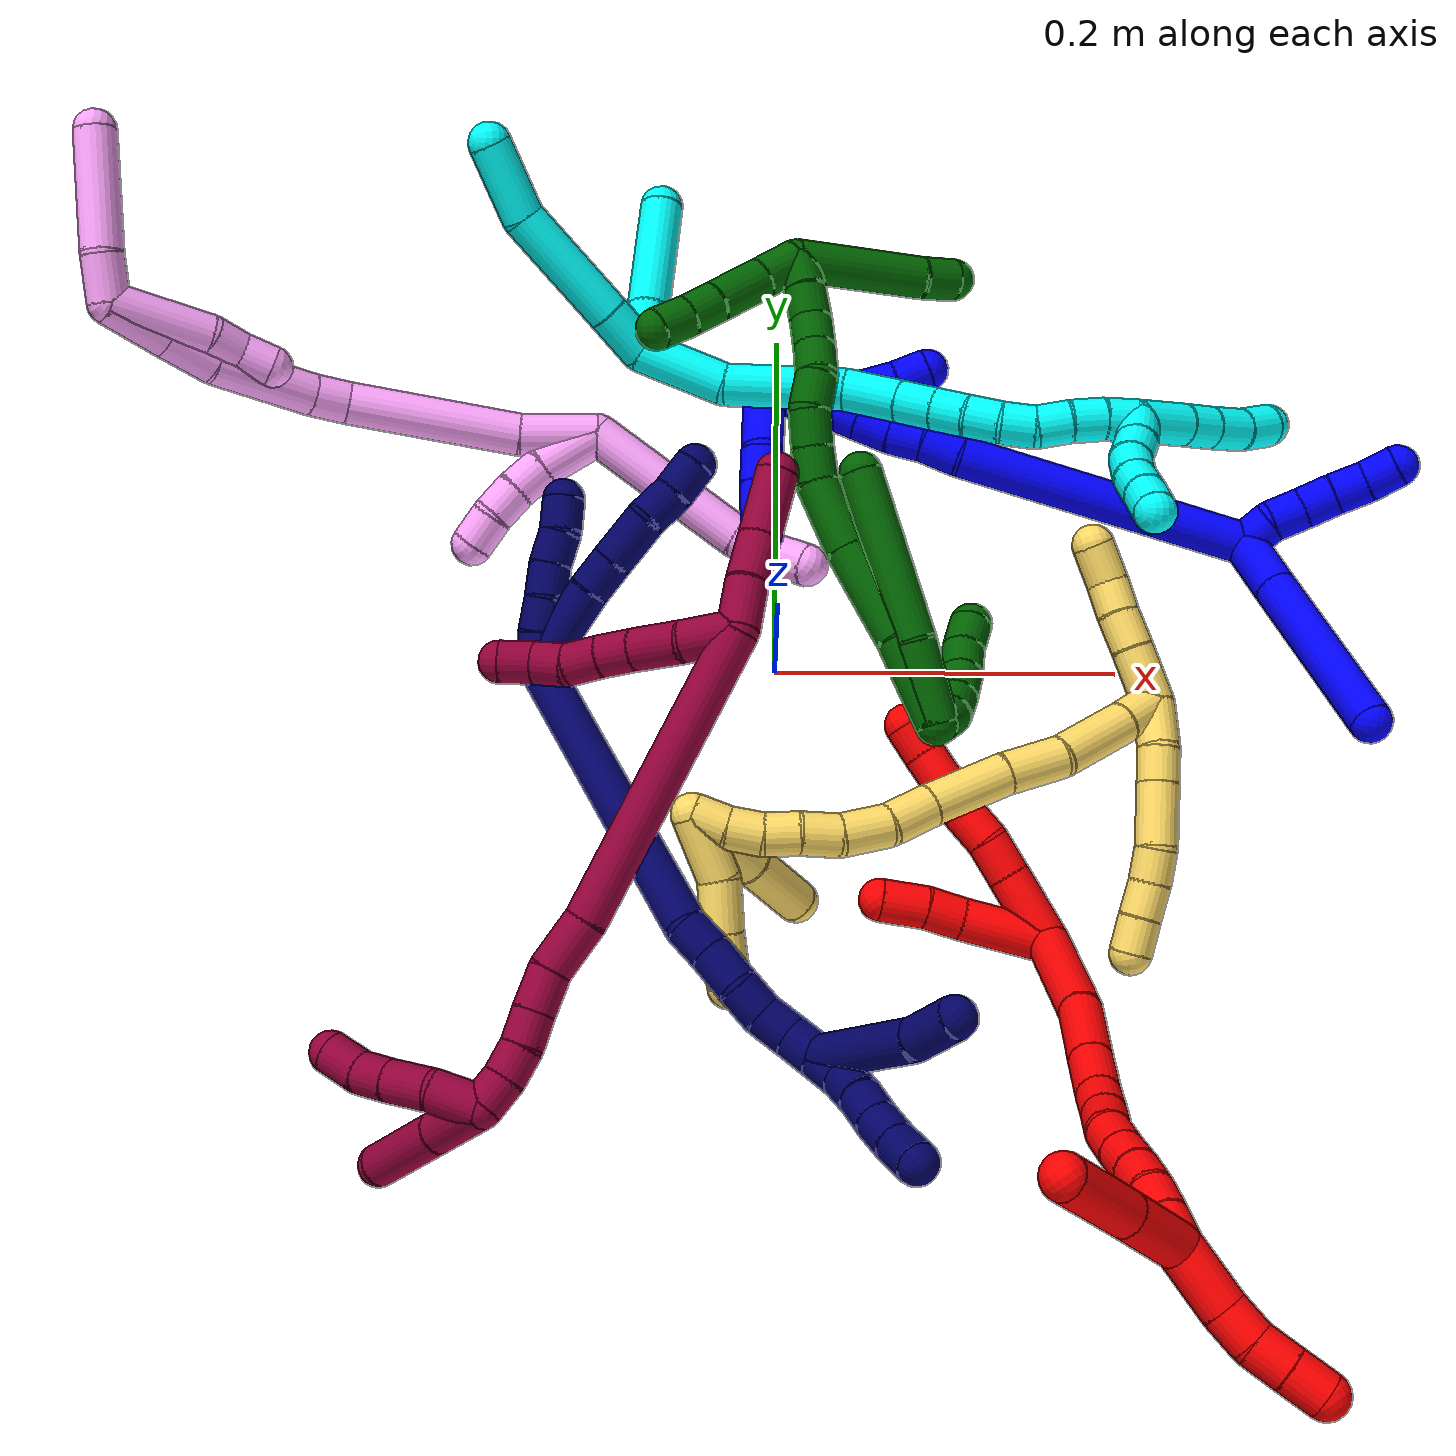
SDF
<sdf version="1.7">
 <world name="default">
  <plugin name="TubeGeneratorPlugin" filename="libtube_generator_plugin.so"/>
  <model name="photoneo_s_sensor">
   <static>1</static>
   <pose>0 0 2 1.57079 1.57079 3.14159</pose>
   <link name="link">
    <inertial><mass>0.1</mass></inertial>
    <sensor name="sensor" type="depth">
     <update_rate>30</update_rate>
     <camera>
      <horizontal_fov>1.22</horizontal_fov>
      <image><width>1920</width><height>1200</height><format>B8G8R8</format></image>
      <clip><near>0.1</near><far>4</far></clip>
      <depth_camera><output>points</output></depth_camera>
     </camera>
     <plugin name="camera_plugin" filename="libgazebo_ros_depth_camera.so">
      <baseline>0.2</baseline>
      <alwaysOn>1</alwaysOn>
      <updateRate>0.0</updateRate>
      <cameraName>camera_ir</cameraName>
      <imageTopicName>/camera/color/image_raw</imageTopicName>
      <cameraInfoTopicName>/camera/color/camera_info</cameraInfoTopicName>
      <depthImageTopicName>/camera/depth/image_raw</depthImageTopicName>
      <depthImageCameraInfoTopicName>/camera/depth/camera_info</depthImageCameraInfoTopicName>
      <pointCloudTopicName>/camera/depth/points</pointCloudTopicName>
      <frameName>fr_optical</frameName>
      <pointCloudCutoff>0.1</pointCloudCutoff>
      <pointCloudCutoffMax>2.0</pointCloudCutoffMax>
      <distortionK1>0</distortionK1>
      <distortionK2>0</distortionK2>
      <distortionK3>0</distortionK3>
      <distortionT1>0</distortionT1>
      <distortionT2>0</distortionT2>
      <CxPrime>0</CxPrime>
      <Cx>0</Cx>
      <Cy>0</Cy>
      <focalLength>0</focalLength>
      <hackBaseline>0</hackBaseline>
     </plugin>
    </sensor>
   </link>
  </model>
  <gravity>0 0 -9.8</gravity>
  <magnetic_field>6e-06 2.3e-05 -4.2e-05</magnetic_field>
  <atmosphere type="adiabatic"/>
  <physics name="default_physics" default="0" type="ode">
   <max_step_size>0.003</max_step_size>
   <real_time_factor>1</real_time_factor>
   <real_time_update_rate>1000</real_time_update_rate>
   <max_contacts>10000</max_contacts>
   <ode>
    <solver>
     <type>quick</type>
     <iters>100</iters>
     <sor>1.3</sor>
     <use_dynamic_moi_rescaling>0</use_dynamic_moi_rescaling>
    </solver>
    <constraints>
     <contact_max_correcting_vel>0</contact_max_correcting_vel>
     <contact_surface_layer>0.001</contact_surface_layer>
     <cfm>0</cfm>
     <erp>0.2</erp>
    </constraints>
   </ode>
  </physics>
  <scene><ambient>0.4 0.4 0.4 1</ambient><background>0.7 0.7 0.7 1</background><shadows>0</shadows></scene>
  <audio><device>default</device></audio>
  <spherical_coordinates>
   <surface_model>EARTH_WGS84</surface_model>
   <latitude_deg>0</latitude_deg>
   <longitude_deg>0</longitude_deg>
   <elevation>0</elevation>
   <heading_deg>0</heading_deg>
  </spherical_coordinates>
  <model name="bin">
   <static>1</static>
   <link name="bottom">
    <collision name="collision-bottom">
     <pose>0 0 -0.01 0 -0 0</pose>
     <geometry><box><size>0.8 0.6 0.02</size></box></geometry>
     <surface>
      <friction><ode><mu>100</mu><mu2>100</mu2></ode></friction>
      <contact><collide_bitmask>65535</collide_bitmask></contact>
     </surface>
    </collision>
   </link>
   <link name="west_wall">
    <collision name="collision-west_wall">
     <pose>-0.41 0 0.1 0 -0 0</pose>
     <geometry><box><size>0.02 0.6 0.2</size></box></geometry>
     <surface>
      <friction><ode><mu>100</mu><mu2>100</mu2></ode></friction>
      <contact><collide_bitmask>65535</collide_bitmask></contact>
     </surface>
    </collision>
   </link>
   <link name="east_wall">
    <collision name="collision-east_wall">
     <pose>0.41 0 0.1 0 -0 0</pose>
     <geometry><box><size>0.02 0.6 0.2</size></box></geometry>
     <surface>
      <friction><ode><mu>100</mu><mu2>100</mu2></ode></friction>
      <contact><collide_bitmask>65535</collide_bitmask></contact>
     </surface>
    </collision>
   </link>
   <link name="south_wall">
    <collision name="collision-south_wall">
     <pose>0 -0.31 0.1 0 -0 0</pose>
     <geometry><box><size>0.8 0.02 0.2</size></box></geometry>
     <surface>
      <friction><ode><mu>100</mu><mu2>100</mu2></ode></friction>
      <contact><collide_bitmask>65535</collide_bitmask></contact>
     </surface>
    </collision>
   </link>
   <link name="north_wall">
    <collision name="collision-north_wall">
     <pose>0 0.31 0.1 0 -0 0</pose>
     <geometry><box><size>0.8 0.02 0.2</size></box></geometry>
     <surface>
      <friction><ode><mu>100</mu><mu2>100</mu2></ode></friction>
      <contact><collide_bitmask>65535</collide_bitmask></contact>
     </surface>
    </collision>
   </link>
  </model>
  <model name="1">
   <static>0</static>
   <link name="1">
    <collision name="collision-cylinder-e_1_2_8">
     <pose>0.004062 -0.015116 0.012046 0.897941 0.207134 0.100069</pose>
     <geometry><cylinder><radius>0.0125</radius><length>0.039502</length></cylinder></geometry>
     <surface>
      <friction><ode><mu>1.16</mu><mu2>1.16</mu2><slip1>0</slip1><slip2>0</slip2></ode></friction>
      <contact><ode><kp>1e+06</kp><kd>1</kd><max_vel>0</max_vel><min_depth>0.001</min_depth></ode></contact>
     </surface>
    </collision>
    <visual name="visual-cylinder-e_1_2_8">
     <pose>0.004062 -0.015116 0.012046 0.897941 0.207134 0.100069</pose>
     <geometry><cylinder><radius>0.0125</radius><length>0.039502</length></cylinder></geometry>
     <material><ambient>0 0 1 1</ambient></material>
    </visual>
    <collision name="collision-cylinder-e_2_8_6">
     <pose>0.019372 -0.072261 0.058144 0.889868 0.205022 0.098024</pose>
     <geometry><cylinder><radius>0.0125</radius><length>0.110498</length></cylinder></geometry>
     <surface>
      <friction><ode><mu>1.16</mu><mu2>1.16</mu2><slip1>0</slip1><slip2>0</slip2></ode></friction>
      <contact><ode><kp>1e+06</kp><kd>1</kd><max_vel>0</max_vel><min_depth>0.001</min_depth></ode></contact>
     </surface>
    </collision>
    <visual name="visual-cylinder-e_2_8_6">
     <pose>0.019372 -0.072261 0.058144 0.889868 0.205022 0.098024</pose>
     <geometry><cylinder><radius>0.0125</radius><length>0.110498</length></cylinder></geometry>
     <material><ambient>0 0 1 1</ambient></material>
    </visual>
    <collision name="collision-cylinder-e_1_2_9">
     <pose>-0.006732 0.003828 0.006326 -0.544188 -0.738523 0.215131</pose>
     <geometry><cylinder><radius>0.0125</radius><length>0.02</length></cylinder></geometry>
     <surface>
      <friction><ode><mu>1.16</mu><mu2>1.16</mu2><slip1>0</slip1><slip2>0</slip2></ode></friction>
      <contact><ode><kp>1e+06</kp><kd>1</kd><max_vel>0</max_vel><min_depth>0.001</min_depth></ode></contact>
     </surface>
    </collision>
    <visual name="visual-cylinder-e_1_2_9">
     <pose>-0.006732 0.003828 0.006326 -0.544188 -0.738523 0.215131</pose>
     <geometry><cylinder><radius>0.0125</radius><length>0.02</length></cylinder></geometry>
     <material><ambient>0 0 1 1</ambient></material>
    </visual>
    <collision name="collision-cylinder-e_2_9_10">
     <pose>-0.017326 0.011966 0.020809 -0.486059 -0.396526 0.099537</pose>
     <geometry><cylinder><radius>0.0125</radius><length>0.02</length></cylinder></geometry>
     <surface>
      <friction><ode><mu>1.16</mu><mu2>1.16</mu2><slip1>0</slip1><slip2>0</slip2></ode></friction>
      <contact><ode><kp>1e+06</kp><kd>1</kd><max_vel>0</max_vel><min_depth>0.001</min_depth></ode></contact>
     </surface>
    </collision>
    <visual name="visual-cylinder-e_2_9_10">
     <pose>-0.017326 0.011966 0.020809 -0.486059 -0.396526 0.099537</pose>
     <geometry><cylinder><radius>0.0125</radius><length>0.02</length></cylinder></geometry>
     <material><ambient>0 0 1 1</ambient></material>
    </visual>
    <collision name="collision-cylinder-e_3_10_11">
     <pose>-0.025909 0.019639 0.037113 -0.391547 -0.491663 0.099434</pose>
     <geometry><cylinder><radius>0.0125</radius><length>0.02</length></cylinder></geometry>
     <surface>
      <friction><ode><mu>1.16</mu><mu2>1.16</mu2><slip1>0</slip1><slip2>0</slip2></ode></friction>
      <contact><ode><kp>1e+06</kp><kd>1</kd><max_vel>0</max_vel><min_depth>0.001</min_depth></ode></contact>
     </surface>
    </collision>
    <visual name="visual-cylinder-e_3_10_11">
     <pose>-0.025909 0.019639 0.037113 -0.391547 -0.491663 0.099434</pose>
     <geometry><cylinder><radius>0.0125</radius><length>0.02</length></cylinder></geometry>
     <material><ambient>0 0 1 1</ambient></material>
    </visual>
    <collision name="collision-cylinder-e_4_11_12">
     <pose>-0.034953 0.026155 0.05371 -0.357114 -0.446992 0.081997</pose>
     <geometry><cylinder><radius>0.0125</radius><length>0.02</length></cylinder></geometry>
     <surface>
      <friction><ode><mu>1.16</mu><mu2>1.16</mu2><slip1>0</slip1><slip2>0</slip2></ode></friction>
      <contact><ode><kp>1e+06</kp><kd>1</kd><max_vel>0</max_vel><min_depth>0.001</min_depth></ode></contact>
     </surface>
    </collision>
    <visual name="visual-cylinder-e_4_11_12">
     <pose>-0.034953 0.026155 0.05371 -0.357114 -0.446992 0.081997</pose>
     <geometry><cylinder><radius>0.0125</radius><length>0.02</length></cylinder></geometry>
     <material><ambient>0 0 1 1</ambient></material>
    </visual>
    <collision name="collision-cylinder-e_5_12_5">
     <pose>-0.044889 0.031907 0.070015 -0.319512 -0.596033 0.098905</pose>
     <geometry><cylinder><radius>0.0125</radius><length>0.02</length></cylinder></geometry>
     <surface>
      <friction><ode><mu>1.16</mu><mu2>1.16</mu2><slip1>0</slip1><slip2>0</slip2></ode></friction>
      <contact><ode><kp>1e+06</kp><kd>1</kd><max_vel>0</max_vel><min_depth>0.001</min_depth></ode></contact>
     </surface>
    </collision>
    <visual name="visual-cylinder-e_5_12_5">
     <pose>-0.044889 0.031907 0.070015 -0.319512 -0.596033 0.098905</pose>
     <geometry><cylinder><radius>0.0125</radius><length>0.02</length></cylinder></geometry>
     <material><ambient>0 0 1 1</ambient></material>
    </visual>
    <collision name="collision-cylinder-e_1_2_13">
     <pose>-0.017983 -0.011684 -0.084995 3.00498 -0.206609 -1.97499</pose>
     <geometry><cylinder><radius>0.0125</radius><length>0.175318</length></cylinder></geometry>
     <surface>
      <friction><ode><mu>1.16</mu><mu2>1.16</mu2><slip1>0</slip1><slip2>0</slip2></ode></friction>
      <contact><ode><kp>1e+06</kp><kd>1</kd><max_vel>0</max_vel><min_depth>0.001</min_depth></ode></contact>
     </surface>
    </collision>
    <visual name="visual-cylinder-e_1_2_13">
     <pose>-0.017983 -0.011684 -0.084995 3.00498 -0.206609 -1.97499</pose>
     <geometry><cylinder><radius>0.0125</radius><length>0.175318</length></cylinder></geometry>
     <material><ambient>0 0 1 1</ambient></material>
    </visual>
    <collision name="collision-cylinder-e_2_13_14">
     <pose>-0.038239 -0.022722 -0.181036 -3.08314 -0.202713 2.58183</pose>
     <geometry><cylinder><radius>0.0125</radius><length>0.022591</length></cylinder></geometry>
     <surface>
      <friction><ode><mu>1.16</mu><mu2>1.16</mu2><slip1>0</slip1><slip2>0</slip2></ode></friction>
      <contact><ode><kp>1e+06</kp><kd>1</kd><max_vel>0</max_vel><min_depth>0.001</min_depth></ode></contact>
     </surface>
    </collision>
    <visual name="visual-cylinder-e_2_13_14">
     <pose>-0.038239 -0.022722 -0.181036 -3.08314 -0.202713 2.58183</pose>
     <geometry><cylinder><radius>0.0125</radius><length>0.022591</length></cylinder></geometry>
     <material><ambient>0 0 1 1</ambient></material>
    </visual>
    <collision name="collision-cylinder-e_3_14_15">
     <pose>-0.040824 -0.021318 -0.202329 -3.06774 -0.030256 0.777372</pose>
     <geometry><cylinder><radius>0.0125</radius><length>0.020561</length></cylinder></geometry>
     <surface>
      <friction><ode><mu>1.16</mu><mu2>1.16</mu2><slip1>0</slip1><slip2>0</slip2></ode></friction>
      <contact><ode><kp>1e+06</kp><kd>1</kd><max_vel>0</max_vel><min_depth>0.001</min_depth></ode></contact>
     </surface>
    </collision>
    <visual name="visual-cylinder-e_3_14_15">
     <pose>-0.040824 -0.021318 -0.202329 -3.06774 -0.030256 0.777372</pose>
     <geometry><cylinder><radius>0.0125</radius><length>0.020561</length></cylinder></geometry>
     <material><ambient>0 0 1 1</ambient></material>
    </visual>
    <collision name="collision-cylinder-e_4_15_16">
     <pose>-0.042674 -0.019084 -0.222745 -2.99746 -0.148683 1.60202</pose>
     <geometry><cylinder><radius>0.0125</radius><length>0.020778</length></cylinder></geometry>
     <surface>
      <friction><ode><mu>1.16</mu><mu2>1.16</mu2><slip1>0</slip1><slip2>0</slip2></ode></friction>
      <contact><ode><kp>1e+06</kp><kd>1</kd><max_vel>0</max_vel><min_depth>0.001</min_depth></ode></contact>
     </surface>
    </collision>
    <visual name="visual-cylinder-e_4_15_16">
     <pose>-0.042674 -0.019084 -0.222745 -2.99746 -0.148683 1.60202</pose>
     <geometry><cylinder><radius>0.0125</radius><length>0.020778</length></cylinder></geometry>
     <material><ambient>0 0 1 1</ambient></material>
    </visual>
    <collision name="collision-cylinder-e_5_16_17">
     <pose>-0.045691 -0.016077 -0.242782 -2.98768 -0.146862 1.52373</pose>
     <geometry><cylinder><radius>0.0125</radius><length>0.020191</length></cylinder></geometry>
     <surface>
      <friction><ode><mu>1.16</mu><mu2>1.16</mu2><slip1>0</slip1><slip2>0</slip2></ode></friction>
      <contact><ode><kp>1e+06</kp><kd>1</kd><max_vel>0</max_vel><min_depth>0.001</min_depth></ode></contact>
     </surface>
    </collision>
    <visual name="visual-cylinder-e_5_16_17">
     <pose>-0.045691 -0.016077 -0.242782 -2.98768 -0.146862 1.52373</pose>
     <geometry><cylinder><radius>0.0125</radius><length>0.020191</length></cylinder></geometry>
     <material><ambient>0 0 1 1</ambient></material>
    </visual>
    <collision name="collision-cylinder-e_6_17_18">
     <pose>-0.048075 -0.014664 -0.262779 3.13 -0.089294 -2.88347</pose>
     <geometry><cylinder><radius>0.0125</radius><length>0.02034</length></cylinder></geometry>
     <surface>
      <friction><ode><mu>1.16</mu><mu2>1.16</mu2><slip1>0</slip1><slip2>0</slip2></ode></friction>
      <contact><ode><kp>1e+06</kp><kd>1</kd><max_vel>0</max_vel><min_depth>0.001</min_depth></ode></contact>
     </surface>
    </collision>
    <visual name="visual-cylinder-e_6_17_18">
     <pose>-0.048075 -0.014664 -0.262779 3.13 -0.089294 -2.88347</pose>
     <geometry><cylinder><radius>0.0125</radius><length>0.02034</length></cylinder></geometry>
     <material><ambient>0 0 1 1</ambient></material>
    </visual>
    <collision name="collision-cylinder-e_7_18_1">
     <pose>-0.050848 -0.014998 -0.282842 3.11975 -0.185663 -2.90803</pose>
     <geometry><cylinder><radius>0.0125</radius><length>0.020221</length></cylinder></geometry>
     <surface>
      <friction><ode><mu>1.16</mu><mu2>1.16</mu2><slip1>0</slip1><slip2>0</slip2></ode></friction>
      <contact><ode><kp>1e+06</kp><kd>1</kd><max_vel>0</max_vel><min_depth>0.001</min_depth></ode></contact>
     </surface>
    </collision>
    <visual name="visual-cylinder-e_7_18_1">
     <pose>-0.050848 -0.014998 -0.282842 3.11975 -0.185663 -2.90803</pose>
     <geometry><cylinder><radius>0.0125</radius><length>0.020221</length></cylinder></geometry>
     <material><ambient>0 0 1 1</ambient></material>
    </visual>
    <collision name="collision-cylinder-e_1_1_19">
     <pose>-0.053929 -0.01596 -0.278202 0.051087 -0.08301 -0.002122</pose>
     <geometry><cylinder><radius>0.0125</radius><length>0.029288</length></cylinder></geometry>
     <surface>
      <friction><ode><mu>1.16</mu><mu2>1.16</mu2><slip1>0</slip1><slip2>0</slip2></ode></friction>
      <contact><ode><kp>1e+06</kp><kd>1</kd><max_vel>0</max_vel><min_depth>0.001</min_depth></ode></contact>
     </surface>
    </collision>
    <visual name="visual-cylinder-e_1_1_19">
     <pose>-0.053929 -0.01596 -0.278202 0.051087 -0.08301 -0.002122</pose>
     <geometry><cylinder><radius>0.0125</radius><length>0.029288</length></cylinder></geometry>
     <material><ambient>0 0 1 1</ambient></material>
    </visual>
    <collision name="collision-cylinder-e_2_19_20">
     <pose>-0.056555 -0.01266 -0.249801 -0.284639 -0.097701 0.01401</pose>
     <geometry><cylinder><radius>0.0125</radius><length>0.028952</length></cylinder></geometry>
     <surface>
      <friction><ode><mu>1.16</mu><mu2>1.16</mu2><slip1>0</slip1><slip2>0</slip2></ode></friction>
      <contact><ode><kp>1e+06</kp><kd>1</kd><max_vel>0</max_vel><min_depth>0.001</min_depth></ode></contact>
     </surface>
    </collision>
    <visual name="visual-cylinder-e_2_19_20">
     <pose>-0.056555 -0.01266 -0.249801 -0.284639 -0.097701 0.01401</pose>
     <geometry><cylinder><radius>0.0125</radius><length>0.028952</length></cylinder></geometry>
     <material><ambient>0 0 1 1</ambient></material>
    </visual>
    <collision name="collision-cylinder-e_3_20_21">
     <pose>-0.060467 -0.003559 -0.226677 -0.498023 -0.231974 0.059237</pose>
     <geometry><cylinder><radius>0.0125</radius><length>0.021746</length></cylinder></geometry>
     <surface>
      <friction><ode><mu>1.16</mu><mu2>1.16</mu2><slip1>0</slip1><slip2>0</slip2></ode></friction>
      <contact><ode><kp>1e+06</kp><kd>1</kd><max_vel>0</max_vel><min_depth>0.001</min_depth></ode></contact>
     </surface>
    </collision>
    <visual name="visual-cylinder-e_3_20_21">
     <pose>-0.060467 -0.003559 -0.226677 -0.498023 -0.231974 0.059237</pose>
     <geometry><cylinder><radius>0.0125</radius><length>0.021746</length></cylinder></geometry>
     <material><ambient>0 0 1 1</ambient></material>
    </visual>
    <collision name="collision-cylinder-e_4_21_4">
     <pose>-0.066321 0.00623 -0.209228 -0.52615 -0.341881 0.092915</pose>
     <geometry><cylinder><radius>0.0125</radius><length>0.020015</length></cylinder></geometry>
     <surface>
      <friction><ode><mu>1.16</mu><mu2>1.16</mu2><slip1>0</slip1><slip2>0</slip2></ode></friction>
      <contact><ode><kp>1e+06</kp><kd>1</kd><max_vel>0</max_vel><min_depth>0.001</min_depth></ode></contact>
     </surface>
    </collision>
    <visual name="visual-cylinder-e_4_21_4">
     <pose>-0.066321 0.00623 -0.209228 -0.52615 -0.341881 0.092915</pose>
     <geometry><cylinder><radius>0.0125</radius><length>0.020015</length></cylinder></geometry>
     <material><ambient>0 0 1 1</ambient></material>
    </visual>
    <collision name="collision-cylinder-e_1_1_22">
     <pose>-0.043586 -0.036542 -0.286826 1.29872 0.39105 0.298489</pose>
     <geometry><cylinder><radius>0.0125</radius><length>0.047898</length></cylinder></geometry>
     <surface>
      <friction><ode><mu>1.16</mu><mu2>1.16</mu2><slip1>0</slip1><slip2>0</slip2></ode></friction>
      <contact><ode><kp>1e+06</kp><kd>1</kd><max_vel>0</max_vel><min_depth>0.001</min_depth></ode></contact>
     </surface>
    </collision>
    <visual name="visual-cylinder-e_1_1_22">
     <pose>-0.043586 -0.036542 -0.286826 1.29872 0.39105 0.298489</pose>
     <geometry><cylinder><radius>0.0125</radius><length>0.047898</length></cylinder></geometry>
     <material><ambient>0 0 1 1</ambient></material>
    </visual>
    <collision name="collision-cylinder-e_2_22_23">
     <pose>-0.027656 -0.065926 -0.278656 1.3019 0.683073 0.528842</pose>
     <geometry><cylinder><radius>0.0125</radius><length>0.021551</length></cylinder></geometry>
     <surface>
      <friction><ode><mu>1.16</mu><mu2>1.16</mu2><slip1>0</slip1><slip2>0</slip2></ode></friction>
      <contact><ode><kp>1e+06</kp><kd>1</kd><max_vel>0</max_vel><min_depth>0.001</min_depth></ode></contact>
     </surface>
    </collision>
    <visual name="visual-cylinder-e_2_22_23">
     <pose>-0.027656 -0.065926 -0.278656 1.3019 0.683073 0.528842</pose>
     <geometry><cylinder><radius>0.0125</radius><length>0.021551</length></cylinder></geometry>
     <material><ambient>0 0 1 1</ambient></material>
    </visual>
    <collision name="collision-cylinder-e_3_23_3">
     <pose>-0.012073 -0.085724 -0.272149 1.22076 0.612501 0.435343</pose>
     <geometry><cylinder><radius>0.0125</radius><length>0.030551</length></cylinder></geometry>
     <surface>
      <friction><ode><mu>1.16</mu><mu2>1.16</mu2><slip1>0</slip1><slip2>0</slip2></ode></friction>
      <contact><ode><kp>1e+06</kp><kd>1</kd><max_vel>0</max_vel><min_depth>0.001</min_depth></ode></contact>
     </surface>
    </collision>
    <visual name="visual-cylinder-e_3_23_3">
     <pose>-0.012073 -0.085724 -0.272149 1.22076 0.612501 0.435343</pose>
     <geometry><cylinder><radius>0.0125</radius><length>0.030551</length></cylinder></geometry>
     <material><ambient>0 0 1 1</ambient></material>
    </visual>
    <collision name="collision-sphere-3">
     <pose>-0.003291 -0.097465 -0.267863 0 -0 0</pose>
     <geometry><sphere><radius>0.0125</radius></sphere></geometry>
     <surface>
      <friction><ode><mu>1.16</mu><mu2>1.16</mu2><slip1>0</slip1><slip2>0</slip2></ode></friction>
      <contact><ode><kp>1e+06</kp><kd>1</kd><max_vel>0</max_vel><min_depth>0.001</min_depth></ode></contact>
     </surface>
    </collision>
    <visual name="visual-sphere-3">
     <pose>-0.003291 -0.097465 -0.267863 0 -0 0</pose>
     <geometry><sphere><radius>0.0125</radius></sphere></geometry>
     <material><ambient>0 0 1 1</ambient></material>
    </visual>
    <collision name="collision-sphere-23">
     <pose>-0.020855 -0.073983 -0.276436 0 -0 0</pose>
     <geometry><sphere><radius>0.0125</radius></sphere></geometry>
     <surface>
      <friction><ode><mu>1.16</mu><mu2>1.16</mu2><slip1>0</slip1><slip2>0</slip2></ode></friction>
      <contact><ode><kp>1e+06</kp><kd>1</kd><max_vel>0</max_vel><min_depth>0.001</min_depth></ode></contact>
     </surface>
    </collision>
    <visual name="visual-sphere-23">
     <pose>-0.020855 -0.073983 -0.276436 0 -0 0</pose>
     <geometry><sphere><radius>0.0125</radius></sphere></geometry>
     <material><ambient>0 0 1 1</ambient></material>
    </visual>
    <collision name="collision-sphere-22">
     <pose>-0.034458 -0.057868 -0.280876 0 -0 0</pose>
     <geometry><sphere><radius>0.0125</radius></sphere></geometry>
     <surface>
      <friction><ode><mu>1.16</mu><mu2>1.16</mu2><slip1>0</slip1><slip2>0</slip2></ode></friction>
      <contact><ode><kp>1e+06</kp><kd>1</kd><max_vel>0</max_vel><min_depth>0.001</min_depth></ode></contact>
     </surface>
    </collision>
    <visual name="visual-sphere-22">
     <pose>-0.034458 -0.057868 -0.280876 0 -0 0</pose>
     <geometry><sphere><radius>0.0125</radius></sphere></geometry>
     <material><ambient>0 0 1 1</ambient></material>
    </visual>
    <collision name="collision-sphere-4">
     <pose>-0.069676 0.010965 -0.201075 0 -0 0</pose>
     <geometry><sphere><radius>0.0125</radius></sphere></geometry>
     <surface>
      <friction><ode><mu>1.16</mu><mu2>1.16</mu2><slip1>0</slip1><slip2>0</slip2></ode></friction>
      <contact><ode><kp>1e+06</kp><kd>1</kd><max_vel>0</max_vel><min_depth>0.001</min_depth></ode></contact>
     </surface>
    </collision>
    <visual name="visual-sphere-4">
     <pose>-0.069676 0.010965 -0.201075 0 -0 0</pose>
     <geometry><sphere><radius>0.0125</radius></sphere></geometry>
     <material><ambient>0 0 1 1</ambient></material>
    </visual>
    <collision name="collision-sphere-21">
     <pose>-0.062966 0.001495 -0.217381 0 -0 0</pose>
     <geometry><sphere><radius>0.0125</radius></sphere></geometry>
     <surface>
      <friction><ode><mu>1.16</mu><mu2>1.16</mu2><slip1>0</slip1><slip2>0</slip2></ode></friction>
      <contact><ode><kp>1e+06</kp><kd>1</kd><max_vel>0</max_vel><min_depth>0.001</min_depth></ode></contact>
     </surface>
    </collision>
    <visual name="visual-sphere-21">
     <pose>-0.062966 0.001495 -0.217381 0 -0 0</pose>
     <geometry><sphere><radius>0.0125</radius></sphere></geometry>
     <material><ambient>0 0 1 1</ambient></material>
    </visual>
    <collision name="collision-sphere-20">
     <pose>-0.057967 -0.008614 -0.235973 0 -0 0</pose>
     <geometry><sphere><radius>0.0125</radius></sphere></geometry>
     <surface>
      <friction><ode><mu>1.16</mu><mu2>1.16</mu2><slip1>0</slip1><slip2>0</slip2></ode></friction>
      <contact><ode><kp>1e+06</kp><kd>1</kd><max_vel>0</max_vel><min_depth>0.001</min_depth></ode></contact>
     </surface>
    </collision>
    <visual name="visual-sphere-20">
     <pose>-0.057967 -0.008614 -0.235973 0 -0 0</pose>
     <geometry><sphere><radius>0.0125</radius></sphere></geometry>
     <material><ambient>0 0 1 1</ambient></material>
    </visual>
    <collision name="collision-sphere-11">
     <pose>-0.03063 0.023003 0.045261 0 -0 0</pose>
     <geometry><sphere><radius>0.0125</radius></sphere></geometry>
     <surface>
      <friction><ode><mu>1.16</mu><mu2>1.16</mu2><slip1>0</slip1><slip2>0</slip2></ode></friction>
      <contact><ode><kp>1e+06</kp><kd>1</kd><max_vel>0</max_vel><min_depth>0.001</min_depth></ode></contact>
     </surface>
    </collision>
    <visual name="visual-sphere-11">
     <pose>-0.03063 0.023003 0.045261 0 -0 0</pose>
     <geometry><sphere><radius>0.0125</radius></sphere></geometry>
     <material><ambient>0 0 1 1</ambient></material>
    </visual>
    <collision name="collision-sphere-10">
     <pose>-0.021188 0.016275 0.028964 0 -0 0</pose>
     <geometry><sphere><radius>0.0125</radius></sphere></geometry>
     <surface>
      <friction><ode><mu>1.16</mu><mu2>1.16</mu2><slip1>0</slip1><slip2>0</slip2></ode></friction>
      <contact><ode><kp>1e+06</kp><kd>1</kd><max_vel>0</max_vel><min_depth>0.001</min_depth></ode></contact>
     </surface>
    </collision>
    <visual name="visual-sphere-10">
     <pose>-0.021188 0.016275 0.028964 0 -0 0</pose>
     <geometry><sphere><radius>0.0125</radius></sphere></geometry>
     <material><ambient>0 0 1 1</ambient></material>
    </visual>
    <collision name="collision-sphere-6">
     <pose>0.03062 -0.11429 0.092196 0 -0 0</pose>
     <geometry><sphere><radius>0.0125</radius></sphere></geometry>
     <surface>
      <friction><ode><mu>1.16</mu><mu2>1.16</mu2><slip1>0</slip1><slip2>0</slip2></ode></friction>
      <contact><ode><kp>1e+06</kp><kd>1</kd><max_vel>0</max_vel><min_depth>0.001</min_depth></ode></contact>
     </surface>
    </collision>
    <visual name="visual-sphere-6">
     <pose>0.03062 -0.11429 0.092196 0 -0 0</pose>
     <geometry><sphere><radius>0.0125</radius></sphere></geometry>
     <material><ambient>0 0 1 1</ambient></material>
    </visual>
    <collision name="collision-sphere-9">
     <pose>-0.013464 0.007657 0.012653 0 -0 0</pose>
     <geometry><sphere><radius>0.0125</radius></sphere></geometry>
     <surface>
      <friction><ode><mu>1.16</mu><mu2>1.16</mu2><slip1>0</slip1><slip2>0</slip2></ode></friction>
      <contact><ode><kp>1e+06</kp><kd>1</kd><max_vel>0</max_vel><min_depth>0.001</min_depth></ode></contact>
     </surface>
    </collision>
    <visual name="visual-sphere-9">
     <pose>-0.013464 0.007657 0.012653 0 -0 0</pose>
     <geometry><sphere><radius>0.0125</radius></sphere></geometry>
     <material><ambient>0 0 1 1</ambient></material>
    </visual>
    <collision name="collision-sphere-2">
     <geometry><sphere><radius>0.0125</radius></sphere></geometry>
     <surface>
      <friction><ode><mu>1.16</mu><mu2>1.16</mu2><slip1>0</slip1><slip2>0</slip2></ode></friction>
      <contact><ode><kp>1e+06</kp><kd>1</kd><max_vel>0</max_vel><min_depth>0.001</min_depth></ode></contact>
     </surface>
    </collision>
    <visual name="visual-sphere-2">
     <geometry><sphere><radius>0.0125</radius></sphere></geometry>
     <material><ambient>0 0 1 1</ambient></material>
    </visual>
    <collision name="collision-sphere-19">
     <pose>-0.055143 -0.016705 -0.263628 0 -0 0</pose>
     <geometry><sphere><radius>0.0125</radius></sphere></geometry>
     <surface>
      <friction><ode><mu>1.16</mu><mu2>1.16</mu2><slip1>0</slip1><slip2>0</slip2></ode></friction>
      <contact><ode><kp>1e+06</kp><kd>1</kd><max_vel>0</max_vel><min_depth>0.001</min_depth></ode></contact>
     </surface>
    </collision>
    <visual name="visual-sphere-19">
     <pose>-0.055143 -0.016705 -0.263628 0 -0 0</pose>
     <geometry><sphere><radius>0.0125</radius></sphere></geometry>
     <material><ambient>0 0 1 1</ambient></material>
    </visual>
    <collision name="collision-sphere-8">
     <pose>0.008124 -0.030232 0.024092 0 -0 0</pose>
     <geometry><sphere><radius>0.0125</radius></sphere></geometry>
     <surface>
      <friction><ode><mu>1.16</mu><mu2>1.16</mu2><slip1>0</slip1><slip2>0</slip2></ode></friction>
      <contact><ode><kp>1e+06</kp><kd>1</kd><max_vel>0</max_vel><min_depth>0.001</min_depth></ode></contact>
     </surface>
    </collision>
    <visual name="visual-sphere-8">
     <pose>0.008124 -0.030232 0.024092 0 -0 0</pose>
     <geometry><sphere><radius>0.0125</radius></sphere></geometry>
     <material><ambient>0 0 1 1</ambient></material>
    </visual>
    <collision name="collision-sphere-12">
     <pose>-0.039275 0.029308 0.062158 0 -0 0</pose>
     <geometry><sphere><radius>0.0125</radius></sphere></geometry>
     <surface>
      <friction><ode><mu>1.16</mu><mu2>1.16</mu2><slip1>0</slip1><slip2>0</slip2></ode></friction>
      <contact><ode><kp>1e+06</kp><kd>1</kd><max_vel>0</max_vel><min_depth>0.001</min_depth></ode></contact>
     </surface>
    </collision>
    <visual name="visual-sphere-12">
     <pose>-0.039275 0.029308 0.062158 0 -0 0</pose>
     <geometry><sphere><radius>0.0125</radius></sphere></geometry>
     <material><ambient>0 0 1 1</ambient></material>
    </visual>
    <collision name="collision-sphere-5">
     <pose>-0.050502 0.034506 0.077872 0 -0 0</pose>
     <geometry><sphere><radius>0.0125</radius></sphere></geometry>
     <surface>
      <friction><ode><mu>1.16</mu><mu2>1.16</mu2><slip1>0</slip1><slip2>0</slip2></ode></friction>
      <contact><ode><kp>1e+06</kp><kd>1</kd><max_vel>0</max_vel><min_depth>0.001</min_depth></ode></contact>
     </surface>
    </collision>
    <visual name="visual-sphere-5">
     <pose>-0.050502 0.034506 0.077872 0 -0 0</pose>
     <geometry><sphere><radius>0.0125</radius></sphere></geometry>
     <material><ambient>0 0 1 1</ambient></material>
    </visual>
    <collision name="collision-sphere-13">
     <pose>-0.035965 -0.023369 -0.169991 0 -0 0</pose>
     <geometry><sphere><radius>0.0125</radius></sphere></geometry>
     <surface>
      <friction><ode><mu>1.16</mu><mu2>1.16</mu2><slip1>0</slip1><slip2>0</slip2></ode></friction>
      <contact><ode><kp>1e+06</kp><kd>1</kd><max_vel>0</max_vel><min_depth>0.001</min_depth></ode></contact>
     </surface>
    </collision>
    <visual name="visual-sphere-13">
     <pose>-0.035965 -0.023369 -0.169991 0 -0 0</pose>
     <geometry><sphere><radius>0.0125</radius></sphere></geometry>
     <material><ambient>0 0 1 1</ambient></material>
    </visual>
    <collision name="collision-sphere-14">
     <pose>-0.040513 -0.022076 -0.192082 0 -0 0</pose>
     <geometry><sphere><radius>0.0125</radius></sphere></geometry>
     <surface>
      <friction><ode><mu>1.16</mu><mu2>1.16</mu2><slip1>0</slip1><slip2>0</slip2></ode></friction>
      <contact><ode><kp>1e+06</kp><kd>1</kd><max_vel>0</max_vel><min_depth>0.001</min_depth></ode></contact>
     </surface>
    </collision>
    <visual name="visual-sphere-14">
     <pose>-0.040513 -0.022076 -0.192082 0 -0 0</pose>
     <geometry><sphere><radius>0.0125</radius></sphere></geometry>
     <material><ambient>0 0 1 1</ambient></material>
    </visual>
    <collision name="collision-sphere-15">
     <pose>-0.041135 -0.02056 -0.212577 0 -0 0</pose>
     <geometry><sphere><radius>0.0125</radius></sphere></geometry>
     <surface>
      <friction><ode><mu>1.16</mu><mu2>1.16</mu2><slip1>0</slip1><slip2>0</slip2></ode></friction>
      <contact><ode><kp>1e+06</kp><kd>1</kd><max_vel>0</max_vel><min_depth>0.001</min_depth></ode></contact>
     </surface>
    </collision>
    <visual name="visual-sphere-15">
     <pose>-0.041135 -0.02056 -0.212577 0 -0 0</pose>
     <geometry><sphere><radius>0.0125</radius></sphere></geometry>
     <material><ambient>0 0 1 1</ambient></material>
    </visual>
    <collision name="collision-sphere-16">
     <pose>-0.044213 -0.017608 -0.232913 0 -0 0</pose>
     <geometry><sphere><radius>0.0125</radius></sphere></geometry>
     <surface>
      <friction><ode><mu>1.16</mu><mu2>1.16</mu2><slip1>0</slip1><slip2>0</slip2></ode></friction>
      <contact><ode><kp>1e+06</kp><kd>1</kd><max_vel>0</max_vel><min_depth>0.001</min_depth></ode></contact>
     </surface>
    </collision>
    <visual name="visual-sphere-16">
     <pose>-0.044213 -0.017608 -0.232913 0 -0 0</pose>
     <geometry><sphere><radius>0.0125</radius></sphere></geometry>
     <material><ambient>0 0 1 1</ambient></material>
    </visual>
    <collision name="collision-sphere-17">
     <pose>-0.047168 -0.014546 -0.252651 0 -0 0</pose>
     <geometry><sphere><radius>0.0125</radius></sphere></geometry>
     <surface>
      <friction><ode><mu>1.16</mu><mu2>1.16</mu2><slip1>0</slip1><slip2>0</slip2></ode></friction>
      <contact><ode><kp>1e+06</kp><kd>1</kd><max_vel>0</max_vel><min_depth>0.001</min_depth></ode></contact>
     </surface>
    </collision>
    <visual name="visual-sphere-17">
     <pose>-0.047168 -0.014546 -0.252651 0 -0 0</pose>
     <geometry><sphere><radius>0.0125</radius></sphere></geometry>
     <material><ambient>0 0 1 1</ambient></material>
    </visual>
    <collision name="collision-sphere-18">
     <pose>-0.048982 -0.014781 -0.272908 0 -0 0</pose>
     <geometry><sphere><radius>0.0125</radius></sphere></geometry>
     <surface>
      <friction><ode><mu>1.16</mu><mu2>1.16</mu2><slip1>0</slip1><slip2>0</slip2></ode></friction>
      <contact><ode><kp>1e+06</kp><kd>1</kd><max_vel>0</max_vel><min_depth>0.001</min_depth></ode></contact>
     </surface>
    </collision>
    <visual name="visual-sphere-18">
     <pose>-0.048982 -0.014781 -0.272908 0 -0 0</pose>
     <geometry><sphere><radius>0.0125</radius></sphere></geometry>
     <material><ambient>0 0 1 1</ambient></material>
    </visual>
    <collision name="collision-sphere-1">
     <pose>-0.052714 -0.015215 -0.292776 0 -0 0</pose>
     <geometry><sphere><radius>0.0125</radius></sphere></geometry>
     <surface>
      <friction><ode><mu>1.16</mu><mu2>1.16</mu2><slip1>0</slip1><slip2>0</slip2></ode></friction>
      <contact><ode><kp>1e+06</kp><kd>1</kd><max_vel>0</max_vel><min_depth>0.001</min_depth></ode></contact>
     </surface>
    </collision>
    <visual name="visual-sphere-1">
     <pose>-0.052714 -0.015215 -0.292776 0 -0 0</pose>
     <geometry><sphere><radius>0.0125</radius></sphere></geometry>
     <material><ambient>0 0 1 1</ambient></material>
    </visual>
    <inertial>
     <pose>-0.023837 -0.023482 -0.114187 0 -0 0</pose>
     <mass>0.75</mass>
     <inertia>
      <ixx>-0.000421</ixx>
      <ixy>0</ixy>
      <ixz>0</ixz>
      <iyy>-0.000105</iyy>
      <iyz>0</iyz>
      <izz>0.00023</izz>
     </inertia>
    </inertial>
   </link>
   <pose>0.275422 0.077309 0.011495 -1.34565 0.764223 -1.63959</pose>
  </model>
  <model name="2">
   <static>0</static>
   <link name="2">
    <collision name="collision-cylinder-e_1_2_8">
     <pose>-0.001752 -0.000531 -0.021845 3.11728 -0.080015 -2.55191</pose>
     <geometry><cylinder><radius>0.0125</radius><length>0.043844</length></cylinder></geometry>
     <surface>
      <friction><ode><mu>1.16</mu><mu2>1.16</mu2><slip1>0</slip1><slip2>0</slip2></ode></friction>
      <contact><ode><kp>1e+06</kp><kd>1</kd><max_vel>0</max_vel><min_depth>0.001</min_depth></ode></contact>
     </surface>
    </collision>
    <visual name="visual-cylinder-e_1_2_8">
     <pose>-0.001752 -0.000531 -0.021845 3.11728 -0.080015 -2.55191</pose>
     <geometry><cylinder><radius>0.0125</radius><length>0.043844</length></cylinder></geometry>
     <material><ambient>1 0 0 1</ambient></material>
    </visual>
    <collision name="collision-cylinder-e_2_8_9">
     <pose>-0.004632 -0.002453 -0.055309 3.02251 -0.096045 -1.35702</pose>
     <geometry><cylinder><radius>0.0125</radius><length>0.023511</length></cylinder></geometry>
     <surface>
      <friction><ode><mu>1.16</mu><mu2>1.16</mu2><slip1>0</slip1><slip2>0</slip2></ode></friction>
      <contact><ode><kp>1e+06</kp><kd>1</kd><max_vel>0</max_vel><min_depth>0.001</min_depth></ode></contact>
     </surface>
    </collision>
    <visual name="visual-cylinder-e_2_8_9">
     <pose>-0.004632 -0.002453 -0.055309 3.02251 -0.096045 -1.35702</pose>
     <geometry><cylinder><radius>0.0125</radius><length>0.023511</length></cylinder></geometry>
     <material><ambient>1 0 0 1</ambient></material>
    </visual>
    <collision name="collision-cylinder-e_3_9_10">
     <pose>-0.004606 -0.004018 -0.078002 3.12574 0.10376 2.83863</pose>
     <geometry><cylinder><radius>0.0125</radius><length>0.022273</length></cylinder></geometry>
     <surface>
      <friction><ode><mu>1.16</mu><mu2>1.16</mu2><slip1>0</slip1><slip2>0</slip2></ode></friction>
      <contact><ode><kp>1e+06</kp><kd>1</kd><max_vel>0</max_vel><min_depth>0.001</min_depth></ode></contact>
     </surface>
    </collision>
    <visual name="visual-cylinder-e_3_9_10">
     <pose>-0.004606 -0.004018 -0.078002 3.12574 0.10376 2.83863</pose>
     <geometry><cylinder><radius>0.0125</radius><length>0.022273</length></cylinder></geometry>
     <material><ambient>1 0 0 1</ambient></material>
    </visual>
    <collision name="collision-cylinder-e_4_10_11">
     <pose>-0.00385 -0.003925 -0.099075 -3.1147 -0.03975 1.9522</pose>
     <geometry><cylinder><radius>0.0125</radius><length>0.020019</length></cylinder></geometry>
     <surface>
      <friction><ode><mu>1.16</mu><mu2>1.16</mu2><slip1>0</slip1><slip2>0</slip2></ode></friction>
      <contact><ode><kp>1e+06</kp><kd>1</kd><max_vel>0</max_vel><min_depth>0.001</min_depth></ode></contact>
     </surface>
    </collision>
    <visual name="visual-cylinder-e_4_10_11">
     <pose>-0.00385 -0.003925 -0.099075 -3.1147 -0.03975 1.9522</pose>
     <geometry><cylinder><radius>0.0125</radius><length>0.020019</length></cylinder></geometry>
     <material><ambient>1 0 0 1</ambient></material>
    </visual>
    <collision name="collision-cylinder-e_5_11_12">
     <pose>-0.004367 -0.0034 -0.119198 -3.11629 -0.011789 0.871964</pose>
     <geometry><cylinder><radius>0.0125</radius><length>0.020258</length></cylinder></geometry>
     <surface>
      <friction><ode><mu>1.16</mu><mu2>1.16</mu2><slip1>0</slip1><slip2>0</slip2></ode></friction>
      <contact><ode><kp>1e+06</kp><kd>1</kd><max_vel>0</max_vel><min_depth>0.001</min_depth></ode></contact>
     </surface>
    </collision>
    <visual name="visual-cylinder-e_5_11_12">
     <pose>-0.004367 -0.0034 -0.119198 -3.11629 -0.011789 0.871964</pose>
     <geometry><cylinder><radius>0.0125</radius><length>0.020258</length></cylinder></geometry>
     <material><ambient>1 0 0 1</ambient></material>
    </visual>
    <collision name="collision-cylinder-e_6_12_6">
     <pose>-0.005084 -0.004161 -0.139302 3.03995 -0.059514 -1.05887</pose>
     <geometry><cylinder><radius>0.0125</radius><length>0.020096</length></cylinder></geometry>
     <surface>
      <friction><ode><mu>1.16</mu><mu2>1.16</mu2><slip1>0</slip1><slip2>0</slip2></ode></friction>
      <contact><ode><kp>1e+06</kp><kd>1</kd><max_vel>0</max_vel><min_depth>0.001</min_depth></ode></contact>
     </surface>
    </collision>
    <visual name="visual-cylinder-e_6_12_6">
     <pose>-0.005084 -0.004161 -0.139302 3.03995 -0.059514 -1.05887</pose>
     <geometry><cylinder><radius>0.0125</radius><length>0.020096</length></cylinder></geometry>
     <material><ambient>1 0 0 1</ambient></material>
    </visual>
    <collision name="collision-cylinder-e_1_2_13">
     <pose>0.015598 -0.006624 -0.019203 2.80944 0.654854 2.22471</pose>
     <geometry><cylinder><radius>0.0125</radius><length>0.051222</length></cylinder></geometry>
     <surface>
      <friction><ode><mu>1.16</mu><mu2>1.16</mu2><slip1>0</slip1><slip2>0</slip2></ode></friction>
      <contact><ode><kp>1e+06</kp><kd>1</kd><max_vel>0</max_vel><min_depth>0.001</min_depth></ode></contact>
     </surface>
    </collision>
    <visual name="visual-cylinder-e_1_2_13">
     <pose>0.015598 -0.006624 -0.019203 2.80944 0.654854 2.22471</pose>
     <geometry><cylinder><radius>0.0125</radius><length>0.051222</length></cylinder></geometry>
     <material><ambient>1 0 0 1</ambient></material>
    </visual>
    <collision name="collision-cylinder-e_2_13_14">
     <pose>0.037052 -0.017273 -0.0467 2.68978 0.565881 1.80376</pose>
     <geometry><cylinder><radius>0.0125</radius><length>0.021843</length></cylinder></geometry>
     <surface>
      <friction><ode><mu>1.16</mu><mu2>1.16</mu2><slip1>0</slip1><slip2>0</slip2></ode></friction>
      <contact><ode><kp>1e+06</kp><kd>1</kd><max_vel>0</max_vel><min_depth>0.001</min_depth></ode></contact>
     </surface>
    </collision>
    <visual name="visual-cylinder-e_2_13_14">
     <pose>0.037052 -0.017273 -0.0467 2.68978 0.565881 1.80376</pose>
     <geometry><cylinder><radius>0.0125</radius><length>0.021843</length></cylinder></geometry>
     <material><ambient>1 0 0 1</ambient></material>
    </visual>
    <collision name="collision-cylinder-e_3_14_5">
     <pose>0.051721 -0.025979 -0.064037 2.66389 0.713355 1.98394</pose>
     <geometry><cylinder><radius>0.0125</radius><length>0.026934</length></cylinder></geometry>
     <surface>
      <friction><ode><mu>1.16</mu><mu2>1.16</mu2><slip1>0</slip1><slip2>0</slip2></ode></friction>
      <contact><ode><kp>1e+06</kp><kd>1</kd><max_vel>0</max_vel><min_depth>0.001</min_depth></ode></contact>
     </surface>
    </collision>
    <visual name="visual-cylinder-e_3_14_5">
     <pose>0.051721 -0.025979 -0.064037 2.66389 0.713355 1.98394</pose>
     <geometry><cylinder><radius>0.0125</radius><length>0.026934</length></cylinder></geometry>
     <material><ambient>1 0 0 1</ambient></material>
    </visual>
    <collision name="collision-cylinder-e_1_2_15">
     <pose>-0.002066 -0.031835 0.022512 0.955293 -0.052932 -0.027403</pose>
     <geometry><cylinder><radius>0.0125</radius><length>0.07809</length></cylinder></geometry>
     <surface>
      <friction><ode><mu>1.16</mu><mu2>1.16</mu2><slip1>0</slip1><slip2>0</slip2></ode></friction>
      <contact><ode><kp>1e+06</kp><kd>1</kd><max_vel>0</max_vel><min_depth>0.001</min_depth></ode></contact>
     </surface>
    </collision>
    <visual name="visual-cylinder-e_1_2_15">
     <pose>-0.002066 -0.031835 0.022512 0.955293 -0.052932 -0.027403</pose>
     <geometry><cylinder><radius>0.0125</radius><length>0.07809</length></cylinder></geometry>
     <material><ambient>1 0 0 1</ambient></material>
    </visual>
    <collision name="collision-cylinder-e_2_15_16">
     <pose>-0.002078 -0.082427 0.058102 0.961909 0.089543 0.046749</pose>
     <geometry><cylinder><radius>0.0125</radius><length>0.045917</length></cylinder></geometry>
     <surface>
      <friction><ode><mu>1.16</mu><mu2>1.16</mu2><slip1>0</slip1><slip2>0</slip2></ode></friction>
      <contact><ode><kp>1e+06</kp><kd>1</kd><max_vel>0</max_vel><min_depth>0.001</min_depth></ode></contact>
     </surface>
    </collision>
    <visual name="visual-cylinder-e_2_15_16">
     <pose>-0.002078 -0.082427 0.058102 0.961909 0.089543 0.046749</pose>
     <geometry><cylinder><radius>0.0125</radius><length>0.045917</length></cylinder></geometry>
     <material><ambient>1 0 0 1</ambient></material>
    </visual>
    <collision name="collision-cylinder-e_3_16_17">
     <pose>0.001174 -0.113667 0.079887 0.961832 0.078673 0.041065</pose>
     <geometry><cylinder><radius>0.0125</radius><length>0.030532</length></cylinder></geometry>
     <surface>
      <friction><ode><mu>1.16</mu><mu2>1.16</mu2><slip1>0</slip1><slip2>0</slip2></ode></friction>
      <contact><ode><kp>1e+06</kp><kd>1</kd><max_vel>0</max_vel><min_depth>0.001</min_depth></ode></contact>
     </surface>
    </collision>
    <visual name="visual-cylinder-e_3_16_17">
     <pose>0.001174 -0.113667 0.079887 0.961832 0.078673 0.041065</pose>
     <geometry><cylinder><radius>0.0125</radius><length>0.030532</length></cylinder></geometry>
     <material><ambient>1 0 0 1</ambient></material>
    </visual>
    <collision name="collision-cylinder-e_4_17_18">
     <pose>0.002384 -0.134896 0.093623 1.04876 0.001001 0.000579</pose>
     <geometry><cylinder><radius>0.0125</radius><length>0.02018</length></cylinder></geometry>
     <surface>
      <friction><ode><mu>1.16</mu><mu2>1.16</mu2><slip1>0</slip1><slip2>0</slip2></ode></friction>
      <contact><ode><kp>1e+06</kp><kd>1</kd><max_vel>0</max_vel><min_depth>0.001</min_depth></ode></contact>
     </surface>
    </collision>
    <visual name="visual-cylinder-e_4_17_18">
     <pose>0.002384 -0.134896 0.093623 1.04876 0.001001 0.000579</pose>
     <geometry><cylinder><radius>0.0125</radius><length>0.02018</length></cylinder></geometry>
     <material><ambient>1 0 0 1</ambient></material>
    </visual>
    <collision name="collision-cylinder-e_5_18_19">
     <pose>0.001974 -0.154645 0.102856 1.20602 -0.035704 -0.024586</pose>
     <geometry><cylinder><radius>0.0125</radius><length>0.02357</length></cylinder></geometry>
     <surface>
      <friction><ode><mu>1.16</mu><mu2>1.16</mu2><slip1>0</slip1><slip2>0</slip2></ode></friction>
      <contact><ode><kp>1e+06</kp><kd>1</kd><max_vel>0</max_vel><min_depth>0.001</min_depth></ode></contact>
     </surface>
    </collision>
    <visual name="visual-cylinder-e_5_18_19">
     <pose>0.001974 -0.154645 0.102856 1.20602 -0.035704 -0.024586</pose>
     <geometry><cylinder><radius>0.0125</radius><length>0.02357</length></cylinder></geometry>
     <material><ambient>1 0 0 1</ambient></material>
    </visual>
    <collision name="collision-cylinder-e_6_19_20">
     <pose>-0.000112 -0.174126 0.113039 0.956473 -0.159098 -0.082599</pose>
     <geometry><cylinder><radius>0.0125</radius><length>0.021018</length></cylinder></geometry>
     <surface>
      <friction><ode><mu>1.16</mu><mu2>1.16</mu2><slip1>0</slip1><slip2>0</slip2></ode></friction>
      <contact><ode><kp>1e+06</kp><kd>1</kd><max_vel>0</max_vel><min_depth>0.001</min_depth></ode></contact>
     </surface>
    </collision>
    <visual name="visual-cylinder-e_6_19_20">
     <pose>-0.000112 -0.174126 0.113039 0.956473 -0.159098 -0.082599</pose>
     <geometry><cylinder><radius>0.0125</radius><length>0.021018</length></cylinder></geometry>
     <material><ambient>1 0 0 1</ambient></material>
    </visual>
    <collision name="collision-cylinder-e_7_20_21">
     <pose>-0.003779 -0.190749 0.124626 0.967796 -0.199766 -0.105246</pose>
     <geometry><cylinder><radius>0.0125</radius><length>0.020175</length></cylinder></geometry>
     <surface>
      <friction><ode><mu>1.16</mu><mu2>1.16</mu2><slip1>0</slip1><slip2>0</slip2></ode></friction>
      <contact><ode><kp>1e+06</kp><kd>1</kd><max_vel>0</max_vel><min_depth>0.001</min_depth></ode></contact>
     </surface>
    </collision>
    <visual name="visual-cylinder-e_7_20_21">
     <pose>-0.003779 -0.190749 0.124626 0.967796 -0.199766 -0.105246</pose>
     <geometry><cylinder><radius>0.0125</radius><length>0.020175</length></cylinder></geometry>
     <material><ambient>1 0 0 1</ambient></material>
    </visual>
    <collision name="collision-cylinder-e_8_21_22">
     <pose>-0.007274 -0.206778 0.136251 0.918954 -0.149455 -0.074054</pose>
     <geometry><cylinder><radius>0.0125</radius><length>0.020062</length></cylinder></geometry>
     <surface>
      <friction><ode><mu>1.16</mu><mu2>1.16</mu2><slip1>0</slip1><slip2>0</slip2></ode></friction>
      <contact><ode><kp>1e+06</kp><kd>1</kd><max_vel>0</max_vel><min_depth>0.001</min_depth></ode></contact>
     </surface>
    </collision>
    <visual name="visual-cylinder-e_8_21_22">
     <pose>-0.007274 -0.206778 0.136251 0.918954 -0.149455 -0.074054</pose>
     <geometry><cylinder><radius>0.0125</radius><length>0.020062</length></cylinder></geometry>
     <material><ambient>1 0 0 1</ambient></material>
    </visual>
    <collision name="collision-cylinder-e_9_22_23">
     <pose>-0.009222 -0.221762 0.149406 0.782645 -0.045072 -0.018599</pose>
     <geometry><cylinder><radius>0.0125</radius><length>0.020154</length></cylinder></geometry>
     <surface>
      <friction><ode><mu>1.16</mu><mu2>1.16</mu2><slip1>0</slip1><slip2>0</slip2></ode></friction>
      <contact><ode><kp>1e+06</kp><kd>1</kd><max_vel>0</max_vel><min_depth>0.001</min_depth></ode></contact>
     </surface>
    </collision>
    <visual name="visual-cylinder-e_9_22_23">
     <pose>-0.009222 -0.221762 0.149406 0.782645 -0.045072 -0.018599</pose>
     <geometry><cylinder><radius>0.0125</radius><length>0.020154</length></cylinder></geometry>
     <material><ambient>1 0 0 1</ambient></material>
    </visual>
    <collision name="collision-cylinder-e_10_23_1">
     <pose>-0.009798 -0.235895 0.163862 0.765702 -0.012098 -0.004872</pose>
     <geometry><cylinder><radius>0.0125</radius><length>0.020302</length></cylinder></geometry>
     <surface>
      <friction><ode><mu>1.16</mu><mu2>1.16</mu2><slip1>0</slip1><slip2>0</slip2></ode></friction>
      <contact><ode><kp>1e+06</kp><kd>1</kd><max_vel>0</max_vel><min_depth>0.001</min_depth></ode></contact>
     </surface>
    </collision>
    <visual name="visual-cylinder-e_10_23_1">
     <pose>-0.009798 -0.235895 0.163862 0.765702 -0.012098 -0.004872</pose>
     <geometry><cylinder><radius>0.0125</radius><length>0.020302</length></cylinder></geometry>
     <material><ambient>1 0 0 1</ambient></material>
    </visual>
    <collision name="collision-cylinder-e_1_1_24">
     <pose>-0.007551 -0.261358 0.156797 2.23345 0.101033 0.206439</pose>
     <geometry><cylinder><radius>0.0125</radius><length>0.046992</length></cylinder></geometry>
     <surface>
      <friction><ode><mu>1.16</mu><mu2>1.16</mu2><slip1>0</slip1><slip2>0</slip2></ode></friction>
      <contact><ode><kp>1e+06</kp><kd>1</kd><max_vel>0</max_vel><min_depth>0.001</min_depth></ode></contact>
     </surface>
    </collision>
    <visual name="visual-cylinder-e_1_1_24">
     <pose>-0.007551 -0.261358 0.156797 2.23345 0.101033 0.206439</pose>
     <geometry><cylinder><radius>0.0125</radius><length>0.046992</length></cylinder></geometry>
     <material><ambient>1 0 0 1</ambient></material>
    </visual>
    <collision name="collision-cylinder-e_2_24_4">
     <pose>-0.002702 -0.301248 0.127062 2.1918 0.093704 0.181884</pose>
     <geometry><cylinder><radius>0.0125</radius><length>0.053008</length></cylinder></geometry>
     <surface>
      <friction><ode><mu>1.16</mu><mu2>1.16</mu2><slip1>0</slip1><slip2>0</slip2></ode></friction>
      <contact><ode><kp>1e+06</kp><kd>1</kd><max_vel>0</max_vel><min_depth>0.001</min_depth></ode></contact>
     </surface>
    </collision>
    <visual name="visual-cylinder-e_2_24_4">
     <pose>-0.002702 -0.301248 0.127062 2.1918 0.093704 0.181884</pose>
     <geometry><cylinder><radius>0.0125</radius><length>0.053008</length></cylinder></geometry>
     <material><ambient>1 0 0 1</ambient></material>
    </visual>
    <collision name="collision-cylinder-e_1_1_25">
     <pose>-0.010038 -0.241999 0.18966 -0.050267 -0.006328 0.000159</pose>
     <geometry><cylinder><radius>0.0125</radius><length>0.037011</length></cylinder></geometry>
     <surface>
      <friction><ode><mu>1.16</mu><mu2>1.16</mu2><slip1>0</slip1><slip2>0</slip2></ode></friction>
      <contact><ode><kp>1e+06</kp><kd>1</kd><max_vel>0</max_vel><min_depth>0.001</min_depth></ode></contact>
     </surface>
    </collision>
    <visual name="visual-cylinder-e_1_1_25">
     <pose>-0.010038 -0.241999 0.18966 -0.050267 -0.006328 0.000159</pose>
     <geometry><cylinder><radius>0.0125</radius><length>0.037011</length></cylinder></geometry>
     <material><ambient>1 0 0 1</ambient></material>
    </visual>
    <collision name="collision-cylinder-e_2_25_26">
     <pose>-0.011488 -0.241533 0.218452 0.044897 -0.1284 -0.002887</pose>
     <geometry><cylinder><radius>0.0125</radius><length>0.020812</length></cylinder></geometry>
     <surface>
      <friction><ode><mu>1.16</mu><mu2>1.16</mu2><slip1>0</slip1><slip2>0</slip2></ode></friction>
      <contact><ode><kp>1e+06</kp><kd>1</kd><max_vel>0</max_vel><min_depth>0.001</min_depth></ode></contact>
     </surface>
    </collision>
    <visual name="visual-cylinder-e_2_25_26">
     <pose>-0.011488 -0.241533 0.218452 0.044897 -0.1284 -0.002887</pose>
     <geometry><cylinder><radius>0.0125</radius><length>0.020812</length></cylinder></geometry>
     <material><ambient>1 0 0 1</ambient></material>
    </visual>
    <collision name="collision-cylinder-e_3_26_27">
     <pose>-0.016297 -0.241609 0.238627 -0.039205 -0.33863 0.006703</pose>
     <geometry><cylinder><radius>0.0125</radius><length>0.020934</length></cylinder></geometry>
     <surface>
      <friction><ode><mu>1.16</mu><mu2>1.16</mu2><slip1>0</slip1><slip2>0</slip2></ode></friction>
      <contact><ode><kp>1e+06</kp><kd>1</kd><max_vel>0</max_vel><min_depth>0.001</min_depth></ode></contact>
     </surface>
    </collision>
    <visual name="visual-cylinder-e_3_26_27">
     <pose>-0.016297 -0.241609 0.238627 -0.039205 -0.33863 0.006703</pose>
     <geometry><cylinder><radius>0.0125</radius><length>0.020934</length></cylinder></geometry>
     <material><ambient>1 0 0 1</ambient></material>
    </visual>
    <collision name="collision-cylinder-e_4_27_3">
     <pose>-0.023259 -0.240358 0.258488 -0.086268 -0.334269 0.014563</pose>
     <geometry><cylinder><radius>0.0125</radius><length>0.021243</length></cylinder></geometry>
     <surface>
      <friction><ode><mu>1.16</mu><mu2>1.16</mu2><slip1>0</slip1><slip2>0</slip2></ode></friction>
      <contact><ode><kp>1e+06</kp><kd>1</kd><max_vel>0</max_vel><min_depth>0.001</min_depth></ode></contact>
     </surface>
    </collision>
    <visual name="visual-cylinder-e_4_27_3">
     <pose>-0.023259 -0.240358 0.258488 -0.086268 -0.334269 0.014563</pose>
     <geometry><cylinder><radius>0.0125</radius><length>0.021243</length></cylinder></geometry>
     <material><ambient>1 0 0 1</ambient></material>
    </visual>
    <collision name="collision-sphere-3">
     <pose>-0.026744 -0.239493 0.268485 0 -0 0</pose>
     <geometry><sphere><radius>0.0125</radius></sphere></geometry>
     <surface>
      <friction><ode><mu>1.16</mu><mu2>1.16</mu2><slip1>0</slip1><slip2>0</slip2></ode></friction>
      <contact><ode><kp>1e+06</kp><kd>1</kd><max_vel>0</max_vel><min_depth>0.001</min_depth></ode></contact>
     </surface>
    </collision>
    <visual name="visual-sphere-3">
     <pose>-0.026744 -0.239493 0.268485 0 -0 0</pose>
     <geometry><sphere><radius>0.0125</radius></sphere></geometry>
     <material><ambient>1 0 0 1</ambient></material>
    </visual>
    <collision name="collision-sphere-27">
     <pose>-0.019775 -0.241222 0.248492 0 -0 0</pose>
     <geometry><sphere><radius>0.0125</radius></sphere></geometry>
     <surface>
      <friction><ode><mu>1.16</mu><mu2>1.16</mu2><slip1>0</slip1><slip2>0</slip2></ode></friction>
      <contact><ode><kp>1e+06</kp><kd>1</kd><max_vel>0</max_vel><min_depth>0.001</min_depth></ode></contact>
     </surface>
    </collision>
    <visual name="visual-sphere-27">
     <pose>-0.019775 -0.241222 0.248492 0 -0 0</pose>
     <geometry><sphere><radius>0.0125</radius></sphere></geometry>
     <material><ambient>1 0 0 1</ambient></material>
    </visual>
    <collision name="collision-sphere-26">
     <pose>-0.01282 -0.241996 0.228762 0 -0 0</pose>
     <geometry><sphere><radius>0.0125</radius></sphere></geometry>
     <surface>
      <friction><ode><mu>1.16</mu><mu2>1.16</mu2><slip1>0</slip1><slip2>0</slip2></ode></friction>
      <contact><ode><kp>1e+06</kp><kd>1</kd><max_vel>0</max_vel><min_depth>0.001</min_depth></ode></contact>
     </surface>
    </collision>
    <visual name="visual-sphere-26">
     <pose>-0.01282 -0.241996 0.228762 0 -0 0</pose>
     <geometry><sphere><radius>0.0125</radius></sphere></geometry>
     <material><ambient>1 0 0 1</ambient></material>
    </visual>
    <collision name="collision-sphere-25">
     <pose>-0.010155 -0.24107 0.208142 0 -0 0</pose>
     <geometry><sphere><radius>0.0125</radius></sphere></geometry>
     <surface>
      <friction><ode><mu>1.16</mu><mu2>1.16</mu2><slip1>0</slip1><slip2>0</slip2></ode></friction>
      <contact><ode><kp>1e+06</kp><kd>1</kd><max_vel>0</max_vel><min_depth>0.001</min_depth></ode></contact>
     </surface>
    </collision>
    <visual name="visual-sphere-25">
     <pose>-0.010155 -0.24107 0.208142 0 -0 0</pose>
     <geometry><sphere><radius>0.0125</radius></sphere></geometry>
     <material><ambient>1 0 0 1</ambient></material>
    </visual>
    <collision name="collision-sphere-4">
     <pose>-0.000222 -0.322709 0.111709 0 -0 0</pose>
     <geometry><sphere><radius>0.0125</radius></sphere></geometry>
     <surface>
      <friction><ode><mu>1.16</mu><mu2>1.16</mu2><slip1>0</slip1><slip2>0</slip2></ode></friction>
      <contact><ode><kp>1e+06</kp><kd>1</kd><max_vel>0</max_vel><min_depth>0.001</min_depth></ode></contact>
     </surface>
    </collision>
    <visual name="visual-sphere-4">
     <pose>-0.000222 -0.322709 0.111709 0 -0 0</pose>
     <geometry><sphere><radius>0.0125</radius></sphere></geometry>
     <material><ambient>1 0 0 1</ambient></material>
    </visual>
    <collision name="collision-sphere-24">
     <pose>-0.005182 -0.279787 0.142416 0 -0 0</pose>
     <geometry><sphere><radius>0.0125</radius></sphere></geometry>
     <surface>
      <friction><ode><mu>1.16</mu><mu2>1.16</mu2><slip1>0</slip1><slip2>0</slip2></ode></friction>
      <contact><ode><kp>1e+06</kp><kd>1</kd><max_vel>0</max_vel><min_depth>0.001</min_depth></ode></contact>
     </surface>
    </collision>
    <visual name="visual-sphere-24">
     <pose>-0.005182 -0.279787 0.142416 0 -0 0</pose>
     <geometry><sphere><radius>0.0125</radius></sphere></geometry>
     <material><ambient>1 0 0 1</ambient></material>
    </visual>
    <collision name="collision-sphere-1">
     <pose>-0.009921 -0.242929 0.171179 0 -0 0</pose>
     <geometry><sphere><radius>0.0125</radius></sphere></geometry>
     <surface>
      <friction><ode><mu>1.16</mu><mu2>1.16</mu2><slip1>0</slip1><slip2>0</slip2></ode></friction>
      <contact><ode><kp>1e+06</kp><kd>1</kd><max_vel>0</max_vel><min_depth>0.001</min_depth></ode></contact>
     </surface>
    </collision>
    <visual name="visual-sphere-1">
     <pose>-0.009921 -0.242929 0.171179 0 -0 0</pose>
     <geometry><sphere><radius>0.0125</radius></sphere></geometry>
     <material><ambient>1 0 0 1</ambient></material>
    </visual>
    <collision name="collision-sphere-23">
     <pose>-0.009676 -0.22886 0.156544 0 -0 0</pose>
     <geometry><sphere><radius>0.0125</radius></sphere></geometry>
     <surface>
      <friction><ode><mu>1.16</mu><mu2>1.16</mu2><slip1>0</slip1><slip2>0</slip2></ode></friction>
      <contact><ode><kp>1e+06</kp><kd>1</kd><max_vel>0</max_vel><min_depth>0.001</min_depth></ode></contact>
     </surface>
    </collision>
    <visual name="visual-sphere-23">
     <pose>-0.009676 -0.22886 0.156544 0 -0 0</pose>
     <geometry><sphere><radius>0.0125</radius></sphere></geometry>
     <material><ambient>1 0 0 1</ambient></material>
    </visual>
    <collision name="collision-sphere-22">
     <pose>-0.008768 -0.214663 0.142269 0 -0 0</pose>
     <geometry><sphere><radius>0.0125</radius></sphere></geometry>
     <surface>
      <friction><ode><mu>1.16</mu><mu2>1.16</mu2><slip1>0</slip1><slip2>0</slip2></ode></friction>
      <contact><ode><kp>1e+06</kp><kd>1</kd><max_vel>0</max_vel><min_depth>0.001</min_depth></ode></contact>
     </surface>
    </collision>
    <visual name="visual-sphere-22">
     <pose>-0.008768 -0.214663 0.142269 0 -0 0</pose>
     <geometry><sphere><radius>0.0125</radius></sphere></geometry>
     <material><ambient>1 0 0 1</ambient></material>
    </visual>
    <collision name="collision-sphere-21">
     <pose>-0.00578 -0.198892 0.130234 0 -0 0</pose>
     <geometry><sphere><radius>0.0125</radius></sphere></geometry>
     <surface>
      <friction><ode><mu>1.16</mu><mu2>1.16</mu2><slip1>0</slip1><slip2>0</slip2></ode></friction>
      <contact><ode><kp>1e+06</kp><kd>1</kd><max_vel>0</max_vel><min_depth>0.001</min_depth></ode></contact>
     </surface>
    </collision>
    <visual name="visual-sphere-21">
     <pose>-0.00578 -0.198892 0.130234 0 -0 0</pose>
     <geometry><sphere><radius>0.0125</radius></sphere></geometry>
     <material><ambient>1 0 0 1</ambient></material>
    </visual>
    <collision name="collision-sphere-12">
     <pose>-0.004487 -0.003144 -0.129323 0 -0 0</pose>
     <geometry><sphere><radius>0.0125</radius></sphere></geometry>
     <surface>
      <friction><ode><mu>1.16</mu><mu2>1.16</mu2><slip1>0</slip1><slip2>0</slip2></ode></friction>
      <contact><ode><kp>1e+06</kp><kd>1</kd><max_vel>0</max_vel><min_depth>0.001</min_depth></ode></contact>
     </surface>
    </collision>
    <visual name="visual-sphere-12">
     <pose>-0.004487 -0.003144 -0.129323 0 -0 0</pose>
     <geometry><sphere><radius>0.0125</radius></sphere></geometry>
     <material><ambient>1 0 0 1</ambient></material>
    </visual>
    <collision name="collision-sphere-11">
     <pose>-0.004248 -0.003656 -0.109073 0 -0 0</pose>
     <geometry><sphere><radius>0.0125</radius></sphere></geometry>
     <surface>
      <friction><ode><mu>1.16</mu><mu2>1.16</mu2><slip1>0</slip1><slip2>0</slip2></ode></friction>
      <contact><ode><kp>1e+06</kp><kd>1</kd><max_vel>0</max_vel><min_depth>0.001</min_depth></ode></contact>
     </surface>
    </collision>
    <visual name="visual-sphere-11">
     <pose>-0.004248 -0.003656 -0.109073 0 -0 0</pose>
     <geometry><sphere><radius>0.0125</radius></sphere></geometry>
     <material><ambient>1 0 0 1</ambient></material>
    </visual>
    <collision name="collision-sphere-10">
     <pose>-0.003452 -0.004194 -0.089077 0 -0 0</pose>
     <geometry><sphere><radius>0.0125</radius></sphere></geometry>
     <surface>
      <friction><ode><mu>1.16</mu><mu2>1.16</mu2><slip1>0</slip1><slip2>0</slip2></ode></friction>
      <contact><ode><kp>1e+06</kp><kd>1</kd><max_vel>0</max_vel><min_depth>0.001</min_depth></ode></contact>
     </surface>
    </collision>
    <visual name="visual-sphere-10">
     <pose>-0.003452 -0.004194 -0.089077 0 -0 0</pose>
     <geometry><sphere><radius>0.0125</radius></sphere></geometry>
     <material><ambient>1 0 0 1</ambient></material>
    </visual>
    <collision name="collision-sphere-9">
     <pose>-0.005759 -0.003843 -0.066927 0 -0 0</pose>
     <geometry><sphere><radius>0.0125</radius></sphere></geometry>
     <surface>
      <friction><ode><mu>1.16</mu><mu2>1.16</mu2><slip1>0</slip1><slip2>0</slip2></ode></friction>
      <contact><ode><kp>1e+06</kp><kd>1</kd><max_vel>0</max_vel><min_depth>0.001</min_depth></ode></contact>
     </surface>
    </collision>
    <visual name="visual-sphere-9">
     <pose>-0.005759 -0.003843 -0.066927 0 -0 0</pose>
     <geometry><sphere><radius>0.0125</radius></sphere></geometry>
     <material><ambient>1 0 0 1</ambient></material>
    </visual>
    <collision name="collision-sphere-2">
     <geometry><sphere><radius>0.0125</radius></sphere></geometry>
     <surface>
      <friction><ode><mu>1.16</mu><mu2>1.16</mu2><slip1>0</slip1><slip2>0</slip2></ode></friction>
      <contact><ode><kp>1e+06</kp><kd>1</kd><max_vel>0</max_vel><min_depth>0.001</min_depth></ode></contact>
     </surface>
    </collision>
    <visual name="visual-sphere-2">
     <geometry><sphere><radius>0.0125</radius></sphere></geometry>
     <material><ambient>1 0 0 1</ambient></material>
    </visual>
    <collision name="collision-sphere-19">
     <pose>0.001553 -0.165647 0.107058 0 -0 0</pose>
     <geometry><sphere><radius>0.0125</radius></sphere></geometry>
     <surface>
      <friction><ode><mu>1.16</mu><mu2>1.16</mu2><slip1>0</slip1><slip2>0</slip2></ode></friction>
      <contact><ode><kp>1e+06</kp><kd>1</kd><max_vel>0</max_vel><min_depth>0.001</min_depth></ode></contact>
     </surface>
    </collision>
    <visual name="visual-sphere-19">
     <pose>0.001553 -0.165647 0.107058 0 -0 0</pose>
     <geometry><sphere><radius>0.0125</radius></sphere></geometry>
     <material><ambient>1 0 0 1</ambient></material>
    </visual>
    <collision name="collision-sphere-8">
     <pose>-0.003504 -0.001062 -0.043691 0 -0 0</pose>
     <geometry><sphere><radius>0.0125</radius></sphere></geometry>
     <surface>
      <friction><ode><mu>1.16</mu><mu2>1.16</mu2><slip1>0</slip1><slip2>0</slip2></ode></friction>
      <contact><ode><kp>1e+06</kp><kd>1</kd><max_vel>0</max_vel><min_depth>0.001</min_depth></ode></contact>
     </surface>
    </collision>
    <visual name="visual-sphere-8">
     <pose>-0.003504 -0.001062 -0.043691 0 -0 0</pose>
     <geometry><sphere><radius>0.0125</radius></sphere></geometry>
     <material><ambient>1 0 0 1</ambient></material>
    </visual>
    <collision name="collision-sphere-6">
     <pose>-0.005682 -0.005179 -0.14928 0 -0 0</pose>
     <geometry><sphere><radius>0.0125</radius></sphere></geometry>
     <surface>
      <friction><ode><mu>1.16</mu><mu2>1.16</mu2><slip1>0</slip1><slip2>0</slip2></ode></friction>
      <contact><ode><kp>1e+06</kp><kd>1</kd><max_vel>0</max_vel><min_depth>0.001</min_depth></ode></contact>
     </surface>
    </collision>
    <visual name="visual-sphere-6">
     <pose>-0.005682 -0.005179 -0.14928 0 -0 0</pose>
     <geometry><sphere><radius>0.0125</radius></sphere></geometry>
     <material><ambient>1 0 0 1</ambient></material>
    </visual>
    <collision name="collision-sphere-13">
     <pose>0.031197 -0.013248 -0.038406 0 -0 0</pose>
     <geometry><sphere><radius>0.0125</radius></sphere></geometry>
     <surface>
      <friction><ode><mu>1.16</mu><mu2>1.16</mu2><slip1>0</slip1><slip2>0</slip2></ode></friction>
      <contact><ode><kp>1e+06</kp><kd>1</kd><max_vel>0</max_vel><min_depth>0.001</min_depth></ode></contact>
     </surface>
    </collision>
    <visual name="visual-sphere-13">
     <pose>0.031197 -0.013248 -0.038406 0 -0 0</pose>
     <geometry><sphere><radius>0.0125</radius></sphere></geometry>
     <material><ambient>1 0 0 1</ambient></material>
    </visual>
    <collision name="collision-sphere-14">
     <pose>0.042908 -0.021298 -0.054994 0 -0 0</pose>
     <geometry><sphere><radius>0.0125</radius></sphere></geometry>
     <surface>
      <friction><ode><mu>1.16</mu><mu2>1.16</mu2><slip1>0</slip1><slip2>0</slip2></ode></friction>
      <contact><ode><kp>1e+06</kp><kd>1</kd><max_vel>0</max_vel><min_depth>0.001</min_depth></ode></contact>
     </surface>
    </collision>
    <visual name="visual-sphere-14">
     <pose>0.042908 -0.021298 -0.054994 0 -0 0</pose>
     <geometry><sphere><radius>0.0125</radius></sphere></geometry>
     <material><ambient>1 0 0 1</ambient></material>
    </visual>
    <collision name="collision-sphere-5">
     <pose>0.060533 -0.030661 -0.073081 0 -0 0</pose>
     <geometry><sphere><radius>0.0125</radius></sphere></geometry>
     <surface>
      <friction><ode><mu>1.16</mu><mu2>1.16</mu2><slip1>0</slip1><slip2>0</slip2></ode></friction>
      <contact><ode><kp>1e+06</kp><kd>1</kd><max_vel>0</max_vel><min_depth>0.001</min_depth></ode></contact>
     </surface>
    </collision>
    <visual name="visual-sphere-5">
     <pose>0.060533 -0.030661 -0.073081 0 -0 0</pose>
     <geometry><sphere><radius>0.0125</radius></sphere></geometry>
     <material><ambient>1 0 0 1</ambient></material>
    </visual>
    <collision name="collision-sphere-15">
     <pose>-0.004132 -0.06367 0.045023 0 -0 0</pose>
     <geometry><sphere><radius>0.0125</radius></sphere></geometry>
     <surface>
      <friction><ode><mu>1.16</mu><mu2>1.16</mu2><slip1>0</slip1><slip2>0</slip2></ode></friction>
      <contact><ode><kp>1e+06</kp><kd>1</kd><max_vel>0</max_vel><min_depth>0.001</min_depth></ode></contact>
     </surface>
    </collision>
    <visual name="visual-sphere-15">
     <pose>-0.004132 -0.06367 0.045023 0 -0 0</pose>
     <geometry><sphere><radius>0.0125</radius></sphere></geometry>
     <material><ambient>1 0 0 1</ambient></material>
    </visual>
    <collision name="collision-sphere-16">
     <pose>-2.5e-05 -0.101184 0.071181 0 -0 0</pose>
     <geometry><sphere><radius>0.0125</radius></sphere></geometry>
     <surface>
      <friction><ode><mu>1.16</mu><mu2>1.16</mu2><slip1>0</slip1><slip2>0</slip2></ode></friction>
      <contact><ode><kp>1e+06</kp><kd>1</kd><max_vel>0</max_vel><min_depth>0.001</min_depth></ode></contact>
     </surface>
    </collision>
    <visual name="visual-sphere-16">
     <pose>-2.5e-05 -0.101184 0.071181 0 -0 0</pose>
     <geometry><sphere><radius>0.0125</radius></sphere></geometry>
     <material><ambient>1 0 0 1</ambient></material>
    </visual>
    <collision name="collision-sphere-17">
     <pose>0.002374 -0.126151 0.088592 0 -0 0</pose>
     <geometry><sphere><radius>0.0125</radius></sphere></geometry>
     <surface>
      <friction><ode><mu>1.16</mu><mu2>1.16</mu2><slip1>0</slip1><slip2>0</slip2></ode></friction>
      <contact><ode><kp>1e+06</kp><kd>1</kd><max_vel>0</max_vel><min_depth>0.001</min_depth></ode></contact>
     </surface>
    </collision>
    <visual name="visual-sphere-17">
     <pose>0.002374 -0.126151 0.088592 0 -0 0</pose>
     <geometry><sphere><radius>0.0125</radius></sphere></geometry>
     <material><ambient>1 0 0 1</ambient></material>
    </visual>
    <collision name="collision-sphere-18">
     <pose>0.002394 -0.143642 0.098655 0 -0 0</pose>
     <geometry><sphere><radius>0.0125</radius></sphere></geometry>
     <surface>
      <friction><ode><mu>1.16</mu><mu2>1.16</mu2><slip1>0</slip1><slip2>0</slip2></ode></friction>
      <contact><ode><kp>1e+06</kp><kd>1</kd><max_vel>0</max_vel><min_depth>0.001</min_depth></ode></contact>
     </surface>
    </collision>
    <visual name="visual-sphere-18">
     <pose>0.002394 -0.143642 0.098655 0 -0 0</pose>
     <geometry><sphere><radius>0.0125</radius></sphere></geometry>
     <material><ambient>1 0 0 1</ambient></material>
    </visual>
    <collision name="collision-sphere-20">
     <pose>-0.001777 -0.182605 0.119019 0 -0 0</pose>
     <geometry><sphere><radius>0.0125</radius></sphere></geometry>
     <surface>
      <friction><ode><mu>1.16</mu><mu2>1.16</mu2><slip1>0</slip1><slip2>0</slip2></ode></friction>
      <contact><ode><kp>1e+06</kp><kd>1</kd><max_vel>0</max_vel><min_depth>0.001</min_depth></ode></contact>
     </surface>
    </collision>
    <visual name="visual-sphere-20">
     <pose>-0.001777 -0.182605 0.119019 0 -0 0</pose>
     <geometry><sphere><radius>0.0125</radius></sphere></geometry>
     <material><ambient>1 0 0 1</ambient></material>
    </visual>
    <inertial>
     <pose>-0.000312 -0.121652 0.061833 0 -0 0</pose>
     <mass>0.75</mass>
     <inertia><ixx>0.0001</ixx><ixy>0</ixy><ixz>0</ixz><iyy>3.7e-05</iyy><iyz>0</iyz><izz>7e-05</izz></inertia>
    </inertial>
   </link>
   <pose>0.157786 -0.158187 0.012465 -1.53556 0.308871 -2.52679</pose>
  </model>
  <model name="3">
   <static>0</static>
   <link name="3">
    <collision name="collision-cylinder-e_1_2_8">
     <pose>-0.000306 0.010463 0.01094 -0.763092 -0.020201 0.008105</pose>
     <geometry><cylinder><radius>0.0125</radius><length>0.030281</length></cylinder></geometry>
     <surface>
      <friction><ode><mu>1.16</mu><mu2>1.16</mu2><slip1>0</slip1><slip2>0</slip2></ode></friction>
      <contact><ode><kp>1e+06</kp><kd>1</kd><max_vel>0</max_vel><min_depth>0.001</min_depth></ode></contact>
     </surface>
    </collision>
    <visual name="visual-cylinder-e_1_2_8">
     <pose>-0.000306 0.010463 0.01094 -0.763092 -0.020201 0.008105</pose>
     <geometry><cylinder><radius>0.0125</radius><length>0.030281</length></cylinder></geometry>
     <material><ambient>0.003922 1 0.996078 1</ambient></material>
    </visual>
    <collision name="collision-cylinder-e_2_8_9">
     <pose>-0.003586 0.046892 0.047729 -0.787672 -0.081 0.033675</pose>
     <geometry><cylinder><radius>0.0125</radius><length>0.07352</length></cylinder></geometry>
     <surface>
      <friction><ode><mu>1.16</mu><mu2>1.16</mu2><slip1>0</slip1><slip2>0</slip2></ode></friction>
      <contact><ode><kp>1e+06</kp><kd>1</kd><max_vel>0</max_vel><min_depth>0.001</min_depth></ode></contact>
     </surface>
    </collision>
    <visual name="visual-cylinder-e_2_8_9">
     <pose>-0.003586 0.046892 0.047729 -0.787672 -0.081 0.033675</pose>
     <geometry><cylinder><radius>0.0125</radius><length>0.07352</length></cylinder></geometry>
     <material><ambient>0.003922 1 0.996078 1</ambient></material>
    </visual>
    <collision name="collision-cylinder-e_3_9_6">
     <pose>-0.0041 0.092621 0.085282 -1.03608 0.106693 -0.06085</pose>
     <geometry><cylinder><radius>0.0125</radius><length>0.046199</length></cylinder></geometry>
     <surface>
      <friction><ode><mu>1.16</mu><mu2>1.16</mu2><slip1>0</slip1><slip2>0</slip2></ode></friction>
      <contact><ode><kp>1e+06</kp><kd>1</kd><max_vel>0</max_vel><min_depth>0.001</min_depth></ode></contact>
     </surface>
    </collision>
    <visual name="visual-cylinder-e_3_9_6">
     <pose>-0.0041 0.092621 0.085282 -1.03608 0.106693 -0.06085</pose>
     <geometry><cylinder><radius>0.0125</radius><length>0.046199</length></cylinder></geometry>
     <material><ambient>0.003922 1 0.996078 1</ambient></material>
    </visual>
    <collision name="collision-cylinder-e_1_2_10">
     <pose>-0.004133 0.013507 -0.00496 -1.9227 -0.279704 0.397964</pose>
     <geometry><cylinder><radius>0.0125</radius><length>0.029941</length></cylinder></geometry>
     <surface>
      <friction><ode><mu>1.16</mu><mu2>1.16</mu2><slip1>0</slip1><slip2>0</slip2></ode></friction>
      <contact><ode><kp>1e+06</kp><kd>1</kd><max_vel>0</max_vel><min_depth>0.001</min_depth></ode></contact>
     </surface>
    </collision>
    <visual name="visual-cylinder-e_1_2_10">
     <pose>-0.004133 0.013507 -0.00496 -1.9227 -0.279704 0.397964</pose>
     <geometry><cylinder><radius>0.0125</radius><length>0.029941</length></cylinder></geometry>
     <material><ambient>0.003922 1 0.996078 1</ambient></material>
    </visual>
    <collision name="collision-cylinder-e_2_10_5">
     <pose>-0.015562 0.059897 -0.019538 -1.85537 -0.209831 0.279205</pose>
     <geometry><cylinder><radius>0.0125</radius><length>0.070059</length></cylinder></geometry>
     <surface>
      <friction><ode><mu>1.16</mu><mu2>1.16</mu2><slip1>0</slip1><slip2>0</slip2></ode></friction>
      <contact><ode><kp>1e+06</kp><kd>1</kd><max_vel>0</max_vel><min_depth>0.001</min_depth></ode></contact>
     </surface>
    </collision>
    <visual name="visual-cylinder-e_2_10_5">
     <pose>-0.015562 0.059897 -0.019538 -1.85537 -0.209831 0.279205</pose>
     <geometry><cylinder><radius>0.0125</radius><length>0.070059</length></cylinder></geometry>
     <material><ambient>0.003922 1 0.996078 1</ambient></material>
    </visual>
    <collision name="collision-cylinder-e_1_2_11">
     <pose>0.014849 -0.010742 -0.019205 2.63161 0.593587 1.72989</pose>
     <geometry><cylinder><radius>0.0125</radius><length>0.053093</length></cylinder></geometry>
     <surface>
      <friction><ode><mu>1.16</mu><mu2>1.16</mu2><slip1>0</slip1><slip2>0</slip2></ode></friction>
      <contact><ode><kp>1e+06</kp><kd>1</kd><max_vel>0</max_vel><min_depth>0.001</min_depth></ode></contact>
     </surface>
    </collision>
    <visual name="visual-cylinder-e_1_2_11">
     <pose>0.014849 -0.010742 -0.019205 2.63161 0.593587 1.72989</pose>
     <geometry><cylinder><radius>0.0125</radius><length>0.053093</length></cylinder></geometry>
     <material><ambient>0.003922 1 0.996078 1</ambient></material>
    </visual>
    <collision name="collision-cylinder-e_2_11_12">
     <pose>0.049947 -0.023972 -0.067248 3.05555 0.61047 2.87002</pose>
     <geometry><cylinder><radius>0.0125</radius><length>0.07065</length></cylinder></geometry>
     <surface>
      <friction><ode><mu>1.16</mu><mu2>1.16</mu2><slip1>0</slip1><slip2>0</slip2></ode></friction>
      <contact><ode><kp>1e+06</kp><kd>1</kd><max_vel>0</max_vel><min_depth>0.001</min_depth></ode></contact>
     </surface>
    </collision>
    <visual name="visual-cylinder-e_2_11_12">
     <pose>0.049947 -0.023972 -0.067248 3.05555 0.61047 2.87002</pose>
     <geometry><cylinder><radius>0.0125</radius><length>0.07065</length></cylinder></geometry>
     <material><ambient>0.003922 1 0.996078 1</ambient></material>
    </visual>
    <collision name="collision-cylinder-e_3_12_13">
     <pose>0.083012 -0.031005 -0.106247 2.72093 0.855569 2.26576</pose>
     <geometry><cylinder><radius>0.0125</radius><length>0.033947</length></cylinder></geometry>
     <surface>
      <friction><ode><mu>1.16</mu><mu2>1.16</mu2><slip1>0</slip1><slip2>0</slip2></ode></friction>
      <contact><ode><kp>1e+06</kp><kd>1</kd><max_vel>0</max_vel><min_depth>0.001</min_depth></ode></contact>
     </surface>
    </collision>
    <visual name="visual-cylinder-e_3_12_13">
     <pose>0.083012 -0.031005 -0.106247 2.72093 0.855569 2.26576</pose>
     <geometry><cylinder><radius>0.0125</radius><length>0.033947</length></cylinder></geometry>
     <material><ambient>0.003922 1 0.996078 1</ambient></material>
    </visual>
    <collision name="collision-cylinder-e_4_13_14">
     <pose>0.104203 -0.038589 -0.123011 2.71044 0.856125 2.24668</pose>
     <geometry><cylinder><radius>0.0125</radius><length>0.022183</length></cylinder></geometry>
     <surface>
      <friction><ode><mu>1.16</mu><mu2>1.16</mu2><slip1>0</slip1><slip2>0</slip2></ode></friction>
      <contact><ode><kp>1e+06</kp><kd>1</kd><max_vel>0</max_vel><min_depth>0.001</min_depth></ode></contact>
     </surface>
    </collision>
    <visual name="visual-cylinder-e_4_13_14">
     <pose>0.104203 -0.038589 -0.123011 2.71044 0.856125 2.24668</pose>
     <geometry><cylinder><radius>0.0125</radius><length>0.022183</length></cylinder></geometry>
     <material><ambient>0.003922 1 0.996078 1</ambient></material>
    </visual>
    <collision name="collision-cylinder-e_5_14_15">
     <pose>0.120454 -0.044345 -0.135204 2.6889 0.902589 2.25441</pose>
     <geometry><cylinder><radius>0.0125</radius><length>0.020061</length></cylinder></geometry>
     <surface>
      <friction><ode><mu>1.16</mu><mu2>1.16</mu2><slip1>0</slip1><slip2>0</slip2></ode></friction>
      <contact><ode><kp>1e+06</kp><kd>1</kd><max_vel>0</max_vel><min_depth>0.001</min_depth></ode></contact>
     </surface>
    </collision>
    <visual name="visual-cylinder-e_5_14_15">
     <pose>0.120454 -0.044345 -0.135204 2.6889 0.902589 2.25441</pose>
     <geometry><cylinder><radius>0.0125</radius><length>0.020061</length></cylinder></geometry>
     <material><ambient>0.003922 1 0.996078 1</ambient></material>
    </visual>
    <collision name="collision-cylinder-e_6_15_16">
     <pose>0.135303 -0.04957 -0.14754 2.78583 0.769674 2.30611</pose>
     <geometry><cylinder><radius>0.0125</radius><length>0.020048</length></cylinder></geometry>
     <surface>
      <friction><ode><mu>1.16</mu><mu2>1.16</mu2><slip1>0</slip1><slip2>0</slip2></ode></friction>
      <contact><ode><kp>1e+06</kp><kd>1</kd><max_vel>0</max_vel><min_depth>0.001</min_depth></ode></contact>
     </surface>
    </collision>
    <visual name="visual-cylinder-e_6_15_16">
     <pose>0.135303 -0.04957 -0.14754 2.78583 0.769674 2.30611</pose>
     <geometry><cylinder><radius>0.0125</radius><length>0.020048</length></cylinder></geometry>
     <material><ambient>0.003922 1 0.996078 1</ambient></material>
    </visual>
    <collision name="collision-cylinder-e_7_16_17">
     <pose>0.148048 -0.053627 -0.162313 2.95087 0.614632 2.55615</pose>
     <geometry><cylinder><radius>0.0125</radius><length>0.020009</length></cylinder></geometry>
     <surface>
      <friction><ode><mu>1.16</mu><mu2>1.16</mu2><slip1>0</slip1><slip2>0</slip2></ode></friction>
      <contact><ode><kp>1e+06</kp><kd>1</kd><max_vel>0</max_vel><min_depth>0.001</min_depth></ode></contact>
     </surface>
    </collision>
    <visual name="visual-cylinder-e_7_16_17">
     <pose>0.148048 -0.053627 -0.162313 2.95087 0.614632 2.55615</pose>
     <geometry><cylinder><radius>0.0125</radius><length>0.020009</length></cylinder></geometry>
     <material><ambient>0.003922 1 0.996078 1</ambient></material>
    </visual>
    <collision name="collision-cylinder-e_8_17_18">
     <pose>0.158887 -0.053645 -0.178824 -2.96306 0.531573 -2.50628</pose>
     <geometry><cylinder><radius>0.0125</radius><length>0.020004</length></cylinder></geometry>
     <surface>
      <friction><ode><mu>1.16</mu><mu2>1.16</mu2><slip1>0</slip1><slip2>0</slip2></ode></friction>
      <contact><ode><kp>1e+06</kp><kd>1</kd><max_vel>0</max_vel><min_depth>0.001</min_depth></ode></contact>
     </surface>
    </collision>
    <visual name="visual-cylinder-e_8_17_18">
     <pose>0.158887 -0.053645 -0.178824 -2.96306 0.531573 -2.50628</pose>
     <geometry><cylinder><radius>0.0125</radius><length>0.020004</length></cylinder></geometry>
     <material><ambient>0.003922 1 0.996078 1</ambient></material>
    </visual>
    <collision name="collision-cylinder-e_9_18_19">
     <pose>0.168117 -0.051404 -0.196376 -3.06346 0.428942 -2.78648</pose>
     <geometry><cylinder><radius>0.0125</radius><length>0.020003</length></cylinder></geometry>
     <surface>
      <friction><ode><mu>1.16</mu><mu2>1.16</mu2><slip1>0</slip1><slip2>0</slip2></ode></friction>
      <contact><ode><kp>1e+06</kp><kd>1</kd><max_vel>0</max_vel><min_depth>0.001</min_depth></ode></contact>
     </surface>
    </collision>
    <visual name="visual-cylinder-e_9_18_19">
     <pose>0.168117 -0.051404 -0.196376 -3.06346 0.428942 -2.78648</pose>
     <geometry><cylinder><radius>0.0125</radius><length>0.020003</length></cylinder></geometry>
     <material><ambient>0.003922 1 0.996078 1</ambient></material>
    </visual>
    <collision name="collision-cylinder-e_10_19_1">
     <pose>0.176199 -0.051212 -0.214628 3.08524 0.403074 2.86745</pose>
     <geometry><cylinder><radius>0.0125</radius><length>0.020001</length></cylinder></geometry>
     <surface>
      <friction><ode><mu>1.16</mu><mu2>1.16</mu2><slip1>0</slip1><slip2>0</slip2></ode></friction>
      <contact><ode><kp>1e+06</kp><kd>1</kd><max_vel>0</max_vel><min_depth>0.001</min_depth></ode></contact>
     </surface>
    </collision>
    <visual name="visual-cylinder-e_10_19_1">
     <pose>0.176199 -0.051212 -0.214628 3.08524 0.403074 2.86745</pose>
     <geometry><cylinder><radius>0.0125</radius><length>0.020001</length></cylinder></geometry>
     <material><ambient>0.003922 1 0.996078 1</ambient></material>
    </visual>
    <collision name="collision-cylinder-e_1_1_20">
     <pose>0.185193 -0.058851 -0.218957 0.972267 0.531878 0.285916</pose>
     <geometry><cylinder><radius>0.0125</radius><length>0.02</length></cylinder></geometry>
     <surface>
      <friction><ode><mu>1.16</mu><mu2>1.16</mu2><slip1>0</slip1><slip2>0</slip2></ode></friction>
      <contact><ode><kp>1e+06</kp><kd>1</kd><max_vel>0</max_vel><min_depth>0.001</min_depth></ode></contact>
     </surface>
    </collision>
    <visual name="visual-cylinder-e_1_1_20">
     <pose>0.185193 -0.058851 -0.218957 0.972267 0.531878 0.285916</pose>
     <geometry><cylinder><radius>0.0125</radius><length>0.02</length></cylinder></geometry>
     <material><ambient>0.003922 1 0.996078 1</ambient></material>
    </visual>
    <collision name="collision-cylinder-e_2_20_21">
     <pose>0.194978 -0.072018 -0.207681 0.755504 0.490765 0.198094</pose>
     <geometry><cylinder><radius>0.0125</radius><length>0.02</length></cylinder></geometry>
     <surface>
      <friction><ode><mu>1.16</mu><mu2>1.16</mu2><slip1>0</slip1><slip2>0</slip2></ode></friction>
      <contact><ode><kp>1e+06</kp><kd>1</kd><max_vel>0</max_vel><min_depth>0.001</min_depth></ode></contact>
     </surface>
    </collision>
    <visual name="visual-cylinder-e_2_20_21">
     <pose>0.194978 -0.072018 -0.207681 0.755504 0.490765 0.198094</pose>
     <geometry><cylinder><radius>0.0125</radius><length>0.02</length></cylinder></geometry>
     <material><ambient>0.003922 1 0.996078 1</ambient></material>
    </visual>
    <collision name="collision-cylinder-e_3_21_22">
     <pose>0.206381 -0.084251 -0.197139 0.983053 0.732831 0.405238</pose>
     <geometry><cylinder><radius>0.0125</radius><length>0.02</length></cylinder></geometry>
     <surface>
      <friction><ode><mu>1.16</mu><mu2>1.16</mu2><slip1>0</slip1><slip2>0</slip2></ode></friction>
      <contact><ode><kp>1e+06</kp><kd>1</kd><max_vel>0</max_vel><min_depth>0.001</min_depth></ode></contact>
     </surface>
    </collision>
    <visual name="visual-cylinder-e_3_21_22">
     <pose>0.206381 -0.084251 -0.197139 0.983053 0.732831 0.405238</pose>
     <geometry><cylinder><radius>0.0125</radius><length>0.02</length></cylinder></geometry>
     <material><ambient>0.003922 1 0.996078 1</ambient></material>
    </visual>
    <collision name="collision-cylinder-e_4_22_23">
     <pose>0.220894 -0.095918 -0.190061 1.07609 0.898413 0.560255</pose>
     <geometry><cylinder><radius>0.0125</radius><length>0.02</length></cylinder></geometry>
     <surface>
      <friction><ode><mu>1.16</mu><mu2>1.16</mu2><slip1>0</slip1><slip2>0</slip2></ode></friction>
      <contact><ode><kp>1e+06</kp><kd>1</kd><max_vel>0</max_vel><min_depth>0.001</min_depth></ode></contact>
     </surface>
    </collision>
    <visual name="visual-cylinder-e_4_22_23">
     <pose>0.220894 -0.095918 -0.190061 1.07609 0.898413 0.560255</pose>
     <geometry><cylinder><radius>0.0125</radius><length>0.02</length></cylinder></geometry>
     <material><ambient>0.003922 1 0.996078 1</ambient></material>
    </visual>
    <collision name="collision-cylinder-e_5_23_4">
     <pose>0.236294 -0.107228 -0.184166 1.10396 0.859741 0.550351</pose>
     <geometry><cylinder><radius>0.0125</radius><length>0.02</length></cylinder></geometry>
     <surface>
      <friction><ode><mu>1.16</mu><mu2>1.16</mu2><slip1>0</slip1><slip2>0</slip2></ode></friction>
      <contact><ode><kp>1e+06</kp><kd>1</kd><max_vel>0</max_vel><min_depth>0.001</min_depth></ode></contact>
     </surface>
    </collision>
    <visual name="visual-cylinder-e_5_23_4">
     <pose>0.236294 -0.107228 -0.184166 1.10396 0.859741 0.550351</pose>
     <geometry><cylinder><radius>0.0125</radius><length>0.02</length></cylinder></geometry>
     <material><ambient>0.003922 1 0.996078 1</ambient></material>
    </visual>
    <collision name="collision-cylinder-e_1_1_24">
     <pose>0.180251 -0.051809 -0.240564 3.13692 0.00771 2.05231</pose>
     <geometry><cylinder><radius>0.0125</radius><length>0.033504</length></cylinder></geometry>
     <surface>
      <friction><ode><mu>1.16</mu><mu2>1.16</mu2><slip1>0</slip1><slip2>0</slip2></ode></friction>
      <contact><ode><kp>1e+06</kp><kd>1</kd><max_vel>0</max_vel><min_depth>0.001</min_depth></ode></contact>
     </surface>
    </collision>
    <visual name="visual-cylinder-e_1_1_24">
     <pose>0.180251 -0.051809 -0.240564 3.13692 0.00771 2.05231</pose>
     <geometry><cylinder><radius>0.0125</radius><length>0.033504</length></cylinder></geometry>
     <material><ambient>0.003922 1 0.996078 1</ambient></material>
    </visual>
    <collision name="collision-cylinder-e_2_24_25">
     <pose>0.180157 -0.052044 -0.267542 3.12626 -0.021853 -1.91784</pose>
     <geometry><cylinder><radius>0.0125</radius><length>0.020461</length></cylinder></geometry>
     <surface>
      <friction><ode><mu>1.16</mu><mu2>1.16</mu2><slip1>0</slip1><slip2>0</slip2></ode></friction>
      <contact><ode><kp>1e+06</kp><kd>1</kd><max_vel>0</max_vel><min_depth>0.001</min_depth></ode></contact>
     </surface>
    </collision>
    <visual name="visual-cylinder-e_2_24_25">
     <pose>0.180157 -0.052044 -0.267542 3.12626 -0.021853 -1.91784</pose>
     <geometry><cylinder><radius>0.0125</radius><length>0.020461</length></cylinder></geometry>
     <material><ambient>0.003922 1 0.996078 1</ambient></material>
    </visual>
    <collision name="collision-cylinder-e_3_25_26">
     <pose>0.179749 -0.052084 -0.289812 -3.13195 -0.015323 2.01797</pose>
     <geometry><cylinder><radius>0.0125</radius><length>0.024089</length></cylinder></geometry>
     <surface>
      <friction><ode><mu>1.16</mu><mu2>1.16</mu2><slip1>0</slip1><slip2>0</slip2></ode></friction>
      <contact><ode><kp>1e+06</kp><kd>1</kd><max_vel>0</max_vel><min_depth>0.001</min_depth></ode></contact>
     </surface>
    </collision>
    <visual name="visual-cylinder-e_3_25_26">
     <pose>0.179749 -0.052084 -0.289812 -3.13195 -0.015323 2.01797</pose>
     <geometry><cylinder><radius>0.0125</radius><length>0.024089</length></cylinder></geometry>
     <material><ambient>0.003922 1 0.996078 1</ambient></material>
    </visual>
    <collision name="collision-cylinder-e_4_26_3">
     <pose>0.179352 -0.050015 -0.31265 -2.96259 -0.019304 0.214286</pose>
     <geometry><cylinder><radius>0.0125</radius><length>0.021946</length></cylinder></geometry>
     <surface>
      <friction><ode><mu>1.16</mu><mu2>1.16</mu2><slip1>0</slip1><slip2>0</slip2></ode></friction>
      <contact><ode><kp>1e+06</kp><kd>1</kd><max_vel>0</max_vel><min_depth>0.001</min_depth></ode></contact>
     </surface>
    </collision>
    <visual name="visual-cylinder-e_4_26_3">
     <pose>0.179352 -0.050015 -0.31265 -2.96259 -0.019304 0.214286</pose>
     <geometry><cylinder><radius>0.0125</radius><length>0.021946</length></cylinder></geometry>
     <material><ambient>0.003922 1 0.996078 1</ambient></material>
    </visual>
    <collision name="collision-sphere-3">
     <pose>0.17914 -0.048061 -0.323445 0 -0 0</pose>
     <geometry><sphere><radius>0.0125</radius></sphere></geometry>
     <surface>
      <friction><ode><mu>1.16</mu><mu2>1.16</mu2><slip1>0</slip1><slip2>0</slip2></ode></friction>
      <contact><ode><kp>1e+06</kp><kd>1</kd><max_vel>0</max_vel><min_depth>0.001</min_depth></ode></contact>
     </surface>
    </collision>
    <visual name="visual-sphere-3">
     <pose>0.17914 -0.048061 -0.323445 0 -0 0</pose>
     <geometry><sphere><radius>0.0125</radius></sphere></geometry>
     <material><ambient>0.003922 1 0.996078 1</ambient></material>
    </visual>
    <collision name="collision-sphere-26">
     <pose>0.179564 -0.051968 -0.301854 0 -0 0</pose>
     <geometry><sphere><radius>0.0125</radius></sphere></geometry>
     <surface>
      <friction><ode><mu>1.16</mu><mu2>1.16</mu2><slip1>0</slip1><slip2>0</slip2></ode></friction>
      <contact><ode><kp>1e+06</kp><kd>1</kd><max_vel>0</max_vel><min_depth>0.001</min_depth></ode></contact>
     </surface>
    </collision>
    <visual name="visual-sphere-26">
     <pose>0.179564 -0.051968 -0.301854 0 -0 0</pose>
     <geometry><sphere><radius>0.0125</radius></sphere></geometry>
     <material><ambient>0.003922 1 0.996078 1</ambient></material>
    </visual>
    <collision name="collision-sphere-25">
     <pose>0.179933 -0.0522 -0.277769 0 -0 0</pose>
     <geometry><sphere><radius>0.0125</radius></sphere></geometry>
     <surface>
      <friction><ode><mu>1.16</mu><mu2>1.16</mu2><slip1>0</slip1><slip2>0</slip2></ode></friction>
      <contact><ode><kp>1e+06</kp><kd>1</kd><max_vel>0</max_vel><min_depth>0.001</min_depth></ode></contact>
     </surface>
    </collision>
    <visual name="visual-sphere-25">
     <pose>0.179933 -0.0522 -0.277769 0 -0 0</pose>
     <geometry><sphere><radius>0.0125</radius></sphere></geometry>
     <material><ambient>0.003922 1 0.996078 1</ambient></material>
    </visual>
    <collision name="collision-sphere-24">
     <pose>0.18038 -0.051887 -0.257316 0 -0 0</pose>
     <geometry><sphere><radius>0.0125</radius></sphere></geometry>
     <surface>
      <friction><ode><mu>1.16</mu><mu2>1.16</mu2><slip1>0</slip1><slip2>0</slip2></ode></friction>
      <contact><ode><kp>1e+06</kp><kd>1</kd><max_vel>0</max_vel><min_depth>0.001</min_depth></ode></contact>
     </surface>
    </collision>
    <visual name="visual-sphere-24">
     <pose>0.18038 -0.051887 -0.257316 0 -0 0</pose>
     <geometry><sphere><radius>0.0125</radius></sphere></geometry>
     <material><ambient>0.003922 1 0.996078 1</ambient></material>
    </visual>
    <collision name="collision-sphere-4">
     <pose>0.243871 -0.113056 -0.181229 0 -0 0</pose>
     <geometry><sphere><radius>0.0125</radius></sphere></geometry>
     <surface>
      <friction><ode><mu>1.16</mu><mu2>1.16</mu2><slip1>0</slip1><slip2>0</slip2></ode></friction>
      <contact><ode><kp>1e+06</kp><kd>1</kd><max_vel>0</max_vel><min_depth>0.001</min_depth></ode></contact>
     </surface>
    </collision>
    <visual name="visual-sphere-4">
     <pose>0.243871 -0.113056 -0.181229 0 -0 0</pose>
     <geometry><sphere><radius>0.0125</radius></sphere></geometry>
     <material><ambient>0.003922 1 0.996078 1</ambient></material>
    </visual>
    <collision name="collision-sphere-23">
     <pose>0.228717 -0.1014 -0.187104 0 -0 0</pose>
     <geometry><sphere><radius>0.0125</radius></sphere></geometry>
     <surface>
      <friction><ode><mu>1.16</mu><mu2>1.16</mu2><slip1>0</slip1><slip2>0</slip2></ode></friction>
      <contact><ode><kp>1e+06</kp><kd>1</kd><max_vel>0</max_vel><min_depth>0.001</min_depth></ode></contact>
     </surface>
    </collision>
    <visual name="visual-sphere-23">
     <pose>0.228717 -0.1014 -0.187104 0 -0 0</pose>
     <geometry><sphere><radius>0.0125</radius></sphere></geometry>
     <material><ambient>0.003922 1 0.996078 1</ambient></material>
    </visual>
    <collision name="collision-sphere-22">
     <pose>0.21307 -0.090437 -0.193018 0 -0 0</pose>
     <geometry><sphere><radius>0.0125</radius></sphere></geometry>
     <surface>
      <friction><ode><mu>1.16</mu><mu2>1.16</mu2><slip1>0</slip1><slip2>0</slip2></ode></friction>
      <contact><ode><kp>1e+06</kp><kd>1</kd><max_vel>0</max_vel><min_depth>0.001</min_depth></ode></contact>
     </surface>
    </collision>
    <visual name="visual-sphere-22">
     <pose>0.21307 -0.090437 -0.193018 0 -0 0</pose>
     <geometry><sphere><radius>0.0125</radius></sphere></geometry>
     <material><ambient>0.003922 1 0.996078 1</ambient></material>
    </visual>
    <collision name="collision-sphere-21">
     <pose>0.199691 -0.078066 -0.201261 0 -0 0</pose>
     <geometry><sphere><radius>0.0125</radius></sphere></geometry>
     <surface>
      <friction><ode><mu>1.16</mu><mu2>1.16</mu2><slip1>0</slip1><slip2>0</slip2></ode></friction>
      <contact><ode><kp>1e+06</kp><kd>1</kd><max_vel>0</max_vel><min_depth>0.001</min_depth></ode></contact>
     </surface>
    </collision>
    <visual name="visual-sphere-21">
     <pose>0.199691 -0.078066 -0.201261 0 -0 0</pose>
     <geometry><sphere><radius>0.0125</radius></sphere></geometry>
     <material><ambient>0.003922 1 0.996078 1</ambient></material>
    </visual>
    <collision name="collision-sphere-20">
     <pose>0.190265 -0.065971 -0.214101 0 -0 0</pose>
     <geometry><sphere><radius>0.0125</radius></sphere></geometry>
     <surface>
      <friction><ode><mu>1.16</mu><mu2>1.16</mu2><slip1>0</slip1><slip2>0</slip2></ode></friction>
      <contact><ode><kp>1e+06</kp><kd>1</kd><max_vel>0</max_vel><min_depth>0.001</min_depth></ode></contact>
     </surface>
    </collision>
    <visual name="visual-sphere-20">
     <pose>0.190265 -0.065971 -0.214101 0 -0 0</pose>
     <geometry><sphere><radius>0.0125</radius></sphere></geometry>
     <material><ambient>0.003922 1 0.996078 1</ambient></material>
    </visual>
    <collision name="collision-sphere-5">
     <pose>-0.022859 0.09278 -0.029156 0 -0 0</pose>
     <geometry><sphere><radius>0.0125</radius></sphere></geometry>
     <surface>
      <friction><ode><mu>1.16</mu><mu2>1.16</mu2><slip1>0</slip1><slip2>0</slip2></ode></friction>
      <contact><ode><kp>1e+06</kp><kd>1</kd><max_vel>0</max_vel><min_depth>0.001</min_depth></ode></contact>
     </surface>
    </collision>
    <visual name="visual-sphere-5">
     <pose>-0.022859 0.09278 -0.029156 0 -0 0</pose>
     <geometry><sphere><radius>0.0125</radius></sphere></geometry>
     <material><ambient>0.003922 1 0.996078 1</ambient></material>
    </visual>
    <collision name="collision-sphere-10">
     <pose>-0.008266 0.027014 -0.009919 0 -0 0</pose>
     <geometry><sphere><radius>0.0125</radius></sphere></geometry>
     <surface>
      <friction><ode><mu>1.16</mu><mu2>1.16</mu2><slip1>0</slip1><slip2>0</slip2></ode></friction>
      <contact><ode><kp>1e+06</kp><kd>1</kd><max_vel>0</max_vel><min_depth>0.001</min_depth></ode></contact>
     </surface>
    </collision>
    <visual name="visual-sphere-10">
     <pose>-0.008266 0.027014 -0.009919 0 -0 0</pose>
     <geometry><sphere><radius>0.0125</radius></sphere></geometry>
     <material><ambient>0.003922 1 0.996078 1</ambient></material>
    </visual>
    <collision name="collision-sphere-6">
     <pose>-0.001641 0.112383 0.096987 0 -0 0</pose>
     <geometry><sphere><radius>0.0125</radius></sphere></geometry>
     <surface>
      <friction><ode><mu>1.16</mu><mu2>1.16</mu2><slip1>0</slip1><slip2>0</slip2></ode></friction>
      <contact><ode><kp>1e+06</kp><kd>1</kd><max_vel>0</max_vel><min_depth>0.001</min_depth></ode></contact>
     </surface>
    </collision>
    <visual name="visual-sphere-6">
     <pose>-0.001641 0.112383 0.096987 0 -0 0</pose>
     <geometry><sphere><radius>0.0125</radius></sphere></geometry>
     <material><ambient>0.003922 1 0.996078 1</ambient></material>
    </visual>
    <collision name="collision-sphere-9">
     <pose>-0.00656 0.072859 0.073578 0 -0 0</pose>
     <geometry><sphere><radius>0.0125</radius></sphere></geometry>
     <surface>
      <friction><ode><mu>1.16</mu><mu2>1.16</mu2><slip1>0</slip1><slip2>0</slip2></ode></friction>
      <contact><ode><kp>1e+06</kp><kd>1</kd><max_vel>0</max_vel><min_depth>0.001</min_depth></ode></contact>
     </surface>
    </collision>
    <visual name="visual-sphere-9">
     <pose>-0.00656 0.072859 0.073578 0 -0 0</pose>
     <geometry><sphere><radius>0.0125</radius></sphere></geometry>
     <material><ambient>0.003922 1 0.996078 1</ambient></material>
    </visual>
    <collision name="collision-sphere-2">
     <geometry><sphere><radius>0.0125</radius></sphere></geometry>
     <surface>
      <friction><ode><mu>1.16</mu><mu2>1.16</mu2><slip1>0</slip1><slip2>0</slip2></ode></friction>
      <contact><ode><kp>1e+06</kp><kd>1</kd><max_vel>0</max_vel><min_depth>0.001</min_depth></ode></contact>
     </surface>
    </collision>
    <visual name="visual-sphere-2">
     <geometry><sphere><radius>0.0125</radius></sphere></geometry>
     <material><ambient>0.003922 1 0.996078 1</ambient></material>
    </visual>
    <collision name="collision-sphere-19">
     <pose>0.172277 -0.050694 -0.205444 0 -0 0</pose>
     <geometry><sphere><radius>0.0125</radius></sphere></geometry>
     <surface>
      <friction><ode><mu>1.16</mu><mu2>1.16</mu2><slip1>0</slip1><slip2>0</slip2></ode></friction>
      <contact><ode><kp>1e+06</kp><kd>1</kd><max_vel>0</max_vel><min_depth>0.001</min_depth></ode></contact>
     </surface>
    </collision>
    <visual name="visual-sphere-19">
     <pose>0.172277 -0.050694 -0.205444 0 -0 0</pose>
     <geometry><sphere><radius>0.0125</radius></sphere></geometry>
     <material><ambient>0.003922 1 0.996078 1</ambient></material>
    </visual>
    <collision name="collision-sphere-8">
     <pose>-0.000612 0.020925 0.02188 0 -0 0</pose>
     <geometry><sphere><radius>0.0125</radius></sphere></geometry>
     <surface>
      <friction><ode><mu>1.16</mu><mu2>1.16</mu2><slip1>0</slip1><slip2>0</slip2></ode></friction>
      <contact><ode><kp>1e+06</kp><kd>1</kd><max_vel>0</max_vel><min_depth>0.001</min_depth></ode></contact>
     </surface>
    </collision>
    <visual name="visual-sphere-8">
     <pose>-0.000612 0.020925 0.02188 0 -0 0</pose>
     <geometry><sphere><radius>0.0125</radius></sphere></geometry>
     <material><ambient>0.003922 1 0.996078 1</ambient></material>
    </visual>
    <collision name="collision-sphere-11">
     <pose>0.029697 -0.021485 -0.038411 0 -0 0</pose>
     <geometry><sphere><radius>0.0125</radius></sphere></geometry>
     <surface>
      <friction><ode><mu>1.16</mu><mu2>1.16</mu2><slip1>0</slip1><slip2>0</slip2></ode></friction>
      <contact><ode><kp>1e+06</kp><kd>1</kd><max_vel>0</max_vel><min_depth>0.001</min_depth></ode></contact>
     </surface>
    </collision>
    <visual name="visual-sphere-11">
     <pose>0.029697 -0.021485 -0.038411 0 -0 0</pose>
     <geometry><sphere><radius>0.0125</radius></sphere></geometry>
     <material><ambient>0.003922 1 0.996078 1</ambient></material>
    </visual>
    <collision name="collision-sphere-12">
     <pose>0.070198 -0.02646 -0.096086 0 -0 0</pose>
     <geometry><sphere><radius>0.0125</radius></sphere></geometry>
     <surface>
      <friction><ode><mu>1.16</mu><mu2>1.16</mu2><slip1>0</slip1><slip2>0</slip2></ode></friction>
      <contact><ode><kp>1e+06</kp><kd>1</kd><max_vel>0</max_vel><min_depth>0.001</min_depth></ode></contact>
     </surface>
    </collision>
    <visual name="visual-sphere-12">
     <pose>0.070198 -0.02646 -0.096086 0 -0 0</pose>
     <geometry><sphere><radius>0.0125</radius></sphere></geometry>
     <material><ambient>0.003922 1 0.996078 1</ambient></material>
    </visual>
    <collision name="collision-sphere-13">
     <pose>0.095826 -0.035551 -0.116407 0 -0 0</pose>
     <geometry><sphere><radius>0.0125</radius></sphere></geometry>
     <surface>
      <friction><ode><mu>1.16</mu><mu2>1.16</mu2><slip1>0</slip1><slip2>0</slip2></ode></friction>
      <contact><ode><kp>1e+06</kp><kd>1</kd><max_vel>0</max_vel><min_depth>0.001</min_depth></ode></contact>
     </surface>
    </collision>
    <visual name="visual-sphere-13">
     <pose>0.095826 -0.035551 -0.116407 0 -0 0</pose>
     <geometry><sphere><radius>0.0125</radius></sphere></geometry>
     <material><ambient>0.003922 1 0.996078 1</ambient></material>
    </visual>
    <collision name="collision-sphere-14">
     <pose>0.112581 -0.041626 -0.129615 0 -0 0</pose>
     <geometry><sphere><radius>0.0125</radius></sphere></geometry>
     <surface>
      <friction><ode><mu>1.16</mu><mu2>1.16</mu2><slip1>0</slip1><slip2>0</slip2></ode></friction>
      <contact><ode><kp>1e+06</kp><kd>1</kd><max_vel>0</max_vel><min_depth>0.001</min_depth></ode></contact>
     </surface>
    </collision>
    <visual name="visual-sphere-14">
     <pose>0.112581 -0.041626 -0.129615 0 -0 0</pose>
     <geometry><sphere><radius>0.0125</radius></sphere></geometry>
     <material><ambient>0.003922 1 0.996078 1</ambient></material>
    </visual>
    <collision name="collision-sphere-15">
     <pose>0.128328 -0.047063 -0.140793 0 -0 0</pose>
     <geometry><sphere><radius>0.0125</radius></sphere></geometry>
     <surface>
      <friction><ode><mu>1.16</mu><mu2>1.16</mu2><slip1>0</slip1><slip2>0</slip2></ode></friction>
      <contact><ode><kp>1e+06</kp><kd>1</kd><max_vel>0</max_vel><min_depth>0.001</min_depth></ode></contact>
     </surface>
    </collision>
    <visual name="visual-sphere-15">
     <pose>0.128328 -0.047063 -0.140793 0 -0 0</pose>
     <geometry><sphere><radius>0.0125</radius></sphere></geometry>
     <material><ambient>0.003922 1 0.996078 1</ambient></material>
    </visual>
    <collision name="collision-sphere-16">
     <pose>0.142279 -0.052078 -0.154288 0 -0 0</pose>
     <geometry><sphere><radius>0.0125</radius></sphere></geometry>
     <surface>
      <friction><ode><mu>1.16</mu><mu2>1.16</mu2><slip1>0</slip1><slip2>0</slip2></ode></friction>
      <contact><ode><kp>1e+06</kp><kd>1</kd><max_vel>0</max_vel><min_depth>0.001</min_depth></ode></contact>
     </surface>
    </collision>
    <visual name="visual-sphere-16">
     <pose>0.142279 -0.052078 -0.154288 0 -0 0</pose>
     <geometry><sphere><radius>0.0125</radius></sphere></geometry>
     <material><ambient>0.003922 1 0.996078 1</ambient></material>
    </visual>
    <collision name="collision-sphere-17">
     <pose>0.153817 -0.055176 -0.170339 0 -0 0</pose>
     <geometry><sphere><radius>0.0125</radius></sphere></geometry>
     <surface>
      <friction><ode><mu>1.16</mu><mu2>1.16</mu2><slip1>0</slip1><slip2>0</slip2></ode></friction>
      <contact><ode><kp>1e+06</kp><kd>1</kd><max_vel>0</max_vel><min_depth>0.001</min_depth></ode></contact>
     </surface>
    </collision>
    <visual name="visual-sphere-17">
     <pose>0.153817 -0.055176 -0.170339 0 -0 0</pose>
     <geometry><sphere><radius>0.0125</radius></sphere></geometry>
     <material><ambient>0.003922 1 0.996078 1</ambient></material>
    </visual>
    <collision name="collision-sphere-18">
     <pose>0.163957 -0.052114 -0.187309 0 -0 0</pose>
     <geometry><sphere><radius>0.0125</radius></sphere></geometry>
     <surface>
      <friction><ode><mu>1.16</mu><mu2>1.16</mu2><slip1>0</slip1><slip2>0</slip2></ode></friction>
      <contact><ode><kp>1e+06</kp><kd>1</kd><max_vel>0</max_vel><min_depth>0.001</min_depth></ode></contact>
     </surface>
    </collision>
    <visual name="visual-sphere-18">
     <pose>0.163957 -0.052114 -0.187309 0 -0 0</pose>
     <geometry><sphere><radius>0.0125</radius></sphere></geometry>
     <material><ambient>0.003922 1 0.996078 1</ambient></material>
    </visual>
    <collision name="collision-sphere-1">
     <pose>0.180122 -0.05173 -0.223813 0 -0 0</pose>
     <geometry><sphere><radius>0.0125</radius></sphere></geometry>
     <surface>
      <friction><ode><mu>1.16</mu><mu2>1.16</mu2><slip1>0</slip1><slip2>0</slip2></ode></friction>
      <contact><ode><kp>1e+06</kp><kd>1</kd><max_vel>0</max_vel><min_depth>0.001</min_depth></ode></contact>
     </surface>
    </collision>
    <visual name="visual-sphere-1">
     <pose>0.180122 -0.05173 -0.223813 0 -0 0</pose>
     <geometry><sphere><radius>0.0125</radius></sphere></geometry>
     <material><ambient>0.003922 1 0.996078 1</ambient></material>
    </visual>
    <inertial>
     <pose>0.086391 -0.014839 -0.098528 0 -0 0</pose>
     <mass>0.75</mass>
     <inertia>
      <ixx>0.000107</ixx>
      <ixy>0</ixy>
      <ixz>0</ixz>
      <iyy>0.000131</iyy>
      <iyz>0</iyz>
      <izz>-0.000102</izz>
     </inertia>
    </inertial>
   </link>
   <pose>-0.079895 0.184072 0.038457 0.214684 -0.998042 -0.153379</pose>
  </model>
  <model name="4">
   <static>0</static>
   <link name="4">
    <collision name="collision-cylinder-e_1_2_8">
     <pose>0.025281 -0.020623 -0.039375 2.65911 0.517143 1.64309</pose>
     <geometry><cylinder><radius>0.0125</radius><length>0.10227</length></cylinder></geometry>
     <surface>
      <friction><ode><mu>1.16</mu><mu2>1.16</mu2><slip1>0</slip1><slip2>0</slip2></ode></friction>
      <contact><ode><kp>1e+06</kp><kd>1</kd><max_vel>0</max_vel><min_depth>0.001</min_depth></ode></contact>
     </surface>
    </collision>
    <visual name="visual-cylinder-e_1_2_8">
     <pose>0.025281 -0.020623 -0.039375 2.65911 0.517143 1.64309</pose>
     <geometry><cylinder><radius>0.0125</radius><length>0.10227</length></cylinder></geometry>
     <material><ambient>1 0.65098 0.996078 1</ambient></material>
    </visual>
    <collision name="collision-cylinder-e_2_8_9">
     <pose>0.057538 -0.044304 -0.086562 2.76847 0.693638 2.17901</pose>
     <geometry><cylinder><radius>0.0125</radius><length>0.021823</length></cylinder></geometry>
     <surface>
      <friction><ode><mu>1.16</mu><mu2>1.16</mu2><slip1>0</slip1><slip2>0</slip2></ode></friction>
      <contact><ode><kp>1e+06</kp><kd>1</kd><max_vel>0</max_vel><min_depth>0.001</min_depth></ode></contact>
     </surface>
    </collision>
    <visual name="visual-cylinder-e_2_8_9">
     <pose>0.057538 -0.044304 -0.086562 2.76847 0.693638 2.17901</pose>
     <geometry><cylinder><radius>0.0125</radius><length>0.021823</length></cylinder></geometry>
     <material><ambient>1 0.65098 0.996078 1</ambient></material>
    </visual>
    <collision name="collision-cylinder-e_3_9_6">
     <pose>0.075388 -0.050908 -0.100456 2.61375 0.996293 2.21938</pose>
     <geometry><cylinder><radius>0.0125</radius><length>0.025907</length></cylinder></geometry>
     <surface>
      <friction><ode><mu>1.16</mu><mu2>1.16</mu2><slip1>0</slip1><slip2>0</slip2></ode></friction>
      <contact><ode><kp>1e+06</kp><kd>1</kd><max_vel>0</max_vel><min_depth>0.001</min_depth></ode></contact>
     </surface>
    </collision>
    <visual name="visual-cylinder-e_3_9_6">
     <pose>0.075388 -0.050908 -0.100456 2.61375 0.996293 2.21938</pose>
     <geometry><cylinder><radius>0.0125</radius><length>0.025907</length></cylinder></geometry>
     <material><ambient>1 0.65098 0.996078 1</ambient></material>
    </visual>
    <collision name="collision-cylinder-e_1_2_10">
     <pose>-0.011365 -0.01268 0.008434 0.983844 -0.641107 -0.35213</pose>
     <geometry><cylinder><radius>0.0125</radius><length>0.038005</length></cylinder></geometry>
     <surface>
      <friction><ode><mu>1.16</mu><mu2>1.16</mu2><slip1>0</slip1><slip2>0</slip2></ode></friction>
      <contact><ode><kp>1e+06</kp><kd>1</kd><max_vel>0</max_vel><min_depth>0.001</min_depth></ode></contact>
     </surface>
    </collision>
    <visual name="visual-cylinder-e_1_2_10">
     <pose>-0.011365 -0.01268 0.008434 0.983844 -0.641107 -0.35213</pose>
     <geometry><cylinder><radius>0.0125</radius><length>0.038005</length></cylinder></geometry>
     <material><ambient>1 0.65098 0.996078 1</ambient></material>
    </visual>
    <collision name="collision-cylinder-e_2_10_11">
     <pose>-0.028438 -0.033443 0.020172 1.18276 -0.579008 -0.394864</pose>
     <geometry><cylinder><radius>0.0125</radius><length>0.020864</length></cylinder></geometry>
     <surface>
      <friction><ode><mu>1.16</mu><mu2>1.16</mu2><slip1>0</slip1><slip2>0</slip2></ode></friction>
      <contact><ode><kp>1e+06</kp><kd>1</kd><max_vel>0</max_vel><min_depth>0.001</min_depth></ode></contact>
     </surface>
    </collision>
    <visual name="visual-cylinder-e_2_10_11">
     <pose>-0.028438 -0.033443 0.020172 1.18276 -0.579008 -0.394864</pose>
     <geometry><cylinder><radius>0.0125</radius><length>0.020864</length></cylinder></geometry>
     <material><ambient>1 0.65098 0.996078 1</ambient></material>
    </visual>
    <collision name="collision-cylinder-e_3_11_12">
     <pose>-0.038998 -0.050274 0.025947 1.29553 -0.490212 -0.374119</pose>
     <geometry><cylinder><radius>0.0125</radius><length>0.020608</length></cylinder></geometry>
     <surface>
      <friction><ode><mu>1.16</mu><mu2>1.16</mu2><slip1>0</slip1><slip2>0</slip2></ode></friction>
      <contact><ode><kp>1e+06</kp><kd>1</kd><max_vel>0</max_vel><min_depth>0.001</min_depth></ode></contact>
     </surface>
    </collision>
    <visual name="visual-cylinder-e_3_11_12">
     <pose>-0.038998 -0.050274 0.025947 1.29553 -0.490212 -0.374119</pose>
     <geometry><cylinder><radius>0.0125</radius><length>0.020608</length></cylinder></geometry>
     <material><ambient>1 0.65098 0.996078 1</ambient></material>
    </visual>
    <collision name="collision-cylinder-e_4_12_5">
     <pose>-0.049898 -0.067306 0.028727 1.53346 -0.630346 -0.608666</pose>
     <geometry><cylinder><radius>0.0125</radius><length>0.020523</length></cylinder></geometry>
     <surface>
      <friction><ode><mu>1.16</mu><mu2>1.16</mu2><slip1>0</slip1><slip2>0</slip2></ode></friction>
      <contact><ode><kp>1e+06</kp><kd>1</kd><max_vel>0</max_vel><min_depth>0.001</min_depth></ode></contact>
     </surface>
    </collision>
    <visual name="visual-cylinder-e_4_12_5">
     <pose>-0.049898 -0.067306 0.028727 1.53346 -0.630346 -0.608666</pose>
     <geometry><cylinder><radius>0.0125</radius><length>0.020523</length></cylinder></geometry>
     <material><ambient>1 0.65098 0.996078 1</ambient></material>
    </visual>
    <collision name="collision-cylinder-e_1_2_13">
     <pose>-0.014569 -0.005178 0.01686 0.297959 -0.690406 -0.107842</pose>
     <geometry><cylinder><radius>0.0125</radius><length>0.045753</length></cylinder></geometry>
     <surface>
      <friction><ode><mu>1.16</mu><mu2>1.16</mu2><slip1>0</slip1><slip2>0</slip2></ode></friction>
      <contact><ode><kp>1e+06</kp><kd>1</kd><max_vel>0</max_vel><min_depth>0.001</min_depth></ode></contact>
     </surface>
    </collision>
    <visual name="visual-cylinder-e_1_2_13">
     <pose>-0.014569 -0.005178 0.01686 0.297959 -0.690406 -0.107842</pose>
     <geometry><cylinder><radius>0.0125</radius><length>0.045753</length></cylinder></geometry>
     <material><ambient>1 0.65098 0.996078 1</ambient></material>
    </visual>
    <collision name="collision-cylinder-e_2_13_14">
     <pose>-0.058378 -0.014116 0.075451 0.089868 -0.609295 -0.028275</pose>
     <geometry><cylinder><radius>0.0125</radius><length>0.102188</length></cylinder></geometry>
     <surface>
      <friction><ode><mu>1.16</mu><mu2>1.16</mu2><slip1>0</slip1><slip2>0</slip2></ode></friction>
      <contact><ode><kp>1e+06</kp><kd>1</kd><max_vel>0</max_vel><min_depth>0.001</min_depth></ode></contact>
     </surface>
    </collision>
    <visual name="visual-cylinder-e_2_13_14">
     <pose>-0.058378 -0.014116 0.075451 0.089868 -0.609295 -0.028275</pose>
     <geometry><cylinder><radius>0.0125</radius><length>0.102188</length></cylinder></geometry>
     <material><ambient>1 0.65098 0.996078 1</ambient></material>
    </visual>
    <collision name="collision-cylinder-e_3_14_15">
     <pose>-0.091461 -0.019455 0.127144 0.157174 -0.363987 -0.028982</pose>
     <geometry><cylinder><radius>0.0125</radius><length>0.021588</length></cylinder></geometry>
     <surface>
      <friction><ode><mu>1.16</mu><mu2>1.16</mu2><slip1>0</slip1><slip2>0</slip2></ode></friction>
      <contact><ode><kp>1e+06</kp><kd>1</kd><max_vel>0</max_vel><min_depth>0.001</min_depth></ode></contact>
     </surface>
    </collision>
    <visual name="visual-cylinder-e_3_14_15">
     <pose>-0.091461 -0.019455 0.127144 0.157174 -0.363987 -0.028982</pose>
     <geometry><cylinder><radius>0.0125</radius><length>0.021588</length></cylinder></geometry>
     <material><ambient>1 0.65098 0.996078 1</ambient></material>
    </visual>
    <collision name="collision-cylinder-e_4_15_16">
     <pose>-0.10201 -0.024824 0.166543 0.128035 -0.222214 -0.014304</pose>
     <geometry><cylinder><radius>0.0125</radius><length>0.060856</length></cylinder></geometry>
     <surface>
      <friction><ode><mu>1.16</mu><mu2>1.16</mu2><slip1>0</slip1><slip2>0</slip2></ode></friction>
      <contact><ode><kp>1e+06</kp><kd>1</kd><max_vel>0</max_vel><min_depth>0.001</min_depth></ode></contact>
     </surface>
    </collision>
    <visual name="visual-cylinder-e_4_15_16">
     <pose>-0.10201 -0.024824 0.166543 0.128035 -0.222214 -0.014304</pose>
     <geometry><cylinder><radius>0.0125</radius><length>0.060856</length></cylinder></geometry>
     <material><ambient>1 0.65098 0.996078 1</ambient></material>
    </visual>
    <collision name="collision-cylinder-e_5_16_17">
     <pose>-0.111107 -0.02772 0.211246 -0.058491 -0.155086 0.004546</pose>
     <geometry><cylinder><radius>0.0125</radius><length>0.030954</length></cylinder></geometry>
     <surface>
      <friction><ode><mu>1.16</mu><mu2>1.16</mu2><slip1>0</slip1><slip2>0</slip2></ode></friction>
      <contact><ode><kp>1e+06</kp><kd>1</kd><max_vel>0</max_vel><min_depth>0.001</min_depth></ode></contact>
     </surface>
    </collision>
    <visual name="visual-cylinder-e_5_16_17">
     <pose>-0.111107 -0.02772 0.211246 -0.058491 -0.155086 0.004546</pose>
     <geometry><cylinder><radius>0.0125</radius><length>0.030954</length></cylinder></geometry>
     <material><ambient>1 0.65098 0.996078 1</ambient></material>
    </visual>
    <collision name="collision-cylinder-e_6_17_1">
     <pose>-0.116016 -0.025536 0.245633 -0.067327 -0.130648 0.004406</pose>
     <geometry><cylinder><radius>0.0125</radius><length>0.038661</length></cylinder></geometry>
     <surface>
      <friction><ode><mu>1.16</mu><mu2>1.16</mu2><slip1>0</slip1><slip2>0</slip2></ode></friction>
      <contact><ode><kp>1e+06</kp><kd>1</kd><max_vel>0</max_vel><min_depth>0.001</min_depth></ode></contact>
     </surface>
    </collision>
    <visual name="visual-cylinder-e_6_17_1">
     <pose>-0.116016 -0.025536 0.245633 -0.067327 -0.130648 0.004406</pose>
     <geometry><cylinder><radius>0.0125</radius><length>0.038661</length></cylinder></geometry>
     <material><ambient>1 0.65098 0.996078 1</ambient></material>
    </visual>
    <collision name="collision-cylinder-e_1_1_18">
     <pose>-0.11638 -0.012676 0.272375 -0.988453 0.154222 -0.083217</pose>
     <geometry><cylinder><radius>0.0125</radius><length>0.028041</length></cylinder></geometry>
     <surface>
      <friction><ode><mu>1.16</mu><mu2>1.16</mu2><slip1>0</slip1><slip2>0</slip2></ode></friction>
      <contact><ode><kp>1e+06</kp><kd>1</kd><max_vel>0</max_vel><min_depth>0.001</min_depth></ode></contact>
     </surface>
    </collision>
    <visual name="visual-cylinder-e_1_1_18">
     <pose>-0.11638 -0.012676 0.272375 -0.988453 0.154222 -0.083217</pose>
     <geometry><cylinder><radius>0.0125</radius><length>0.028041</length></cylinder></geometry>
     <material><ambient>1 0.65098 0.996078 1</ambient></material>
    </visual>
    <collision name="collision-cylinder-e_2_18_4">
     <pose>-0.113624 0.032056 0.293939 -1.17276 0.016754 -0.01113</pose>
     <geometry><cylinder><radius>0.0125</radius><length>0.071959</length></cylinder></geometry>
     <surface>
      <friction><ode><mu>1.16</mu><mu2>1.16</mu2><slip1>0</slip1><slip2>0</slip2></ode></friction>
      <contact><ode><kp>1e+06</kp><kd>1</kd><max_vel>0</max_vel><min_depth>0.001</min_depth></ode></contact>
     </surface>
    </collision>
    <visual name="visual-cylinder-e_2_18_4">
     <pose>-0.113624 0.032056 0.293939 -1.17276 0.016754 -0.01113</pose>
     <geometry><cylinder><radius>0.0125</radius><length>0.071959</length></cylinder></geometry>
     <material><ambient>1 0.65098 0.996078 1</ambient></material>
    </visual>
    <collision name="collision-cylinder-e_1_1_19">
     <pose>-0.10959 -0.021691 0.236377 -3.05177 0.304148 -2.5711</pose>
     <geometry><cylinder><radius>0.0125</radius><length>0.059729</length></cylinder></geometry>
     <surface>
      <friction><ode><mu>1.16</mu><mu2>1.16</mu2><slip1>0</slip1><slip2>0</slip2></ode></friction>
      <contact><ode><kp>1e+06</kp><kd>1</kd><max_vel>0</max_vel><min_depth>0.001</min_depth></ode></contact>
     </surface>
    </collision>
    <visual name="visual-cylinder-e_1_1_19">
     <pose>-0.10959 -0.021691 0.236377 -3.05177 0.304148 -2.5711</pose>
     <geometry><cylinder><radius>0.0125</radius><length>0.059729</length></cylinder></geometry>
     <material><ambient>1 0.65098 0.996078 1</ambient></material>
    </visual>
    <collision name="collision-cylinder-e_2_19_20">
     <pose>-0.100229 -0.019299 0.197906 3.12537 0.041285 2.39269</pose>
     <geometry><cylinder><radius>0.0125</radius><length>0.020205</length></cylinder></geometry>
     <surface>
      <friction><ode><mu>1.16</mu><mu2>1.16</mu2><slip1>0</slip1><slip2>0</slip2></ode></friction>
      <contact><ode><kp>1e+06</kp><kd>1</kd><max_vel>0</max_vel><min_depth>0.001</min_depth></ode></contact>
     </surface>
    </collision>
    <visual name="visual-cylinder-e_2_19_20">
     <pose>-0.100229 -0.019299 0.197906 3.12537 0.041285 2.39269</pose>
     <geometry><cylinder><radius>0.0125</radius><length>0.020205</length></cylinder></geometry>
     <material><ambient>1 0.65098 0.996078 1</ambient></material>
    </visual>
    <collision name="collision-cylinder-e_3_20_3">
     <pose>-0.096049 -0.020194 0.178541 3.06286 0.384563 2.74236</pose>
     <geometry><cylinder><radius>0.0125</radius><length>0.020066</length></cylinder></geometry>
     <surface>
      <friction><ode><mu>1.16</mu><mu2>1.16</mu2><slip1>0</slip1><slip2>0</slip2></ode></friction>
      <contact><ode><kp>1e+06</kp><kd>1</kd><max_vel>0</max_vel><min_depth>0.001</min_depth></ode></contact>
     </surface>
    </collision>
    <visual name="visual-cylinder-e_3_20_3">
     <pose>-0.096049 -0.020194 0.178541 3.06286 0.384563 2.74236</pose>
     <geometry><cylinder><radius>0.0125</radius><length>0.020066</length></cylinder></geometry>
     <material><ambient>1 0.65098 0.996078 1</ambient></material>
    </visual>
    <collision name="collision-sphere-3">
     <pose>-0.092285 -0.020925 0.16927 0 -0 0</pose>
     <geometry><sphere><radius>0.0125</radius></sphere></geometry>
     <surface>
      <friction><ode><mu>1.16</mu><mu2>1.16</mu2><slip1>0</slip1><slip2>0</slip2></ode></friction>
      <contact><ode><kp>1e+06</kp><kd>1</kd><max_vel>0</max_vel><min_depth>0.001</min_depth></ode></contact>
     </surface>
    </collision>
    <visual name="visual-sphere-3">
     <pose>-0.092285 -0.020925 0.16927 0 -0 0</pose>
     <geometry><sphere><radius>0.0125</radius></sphere></geometry>
     <material><ambient>1 0.65098 0.996078 1</ambient></material>
    </visual>
    <collision name="collision-sphere-20">
     <pose>-0.099812 -0.019463 0.187813 0 -0 0</pose>
     <geometry><sphere><radius>0.0125</radius></sphere></geometry>
     <surface>
      <friction><ode><mu>1.16</mu><mu2>1.16</mu2><slip1>0</slip1><slip2>0</slip2></ode></friction>
      <contact><ode><kp>1e+06</kp><kd>1</kd><max_vel>0</max_vel><min_depth>0.001</min_depth></ode></contact>
     </surface>
    </collision>
    <visual name="visual-sphere-20">
     <pose>-0.099812 -0.019463 0.187813 0 -0 0</pose>
     <geometry><sphere><radius>0.0125</radius></sphere></geometry>
     <material><ambient>1 0.65098 0.996078 1</ambient></material>
    </visual>
    <collision name="collision-sphere-19">
     <pose>-0.100646 -0.019135 0.207998 0 -0 0</pose>
     <geometry><sphere><radius>0.0125</radius></sphere></geometry>
     <surface>
      <friction><ode><mu>1.16</mu><mu2>1.16</mu2><slip1>0</slip1><slip2>0</slip2></ode></friction>
      <contact><ode><kp>1e+06</kp><kd>1</kd><max_vel>0</max_vel><min_depth>0.001</min_depth></ode></contact>
     </surface>
    </collision>
    <visual name="visual-sphere-19">
     <pose>-0.100646 -0.019135 0.207998 0 -0 0</pose>
     <geometry><sphere><radius>0.0125</radius></sphere></geometry>
     <material><ambient>1 0.65098 0.996078 1</ambient></material>
    </visual>
    <collision name="collision-sphere-11">
     <pose>-0.034147 -0.041525 0.023476 0 -0 0</pose>
     <geometry><sphere><radius>0.0125</radius></sphere></geometry>
     <surface>
      <friction><ode><mu>1.16</mu><mu2>1.16</mu2><slip1>0</slip1><slip2>0</slip2></ode></friction>
      <contact><ode><kp>1e+06</kp><kd>1</kd><max_vel>0</max_vel><min_depth>0.001</min_depth></ode></contact>
     </surface>
    </collision>
    <visual name="visual-sphere-11">
     <pose>-0.034147 -0.041525 0.023476 0 -0 0</pose>
     <geometry><sphere><radius>0.0125</radius></sphere></geometry>
     <material><ambient>1 0.65098 0.996078 1</ambient></material>
    </visual>
    <collision name="collision-sphere-10">
     <pose>-0.02273 -0.02536 0.016869 0 -0 0</pose>
     <geometry><sphere><radius>0.0125</radius></sphere></geometry>
     <surface>
      <friction><ode><mu>1.16</mu><mu2>1.16</mu2><slip1>0</slip1><slip2>0</slip2></ode></friction>
      <contact><ode><kp>1e+06</kp><kd>1</kd><max_vel>0</max_vel><min_depth>0.001</min_depth></ode></contact>
     </surface>
    </collision>
    <visual name="visual-sphere-10">
     <pose>-0.02273 -0.02536 0.016869 0 -0 0</pose>
     <geometry><sphere><radius>0.0125</radius></sphere></geometry>
     <material><ambient>1 0.65098 0.996078 1</ambient></material>
    </visual>
    <collision name="collision-sphere-6">
     <pose>0.086262 -0.054454 -0.106537 0 -0 0</pose>
     <geometry><sphere><radius>0.0125</radius></sphere></geometry>
     <surface>
      <friction><ode><mu>1.16</mu><mu2>1.16</mu2><slip1>0</slip1><slip2>0</slip2></ode></friction>
      <contact><ode><kp>1e+06</kp><kd>1</kd><max_vel>0</max_vel><min_depth>0.001</min_depth></ode></contact>
     </surface>
    </collision>
    <visual name="visual-sphere-6">
     <pose>0.086262 -0.054454 -0.106537 0 -0 0</pose>
     <geometry><sphere><radius>0.0125</radius></sphere></geometry>
     <material><ambient>1 0.65098 0.996078 1</ambient></material>
    </visual>
    <collision name="collision-sphere-9">
     <pose>0.064515 -0.047363 -0.094375 0 -0 0</pose>
     <geometry><sphere><radius>0.0125</radius></sphere></geometry>
     <surface>
      <friction><ode><mu>1.16</mu><mu2>1.16</mu2><slip1>0</slip1><slip2>0</slip2></ode></friction>
      <contact><ode><kp>1e+06</kp><kd>1</kd><max_vel>0</max_vel><min_depth>0.001</min_depth></ode></contact>
     </surface>
    </collision>
    <visual name="visual-sphere-9">
     <pose>0.064515 -0.047363 -0.094375 0 -0 0</pose>
     <geometry><sphere><radius>0.0125</radius></sphere></geometry>
     <material><ambient>1 0.65098 0.996078 1</ambient></material>
    </visual>
    <collision name="collision-sphere-2">
     <geometry><sphere><radius>0.0125</radius></sphere></geometry>
     <surface>
      <friction><ode><mu>1.16</mu><mu2>1.16</mu2><slip1>0</slip1><slip2>0</slip2></ode></friction>
      <contact><ode><kp>1e+06</kp><kd>1</kd><max_vel>0</max_vel><min_depth>0.001</min_depth></ode></contact>
     </surface>
    </collision>
    <visual name="visual-sphere-2">
     <geometry><sphere><radius>0.0125</radius></sphere></geometry>
     <material><ambient>1 0.65098 0.996078 1</ambient></material>
    </visual>
    <collision name="collision-sphere-8">
     <pose>0.050562 -0.041246 -0.078749 0 -0 0</pose>
     <geometry><sphere><radius>0.0125</radius></sphere></geometry>
     <surface>
      <friction><ode><mu>1.16</mu><mu2>1.16</mu2><slip1>0</slip1><slip2>0</slip2></ode></friction>
      <contact><ode><kp>1e+06</kp><kd>1</kd><max_vel>0</max_vel><min_depth>0.001</min_depth></ode></contact>
     </surface>
    </collision>
    <visual name="visual-sphere-8">
     <pose>0.050562 -0.041246 -0.078749 0 -0 0</pose>
     <geometry><sphere><radius>0.0125</radius></sphere></geometry>
     <material><ambient>1 0.65098 0.996078 1</ambient></material>
    </visual>
    <collision name="collision-sphere-12">
     <pose>-0.043849 -0.059022 0.028418 0 -0 0</pose>
     <geometry><sphere><radius>0.0125</radius></sphere></geometry>
     <surface>
      <friction><ode><mu>1.16</mu><mu2>1.16</mu2><slip1>0</slip1><slip2>0</slip2></ode></friction>
      <contact><ode><kp>1e+06</kp><kd>1</kd><max_vel>0</max_vel><min_depth>0.001</min_depth></ode></contact>
     </surface>
    </collision>
    <visual name="visual-sphere-12">
     <pose>-0.043849 -0.059022 0.028418 0 -0 0</pose>
     <geometry><sphere><radius>0.0125</radius></sphere></geometry>
     <material><ambient>1 0.65098 0.996078 1</ambient></material>
    </visual>
    <collision name="collision-sphere-5">
     <pose>-0.055946 -0.07559 0.029037 0 -0 0</pose>
     <geometry><sphere><radius>0.0125</radius></sphere></geometry>
     <surface>
      <friction><ode><mu>1.16</mu><mu2>1.16</mu2><slip1>0</slip1><slip2>0</slip2></ode></friction>
      <contact><ode><kp>1e+06</kp><kd>1</kd><max_vel>0</max_vel><min_depth>0.001</min_depth></ode></contact>
     </surface>
    </collision>
    <visual name="visual-sphere-5">
     <pose>-0.055946 -0.07559 0.029037 0 -0 0</pose>
     <geometry><sphere><radius>0.0125</radius></sphere></geometry>
     <material><ambient>1 0.65098 0.996078 1</ambient></material>
    </visual>
    <collision name="collision-sphere-13">
     <pose>-0.029138 -0.010356 0.033721 0 -0 0</pose>
     <geometry><sphere><radius>0.0125</radius></sphere></geometry>
     <surface>
      <friction><ode><mu>1.16</mu><mu2>1.16</mu2><slip1>0</slip1><slip2>0</slip2></ode></friction>
      <contact><ode><kp>1e+06</kp><kd>1</kd><max_vel>0</max_vel><min_depth>0.001</min_depth></ode></contact>
     </surface>
    </collision>
    <visual name="visual-sphere-13">
     <pose>-0.029138 -0.010356 0.033721 0 -0 0</pose>
     <geometry><sphere><radius>0.0125</radius></sphere></geometry>
     <material><ambient>1 0.65098 0.996078 1</ambient></material>
    </visual>
    <collision name="collision-sphere-14">
     <pose>-0.087618 -0.017876 0.117181 0 -0 0</pose>
     <geometry><sphere><radius>0.0125</radius></sphere></geometry>
     <surface>
      <friction><ode><mu>1.16</mu><mu2>1.16</mu2><slip1>0</slip1><slip2>0</slip2></ode></friction>
      <contact><ode><kp>1e+06</kp><kd>1</kd><max_vel>0</max_vel><min_depth>0.001</min_depth></ode></contact>
     </surface>
    </collision>
    <visual name="visual-sphere-14">
     <pose>-0.087618 -0.017876 0.117181 0 -0 0</pose>
     <geometry><sphere><radius>0.0125</radius></sphere></geometry>
     <material><ambient>1 0.65098 0.996078 1</ambient></material>
    </visual>
    <collision name="collision-sphere-15">
     <pose>-0.095304 -0.021034 0.137106 0 -0 0</pose>
     <geometry><sphere><radius>0.0125</radius></sphere></geometry>
     <surface>
      <friction><ode><mu>1.16</mu><mu2>1.16</mu2><slip1>0</slip1><slip2>0</slip2></ode></friction>
      <contact><ode><kp>1e+06</kp><kd>1</kd><max_vel>0</max_vel><min_depth>0.001</min_depth></ode></contact>
     </surface>
    </collision>
    <visual name="visual-sphere-15">
     <pose>-0.095304 -0.021034 0.137106 0 -0 0</pose>
     <geometry><sphere><radius>0.0125</radius></sphere></geometry>
     <material><ambient>1 0.65098 0.996078 1</ambient></material>
    </visual>
    <collision name="collision-sphere-16">
     <pose>-0.108716 -0.028613 0.195981 0 -0 0</pose>
     <geometry><sphere><radius>0.0125</radius></sphere></geometry>
     <surface>
      <friction><ode><mu>1.16</mu><mu2>1.16</mu2><slip1>0</slip1><slip2>0</slip2></ode></friction>
      <contact><ode><kp>1e+06</kp><kd>1</kd><max_vel>0</max_vel><min_depth>0.001</min_depth></ode></contact>
     </surface>
    </collision>
    <visual name="visual-sphere-16">
     <pose>-0.108716 -0.028613 0.195981 0 -0 0</pose>
     <geometry><sphere><radius>0.0125</radius></sphere></geometry>
     <material><ambient>1 0.65098 0.996078 1</ambient></material>
    </visual>
    <collision name="collision-sphere-17">
     <pose>-0.113497 -0.026826 0.226511 0 -0 0</pose>
     <geometry><sphere><radius>0.0125</radius></sphere></geometry>
     <surface>
      <friction><ode><mu>1.16</mu><mu2>1.16</mu2><slip1>0</slip1><slip2>0</slip2></ode></friction>
      <contact><ode><kp>1e+06</kp><kd>1</kd><max_vel>0</max_vel><min_depth>0.001</min_depth></ode></contact>
     </surface>
    </collision>
    <visual name="visual-sphere-17">
     <pose>-0.113497 -0.026826 0.226511 0 -0 0</pose>
     <geometry><sphere><radius>0.0125</radius></sphere></geometry>
     <material><ambient>1 0.65098 0.996078 1</ambient></material>
    </visual>
    <collision name="collision-sphere-1">
     <pose>-0.118534 -0.024247 0.264756 0 -0 0</pose>
     <geometry><sphere><radius>0.0125</radius></sphere></geometry>
     <surface>
      <friction><ode><mu>1.16</mu><mu2>1.16</mu2><slip1>0</slip1><slip2>0</slip2></ode></friction>
      <contact><ode><kp>1e+06</kp><kd>1</kd><max_vel>0</max_vel><min_depth>0.001</min_depth></ode></contact>
     </surface>
    </collision>
    <visual name="visual-sphere-1">
     <pose>-0.118534 -0.024247 0.264756 0 -0 0</pose>
     <geometry><sphere><radius>0.0125</radius></sphere></geometry>
     <material><ambient>1 0.65098 0.996078 1</ambient></material>
    </visual>
    <collision name="collision-sphere-18">
     <pose>-0.114227 -0.001106 0.279995 0 -0 0</pose>
     <geometry><sphere><radius>0.0125</radius></sphere></geometry>
     <surface>
      <friction><ode><mu>1.16</mu><mu2>1.16</mu2><slip1>0</slip1><slip2>0</slip2></ode></friction>
      <contact><ode><kp>1e+06</kp><kd>1</kd><max_vel>0</max_vel><min_depth>0.001</min_depth></ode></contact>
     </surface>
    </collision>
    <visual name="visual-sphere-18">
     <pose>-0.114227 -0.001106 0.279995 0 -0 0</pose>
     <geometry><sphere><radius>0.0125</radius></sphere></geometry>
     <material><ambient>1 0.65098 0.996078 1</ambient></material>
    </visual>
    <collision name="collision-sphere-4">
     <pose>-0.113021 0.065219 0.307883 0 -0 0</pose>
     <geometry><sphere><radius>0.0125</radius></sphere></geometry>
     <surface>
      <friction><ode><mu>1.16</mu><mu2>1.16</mu2><slip1>0</slip1><slip2>0</slip2></ode></friction>
      <contact><ode><kp>1e+06</kp><kd>1</kd><max_vel>0</max_vel><min_depth>0.001</min_depth></ode></contact>
     </surface>
    </collision>
    <visual name="visual-sphere-4">
     <pose>-0.113021 0.065219 0.307883 0 -0 0</pose>
     <geometry><sphere><radius>0.0125</radius></sphere></geometry>
     <material><ambient>1 0.65098 0.996078 1</ambient></material>
    </visual>
    <inertial>
     <pose>-0.055647 -0.018116 0.108311 0 -0 0</pose>
     <mass>0.75</mass>
     <inertia>
      <ixx>0.000197</ixx>
      <ixy>0</ixy>
      <ixz>0</ixz>
      <iyy>0.000268</iyy>
      <iyz>0</iyz>
      <izz>4.8e-05</izz>
     </inertia>
    </inertial>
   </link>
   <pose>-0.10605 0.139574 0.015375 -0.358842 -0.815261 0.073178</pose>
  </model>
  <model name="5">
   <static>0</static>
   <link name="5">
    <collision name="collision-cylinder-e_1_2_8">
     <pose>-0.013197 -0.004792 -0.003114 2.14697 -1.16212 -1.76008</pose>
     <geometry><cylinder><radius>0.0125</radius><length>0.028762</length></cylinder></geometry>
     <surface>
      <friction><ode><mu>1.16</mu><mu2>1.16</mu2><slip1>0</slip1><slip2>0</slip2></ode></friction>
      <contact><ode><kp>1e+06</kp><kd>1</kd><max_vel>0</max_vel><min_depth>0.001</min_depth></ode></contact>
     </surface>
    </collision>
    <visual name="visual-cylinder-e_1_2_8">
     <pose>-0.013197 -0.004792 -0.003114 2.14697 -1.16212 -1.76008</pose>
     <geometry><cylinder><radius>0.0125</radius><length>0.028762</length></cylinder></geometry>
     <material><ambient>1 0.858824 0.4 1</ambient></material>
    </visual>
    <collision name="collision-cylinder-e_2_8_9">
     <pose>-0.034774 -0.014955 -0.009597 2.13115 -0.923188 -1.46491</pose>
     <geometry><cylinder><radius>0.0125</radius><length>0.021018</length></cylinder></geometry>
     <surface>
      <friction><ode><mu>1.16</mu><mu2>1.16</mu2><slip1>0</slip1><slip2>0</slip2></ode></friction>
      <contact><ode><kp>1e+06</kp><kd>1</kd><max_vel>0</max_vel><min_depth>0.001</min_depth></ode></contact>
     </surface>
    </collision>
    <visual name="visual-cylinder-e_2_8_9">
     <pose>-0.034774 -0.014955 -0.009597 2.13115 -0.923188 -1.46491</pose>
     <geometry><cylinder><radius>0.0125</radius><length>0.021018</length></cylinder></geometry>
     <material><ambient>1 0.858824 0.4 1</ambient></material>
    </visual>
    <collision name="collision-cylinder-e_3_9_10">
     <pose>-0.058345 -0.029752 -0.019131 2.14996 -0.932719 -1.49903</pose>
     <geometry><cylinder><radius>0.0125</radius><length>0.037821</length></cylinder></geometry>
     <surface>
      <friction><ode><mu>1.16</mu><mu2>1.16</mu2><slip1>0</slip1><slip2>0</slip2></ode></friction>
      <contact><ode><kp>1e+06</kp><kd>1</kd><max_vel>0</max_vel><min_depth>0.001</min_depth></ode></contact>
     </surface>
    </collision>
    <visual name="visual-cylinder-e_3_9_10">
     <pose>-0.058345 -0.029752 -0.019131 2.14996 -0.932719 -1.49903</pose>
     <geometry><cylinder><radius>0.0125</radius><length>0.037821</length></cylinder></geometry>
     <material><ambient>1 0.858824 0.4 1</ambient></material>
    </visual>
    <collision name="collision-cylinder-e_4_10_11">
     <pose>-0.079868 -0.045809 -0.02965 2.15188 -0.673834 -1.15146</pose>
     <geometry><cylinder><radius>0.0125</radius><length>0.020301</length></cylinder></geometry>
     <surface>
      <friction><ode><mu>1.16</mu><mu2>1.16</mu2><slip1>0</slip1><slip2>0</slip2></ode></friction>
      <contact><ode><kp>1e+06</kp><kd>1</kd><max_vel>0</max_vel><min_depth>0.001</min_depth></ode></contact>
     </surface>
    </collision>
    <visual name="visual-cylinder-e_4_10_11">
     <pose>-0.079868 -0.045809 -0.02965 2.15188 -0.673834 -1.15146</pose>
     <geometry><cylinder><radius>0.0125</radius><length>0.020301</length></cylinder></geometry>
     <material><ambient>1 0.858824 0.4 1</ambient></material>
    </visual>
    <collision name="collision-cylinder-e_5_11_12">
     <pose>-0.092787 -0.05837 -0.039509 2.31893 -0.683055 -1.36747</pose>
     <geometry><cylinder><radius>0.0125</radius><length>0.020864</length></cylinder></geometry>
     <surface>
      <friction><ode><mu>1.16</mu><mu2>1.16</mu2><slip1>0</slip1><slip2>0</slip2></ode></friction>
      <contact><ode><kp>1e+06</kp><kd>1</kd><max_vel>0</max_vel><min_depth>0.001</min_depth></ode></contact>
     </surface>
    </collision>
    <visual name="visual-cylinder-e_5_11_12">
     <pose>-0.092787 -0.05837 -0.039509 2.31893 -0.683055 -1.36747</pose>
     <geometry><cylinder><radius>0.0125</radius><length>0.020864</length></cylinder></geometry>
     <material><ambient>1 0.858824 0.4 1</ambient></material>
    </visual>
    <collision name="collision-cylinder-e_6_12_6">
     <pose>-0.10595 -0.070712 -0.050338 2.26387 -0.668271 -1.2736</pose>
     <geometry><cylinder><radius>0.0125</radius><length>0.021235</length></cylinder></geometry>
     <surface>
      <friction><ode><mu>1.16</mu><mu2>1.16</mu2><slip1>0</slip1><slip2>0</slip2></ode></friction>
      <contact><ode><kp>1e+06</kp><kd>1</kd><max_vel>0</max_vel><min_depth>0.001</min_depth></ode></contact>
     </surface>
    </collision>
    <visual name="visual-cylinder-e_6_12_6">
     <pose>-0.10595 -0.070712 -0.050338 2.26387 -0.668271 -1.2736</pose>
     <geometry><cylinder><radius>0.0125</radius><length>0.021235</length></cylinder></geometry>
     <material><ambient>1 0.858824 0.4 1</ambient></material>
    </visual>
    <collision name="collision-cylinder-e_1_2_13">
     <pose>0.013403 0.010213 -0.001342 -1.70148 0.915543 -1.02351</pose>
     <geometry><cylinder><radius>0.0125</radius><length>0.033807</length></cylinder></geometry>
     <surface>
      <friction><ode><mu>1.16</mu><mu2>1.16</mu2><slip1>0</slip1><slip2>0</slip2></ode></friction>
      <contact><ode><kp>1e+06</kp><kd>1</kd><max_vel>0</max_vel><min_depth>0.001</min_depth></ode></contact>
     </surface>
    </collision>
    <visual name="visual-cylinder-e_1_2_13">
     <pose>0.013403 0.010213 -0.001342 -1.70148 0.915543 -1.02351</pose>
     <geometry><cylinder><radius>0.0125</radius><length>0.033807</length></cylinder></geometry>
     <material><ambient>1 0.858824 0.4 1</ambient></material>
    </visual>
    <collision name="collision-cylinder-e_2_13_14">
     <pose>0.036098 0.026418 -0.0036 -1.72242 0.99271 -1.12525</pose>
     <geometry><cylinder><radius>0.0125</radius><length>0.022191</length></cylinder></geometry>
     <surface>
      <friction><ode><mu>1.16</mu><mu2>1.16</mu2><slip1>0</slip1><slip2>0</slip2></ode></friction>
      <contact><ode><kp>1e+06</kp><kd>1</kd><max_vel>0</max_vel><min_depth>0.001</min_depth></ode></contact>
     </surface>
    </collision>
    <visual name="visual-cylinder-e_2_13_14">
     <pose>0.036098 0.026418 -0.0036 -1.72242 0.99271 -1.12525</pose>
     <geometry><cylinder><radius>0.0125</radius><length>0.022191</length></cylinder></geometry>
     <material><ambient>1 0.858824 0.4 1</ambient></material>
    </visual>
    <collision name="collision-cylinder-e_3_14_15">
     <pose>0.054184 0.037334 -0.004599 -1.58758 1.06047 -1.07518</pose>
     <geometry><cylinder><radius>0.0125</radius><length>0.020156</length></cylinder></geometry>
     <surface>
      <friction><ode><mu>1.16</mu><mu2>1.16</mu2><slip1>0</slip1><slip2>0</slip2></ode></friction>
      <contact><ode><kp>1e+06</kp><kd>1</kd><max_vel>0</max_vel><min_depth>0.001</min_depth></ode></contact>
     </surface>
    </collision>
    <visual name="visual-cylinder-e_3_14_15">
     <pose>0.054184 0.037334 -0.004599 -1.58758 1.06047 -1.07518</pose>
     <geometry><cylinder><radius>0.0125</radius><length>0.020156</length></cylinder></geometry>
     <material><ambient>1 0.858824 0.4 1</ambient></material>
    </visual>
    <collision name="collision-cylinder-e_4_15_5">
     <pose>0.071074 0.050905 -0.006024 -1.72484 0.746449 -0.857437</pose>
     <geometry><cylinder><radius>0.0125</radius><length>0.023846</length></cylinder></geometry>
     <surface>
      <friction><ode><mu>1.16</mu><mu2>1.16</mu2><slip1>0</slip1><slip2>0</slip2></ode></friction>
      <contact><ode><kp>1e+06</kp><kd>1</kd><max_vel>0</max_vel><min_depth>0.001</min_depth></ode></contact>
     </surface>
    </collision>
    <visual name="visual-cylinder-e_4_15_5">
     <pose>0.071074 0.050905 -0.006024 -1.72484 0.746449 -0.857437</pose>
     <geometry><cylinder><radius>0.0125</radius><length>0.023846</length></cylinder></geometry>
     <material><ambient>1 0.858824 0.4 1</ambient></material>
    </visual>
    <collision name="collision-cylinder-e_1_2_16">
     <pose>-0.005792 0.001954 -0.011271 -2.96995 -0.468717 2.44985</pose>
     <geometry><cylinder><radius>0.0125</radius><length>0.025644</length></cylinder></geometry>
     <surface>
      <friction><ode><mu>1.16</mu><mu2>1.16</mu2><slip1>0</slip1><slip2>0</slip2></ode></friction>
      <contact><ode><kp>1e+06</kp><kd>1</kd><max_vel>0</max_vel><min_depth>0.001</min_depth></ode></contact>
     </surface>
    </collision>
    <visual name="visual-cylinder-e_1_2_16">
     <pose>-0.005792 0.001954 -0.011271 -2.96995 -0.468717 2.44985</pose>
     <geometry><cylinder><radius>0.0125</radius><length>0.025644</length></cylinder></geometry>
     <material><ambient>1 0.858824 0.4 1</ambient></material>
    </visual>
    <collision name="collision-cylinder-e_2_16_17">
     <pose>-0.021368 0.007659 -0.044097 -2.9693 -0.420509 2.37252</pose>
     <geometry><cylinder><radius>0.0125</radius><length>0.047933</length></cylinder></geometry>
     <surface>
      <friction><ode><mu>1.16</mu><mu2>1.16</mu2><slip1>0</slip1><slip2>0</slip2></ode></friction>
      <contact><ode><kp>1e+06</kp><kd>1</kd><max_vel>0</max_vel><min_depth>0.001</min_depth></ode></contact>
     </surface>
    </collision>
    <visual name="visual-cylinder-e_2_16_17">
     <pose>-0.021368 0.007659 -0.044097 -2.9693 -0.420509 2.37252</pose>
     <geometry><cylinder><radius>0.0125</radius><length>0.047933</length></cylinder></geometry>
     <material><ambient>1 0.858824 0.4 1</ambient></material>
    </visual>
    <collision name="collision-cylinder-e_3_17_18">
     <pose>-0.033934 0.013914 -0.083352 -3.00104 -0.154399 1.66495</pose>
     <geometry><cylinder><radius>0.0125</radius><length>0.036185</length></cylinder></geometry>
     <surface>
      <friction><ode><mu>1.16</mu><mu2>1.16</mu2><slip1>0</slip1><slip2>0</slip2></ode></friction>
      <contact><ode><kp>1e+06</kp><kd>1</kd><max_vel>0</max_vel><min_depth>0.001</min_depth></ode></contact>
     </surface>
    </collision>
    <visual name="visual-cylinder-e_3_17_18">
     <pose>-0.033934 0.013914 -0.083352 -3.00104 -0.154399 1.66495</pose>
     <geometry><cylinder><radius>0.0125</radius><length>0.036185</length></cylinder></geometry>
     <material><ambient>1 0.858824 0.4 1</ambient></material>
    </visual>
    <collision name="collision-cylinder-e_4_18_19">
     <pose>-0.042557 0.018575 -0.124801 -3.05105 -0.240182 2.42332</pose>
     <geometry><cylinder><radius>0.0125</radius><length>0.049101</length></cylinder></geometry>
     <surface>
      <friction><ode><mu>1.16</mu><mu2>1.16</mu2><slip1>0</slip1><slip2>0</slip2></ode></friction>
      <contact><ode><kp>1e+06</kp><kd>1</kd><max_vel>0</max_vel><min_depth>0.001</min_depth></ode></contact>
     </surface>
    </collision>
    <visual name="visual-cylinder-e_4_18_19">
     <pose>-0.042557 0.018575 -0.124801 -3.05105 -0.240182 2.42332</pose>
     <geometry><cylinder><radius>0.0125</radius><length>0.049101</length></cylinder></geometry>
     <material><ambient>1 0.858824 0.4 1</ambient></material>
    </visual>
    <collision name="collision-cylinder-e_5_19_20">
     <pose>-0.052803 0.022328 -0.161694 -3.02065 -0.321201 2.42626</pose>
     <geometry><cylinder><radius>0.0125</radius><length>0.027911</length></cylinder></geometry>
     <surface>
      <friction><ode><mu>1.16</mu><mu2>1.16</mu2><slip1>0</slip1><slip2>0</slip2></ode></friction>
      <contact><ode><kp>1e+06</kp><kd>1</kd><max_vel>0</max_vel><min_depth>0.001</min_depth></ode></contact>
     </surface>
    </collision>
    <visual name="visual-cylinder-e_5_19_20">
     <pose>-0.052803 0.022328 -0.161694 -3.02065 -0.321201 2.42626</pose>
     <geometry><cylinder><radius>0.0125</radius><length>0.027911</length></cylinder></geometry>
     <material><ambient>1 0.858824 0.4 1</ambient></material>
    </visual>
    <collision name="collision-cylinder-e_6_20_21">
     <pose>-0.058249 0.026425 -0.189097 -2.96806 -0.071771 0.782871</pose>
     <geometry><cylinder><radius>0.0125</radius><length>0.029025</length></cylinder></geometry>
     <surface>
      <friction><ode><mu>1.16</mu><mu2>1.16</mu2><slip1>0</slip1><slip2>0</slip2></ode></friction>
      <contact><ode><kp>1e+06</kp><kd>1</kd><max_vel>0</max_vel><min_depth>0.001</min_depth></ode></contact>
     </surface>
    </collision>
    <visual name="visual-cylinder-e_6_20_21">
     <pose>-0.058249 0.026425 -0.189097 -2.96806 -0.071771 0.782871</pose>
     <geometry><cylinder><radius>0.0125</radius><length>0.029025</length></cylinder></geometry>
     <material><ambient>1 0.858824 0.4 1</ambient></material>
    </visual>
    <collision name="collision-cylinder-e_7_21_22">
     <pose>-0.057388 0.032205 -0.214164 -2.84694 0.166778 -1.02587</pose>
     <geometry><cylinder><radius>0.0125</radius><length>0.022911</length></cylinder></geometry>
     <surface>
      <friction><ode><mu>1.16</mu><mu2>1.16</mu2><slip1>0</slip1><slip2>0</slip2></ode></friction>
      <contact><ode><kp>1e+06</kp><kd>1</kd><max_vel>0</max_vel><min_depth>0.001</min_depth></ode></contact>
     </surface>
    </collision>
    <visual name="visual-cylinder-e_7_21_22">
     <pose>-0.057388 0.032205 -0.214164 -2.84694 0.166778 -1.02587</pose>
     <geometry><cylinder><radius>0.0125</radius><length>0.022911</length></cylinder></geometry>
     <material><ambient>1 0.858824 0.4 1</ambient></material>
    </visual>
    <collision name="collision-cylinder-e_8_22_23">
     <pose>-0.05359 0.036809 -0.234799 -3.00776 0.188981 -1.9106</pose>
     <geometry><cylinder><radius>0.0125</radius><length>0.020186</length></cylinder></geometry>
     <surface>
      <friction><ode><mu>1.16</mu><mu2>1.16</mu2><slip1>0</slip1><slip2>0</slip2></ode></friction>
      <contact><ode><kp>1e+06</kp><kd>1</kd><max_vel>0</max_vel><min_depth>0.001</min_depth></ode></contact>
     </surface>
    </collision>
    <visual name="visual-cylinder-e_8_22_23">
     <pose>-0.05359 0.036809 -0.234799 -3.00776 0.188981 -1.9106</pose>
     <geometry><cylinder><radius>0.0125</radius><length>0.020186</length></cylinder></geometry>
     <material><ambient>1 0.858824 0.4 1</ambient></material>
    </visual>
    <collision name="collision-cylinder-e_9_23_24">
     <pose>-0.047792 0.040659 -0.253873 -2.87483 0.386478 -1.93947</pose>
     <geometry><cylinder><radius>0.0125</radius><length>0.020704</length></cylinder></geometry>
     <surface>
      <friction><ode><mu>1.16</mu><mu2>1.16</mu2><slip1>0</slip1><slip2>0</slip2></ode></friction>
      <contact><ode><kp>1e+06</kp><kd>1</kd><max_vel>0</max_vel><min_depth>0.001</min_depth></ode></contact>
     </surface>
    </collision>
    <visual name="visual-cylinder-e_9_23_24">
     <pose>-0.047792 0.040659 -0.253873 -2.87483 0.386478 -1.93947</pose>
     <geometry><cylinder><radius>0.0125</radius><length>0.020704</length></cylinder></geometry>
     <material><ambient>1 0.858824 0.4 1</ambient></material>
    </visual>
    <collision name="collision-cylinder-e_10_24_1">
     <pose>-0.038798 0.04652 -0.271308 -2.75485 0.52266 -1.87761</pose>
     <geometry><cylinder><radius>0.0125</radius><length>0.0204</length></cylinder></geometry>
     <surface>
      <friction><ode><mu>1.16</mu><mu2>1.16</mu2><slip1>0</slip1><slip2>0</slip2></ode></friction>
      <contact><ode><kp>1e+06</kp><kd>1</kd><max_vel>0</max_vel><min_depth>0.001</min_depth></ode></contact>
     </surface>
    </collision>
    <visual name="visual-cylinder-e_10_24_1">
     <pose>-0.038798 0.04652 -0.271308 -2.75485 0.52266 -1.87761</pose>
     <geometry><cylinder><radius>0.0125</radius><length>0.0204</length></cylinder></geometry>
     <material><ambient>1 0.858824 0.4 1</ambient></material>
    </visual>
    <collision name="collision-cylinder-e_1_1_25">
     <pose>-0.036701 0.026552 -0.266396 1.05871 -0.111542 -0.065302</pose>
     <geometry><cylinder><radius>0.0125</radius><length>0.053795</length></cylinder></geometry>
     <surface>
      <friction><ode><mu>1.16</mu><mu2>1.16</mu2><slip1>0</slip1><slip2>0</slip2></ode></friction>
      <contact><ode><kp>1e+06</kp><kd>1</kd><max_vel>0</max_vel><min_depth>0.001</min_depth></ode></contact>
     </surface>
    </collision>
    <visual name="visual-cylinder-e_1_1_25">
     <pose>-0.036701 0.026552 -0.266396 1.05871 -0.111542 -0.065302</pose>
     <geometry><cylinder><radius>0.0125</radius><length>0.053795</length></cylinder></geometry>
     <material><ambient>1 0.858824 0.4 1</ambient></material>
    </visual>
    <collision name="collision-cylinder-e_2_25_4">
     <pose>-0.04016 -0.01722 -0.242599 1.0892 -0.020158 -0.01221</pose>
     <geometry><cylinder><radius>0.0125</radius><length>0.046205</length></cylinder></geometry>
     <surface>
      <friction><ode><mu>1.16</mu><mu2>1.16</mu2><slip1>0</slip1><slip2>0</slip2></ode></friction>
      <contact><ode><kp>1e+06</kp><kd>1</kd><max_vel>0</max_vel><min_depth>0.001</min_depth></ode></contact>
     </surface>
    </collision>
    <visual name="visual-cylinder-e_2_25_4">
     <pose>-0.04016 -0.01722 -0.242599 1.0892 -0.020158 -0.01221</pose>
     <geometry><cylinder><radius>0.0125</radius><length>0.046205</length></cylinder></geometry>
     <material><ambient>1 0.858824 0.4 1</ambient></material>
    </visual>
    <collision name="collision-cylinder-e_1_1_26">
     <pose>-0.04591 0.034683 -0.277033 1.41004 -0.671076 -0.576912</pose>
     <geometry><cylinder><radius>0.0125</radius><length>0.039249</length></cylinder></geometry>
     <surface>
      <friction><ode><mu>1.16</mu><mu2>1.16</mu2><slip1>0</slip1><slip2>0</slip2></ode></friction>
      <contact><ode><kp>1e+06</kp><kd>1</kd><max_vel>0</max_vel><min_depth>0.001</min_depth></ode></contact>
     </surface>
    </collision>
    <visual name="visual-cylinder-e_1_1_26">
     <pose>-0.04591 0.034683 -0.277033 1.41004 -0.671076 -0.576912</pose>
     <geometry><cylinder><radius>0.0125</radius><length>0.039249</length></cylinder></geometry>
     <material><ambient>1 0.858824 0.4 1</ambient></material>
    </visual>
    <collision name="collision-cylinder-e_2_26_27">
     <pose>-0.068572 0.008781 -0.277719 1.85592 -0.75197 -0.970154</pose>
     <geometry><cylinder><radius>0.0125</radius><length>0.030622</length></cylinder></geometry>
     <surface>
      <friction><ode><mu>1.16</mu><mu2>1.16</mu2><slip1>0</slip1><slip2>0</slip2></ode></friction>
      <contact><ode><kp>1e+06</kp><kd>1</kd><max_vel>0</max_vel><min_depth>0.001</min_depth></ode></contact>
     </surface>
    </collision>
    <visual name="visual-cylinder-e_2_26_27">
     <pose>-0.068572 0.008781 -0.277719 1.85592 -0.75197 -0.970154</pose>
     <geometry><cylinder><radius>0.0125</radius><length>0.030622</length></cylinder></geometry>
     <material><ambient>1 0.858824 0.4 1</ambient></material>
    </visual>
    <collision name="collision-cylinder-e_3_27_3">
     <pose>-0.089733 -0.012358 -0.282883 1.76242 -0.790131 -0.936334</pose>
     <geometry><cylinder><radius>0.0125</radius><length>0.030128</length></cylinder></geometry>
     <surface>
      <friction><ode><mu>1.16</mu><mu2>1.16</mu2><slip1>0</slip1><slip2>0</slip2></ode></friction>
      <contact><ode><kp>1e+06</kp><kd>1</kd><max_vel>0</max_vel><min_depth>0.001</min_depth></ode></contact>
     </surface>
    </collision>
    <visual name="visual-cylinder-e_3_27_3">
     <pose>-0.089733 -0.012358 -0.282883 1.76242 -0.790131 -0.936334</pose>
     <geometry><cylinder><radius>0.0125</radius><length>0.030128</length></cylinder></geometry>
     <material><ambient>1 0.858824 0.4 1</ambient></material>
    </visual>
    <collision name="collision-sphere-3">
     <pose>-0.100435 -0.022765 -0.284902 0 -0 0</pose>
     <geometry><sphere><radius>0.0125</radius></sphere></geometry>
     <surface>
      <friction><ode><mu>1.16</mu><mu2>1.16</mu2><slip1>0</slip1><slip2>0</slip2></ode></friction>
      <contact><ode><kp>1e+06</kp><kd>1</kd><max_vel>0</max_vel><min_depth>0.001</min_depth></ode></contact>
     </surface>
    </collision>
    <visual name="visual-sphere-3">
     <pose>-0.100435 -0.022765 -0.284902 0 -0 0</pose>
     <geometry><sphere><radius>0.0125</radius></sphere></geometry>
     <material><ambient>1 0.858824 0.4 1</ambient></material>
    </visual>
    <collision name="collision-sphere-27">
     <pose>-0.079031 -0.00195 -0.280864 0 -0 0</pose>
     <geometry><sphere><radius>0.0125</radius></sphere></geometry>
     <surface>
      <friction><ode><mu>1.16</mu><mu2>1.16</mu2><slip1>0</slip1><slip2>0</slip2></ode></friction>
      <contact><ode><kp>1e+06</kp><kd>1</kd><max_vel>0</max_vel><min_depth>0.001</min_depth></ode></contact>
     </surface>
    </collision>
    <visual name="visual-sphere-27">
     <pose>-0.079031 -0.00195 -0.280864 0 -0 0</pose>
     <geometry><sphere><radius>0.0125</radius></sphere></geometry>
     <material><ambient>1 0.858824 0.4 1</ambient></material>
    </visual>
    <collision name="collision-sphere-26">
     <pose>-0.058113 0.019512 -0.274573 0 -0 0</pose>
     <geometry><sphere><radius>0.0125</radius></sphere></geometry>
     <surface>
      <friction><ode><mu>1.16</mu><mu2>1.16</mu2><slip1>0</slip1><slip2>0</slip2></ode></friction>
      <contact><ode><kp>1e+06</kp><kd>1</kd><max_vel>0</max_vel><min_depth>0.001</min_depth></ode></contact>
     </surface>
    </collision>
    <visual name="visual-sphere-26">
     <pose>-0.058113 0.019512 -0.274573 0 -0 0</pose>
     <geometry><sphere><radius>0.0125</radius></sphere></geometry>
     <material><ambient>1 0.858824 0.4 1</ambient></material>
    </visual>
    <collision name="collision-sphere-4">
     <pose>-0.040626 -0.037691 -0.2319 0 -0 0</pose>
     <geometry><sphere><radius>0.0125</radius></sphere></geometry>
     <surface>
      <friction><ode><mu>1.16</mu><mu2>1.16</mu2><slip1>0</slip1><slip2>0</slip2></ode></friction>
      <contact><ode><kp>1e+06</kp><kd>1</kd><max_vel>0</max_vel><min_depth>0.001</min_depth></ode></contact>
     </surface>
    </collision>
    <visual name="visual-sphere-4">
     <pose>-0.040626 -0.037691 -0.2319 0 -0 0</pose>
     <geometry><sphere><radius>0.0125</radius></sphere></geometry>
     <material><ambient>1 0.858824 0.4 1</ambient></material>
    </visual>
    <collision name="collision-sphere-25">
     <pose>-0.039695 0.003251 -0.253298 0 -0 0</pose>
     <geometry><sphere><radius>0.0125</radius></sphere></geometry>
     <surface>
      <friction><ode><mu>1.16</mu><mu2>1.16</mu2><slip1>0</slip1><slip2>0</slip2></ode></friction>
      <contact><ode><kp>1e+06</kp><kd>1</kd><max_vel>0</max_vel><min_depth>0.001</min_depth></ode></contact>
     </surface>
    </collision>
    <visual name="visual-sphere-25">
     <pose>-0.039695 0.003251 -0.253298 0 -0 0</pose>
     <geometry><sphere><radius>0.0125</radius></sphere></geometry>
     <material><ambient>1 0.858824 0.4 1</ambient></material>
    </visual>
    <collision name="collision-sphere-1">
     <pose>-0.033707 0.049854 -0.279493 0 -0 0</pose>
     <geometry><sphere><radius>0.0125</radius></sphere></geometry>
     <surface>
      <friction><ode><mu>1.16</mu><mu2>1.16</mu2><slip1>0</slip1><slip2>0</slip2></ode></friction>
      <contact><ode><kp>1e+06</kp><kd>1</kd><max_vel>0</max_vel><min_depth>0.001</min_depth></ode></contact>
     </surface>
    </collision>
    <visual name="visual-sphere-1">
     <pose>-0.033707 0.049854 -0.279493 0 -0 0</pose>
     <geometry><sphere><radius>0.0125</radius></sphere></geometry>
     <material><ambient>1 0.858824 0.4 1</ambient></material>
    </visual>
    <collision name="collision-sphere-24">
     <pose>-0.04389 0.043187 -0.263123 0 -0 0</pose>
     <geometry><sphere><radius>0.0125</radius></sphere></geometry>
     <surface>
      <friction><ode><mu>1.16</mu><mu2>1.16</mu2><slip1>0</slip1><slip2>0</slip2></ode></friction>
      <contact><ode><kp>1e+06</kp><kd>1</kd><max_vel>0</max_vel><min_depth>0.001</min_depth></ode></contact>
     </surface>
    </collision>
    <visual name="visual-sphere-24">
     <pose>-0.04389 0.043187 -0.263123 0 -0 0</pose>
     <geometry><sphere><radius>0.0125</radius></sphere></geometry>
     <material><ambient>1 0.858824 0.4 1</ambient></material>
    </visual>
    <collision name="collision-sphere-23">
     <pose>-0.051694 0.038131 -0.244624 0 -0 0</pose>
     <geometry><sphere><radius>0.0125</radius></sphere></geometry>
     <surface>
      <friction><ode><mu>1.16</mu><mu2>1.16</mu2><slip1>0</slip1><slip2>0</slip2></ode></friction>
      <contact><ode><kp>1e+06</kp><kd>1</kd><max_vel>0</max_vel><min_depth>0.001</min_depth></ode></contact>
     </surface>
    </collision>
    <visual name="visual-sphere-23">
     <pose>-0.051694 0.038131 -0.244624 0 -0 0</pose>
     <geometry><sphere><radius>0.0125</radius></sphere></geometry>
     <material><ambient>1 0.858824 0.4 1</ambient></material>
    </visual>
    <collision name="collision-sphere-22">
     <pose>-0.055486 0.035486 -0.224974 0 -0 0</pose>
     <geometry><sphere><radius>0.0125</radius></sphere></geometry>
     <surface>
      <friction><ode><mu>1.16</mu><mu2>1.16</mu2><slip1>0</slip1><slip2>0</slip2></ode></friction>
      <contact><ode><kp>1e+06</kp><kd>1</kd><max_vel>0</max_vel><min_depth>0.001</min_depth></ode></contact>
     </surface>
    </collision>
    <visual name="visual-sphere-22">
     <pose>-0.055486 0.035486 -0.224974 0 -0 0</pose>
     <geometry><sphere><radius>0.0125</radius></sphere></geometry>
     <material><ambient>1 0.858824 0.4 1</ambient></material>
    </visual>
    <collision name="collision-sphere-21">
     <pose>-0.05929 0.028924 -0.203354 0 -0 0</pose>
     <geometry><sphere><radius>0.0125</radius></sphere></geometry>
     <surface>
      <friction><ode><mu>1.16</mu><mu2>1.16</mu2><slip1>0</slip1><slip2>0</slip2></ode></friction>
      <contact><ode><kp>1e+06</kp><kd>1</kd><max_vel>0</max_vel><min_depth>0.001</min_depth></ode></contact>
     </surface>
    </collision>
    <visual name="visual-sphere-21">
     <pose>-0.05929 0.028924 -0.203354 0 -0 0</pose>
     <geometry><sphere><radius>0.0125</radius></sphere></geometry>
     <material><ambient>1 0.858824 0.4 1</ambient></material>
    </visual>
    <collision name="collision-sphere-12">
     <pose>-0.099371 -0.064301 -0.045013 0 -0 0</pose>
     <geometry><sphere><radius>0.0125</radius></sphere></geometry>
     <surface>
      <friction><ode><mu>1.16</mu><mu2>1.16</mu2><slip1>0</slip1><slip2>0</slip2></ode></friction>
      <contact><ode><kp>1e+06</kp><kd>1</kd><max_vel>0</max_vel><min_depth>0.001</min_depth></ode></contact>
     </surface>
    </collision>
    <visual name="visual-sphere-12">
     <pose>-0.099371 -0.064301 -0.045013 0 -0 0</pose>
     <geometry><sphere><radius>0.0125</radius></sphere></geometry>
     <material><ambient>1 0.858824 0.4 1</ambient></material>
    </visual>
    <collision name="collision-sphere-11">
     <pose>-0.086202 -0.052439 -0.034005 0 -0 0</pose>
     <geometry><sphere><radius>0.0125</radius></sphere></geometry>
     <surface>
      <friction><ode><mu>1.16</mu><mu2>1.16</mu2><slip1>0</slip1><slip2>0</slip2></ode></friction>
      <contact><ode><kp>1e+06</kp><kd>1</kd><max_vel>0</max_vel><min_depth>0.001</min_depth></ode></contact>
     </surface>
    </collision>
    <visual name="visual-sphere-11">
     <pose>-0.086202 -0.052439 -0.034005 0 -0 0</pose>
     <geometry><sphere><radius>0.0125</radius></sphere></geometry>
     <material><ambient>1 0.858824 0.4 1</ambient></material>
    </visual>
    <collision name="collision-sphere-10">
     <pose>-0.073535 -0.039179 -0.025296 0 -0 0</pose>
     <geometry><sphere><radius>0.0125</radius></sphere></geometry>
     <surface>
      <friction><ode><mu>1.16</mu><mu2>1.16</mu2><slip1>0</slip1><slip2>0</slip2></ode></friction>
      <contact><ode><kp>1e+06</kp><kd>1</kd><max_vel>0</max_vel><min_depth>0.001</min_depth></ode></contact>
     </surface>
    </collision>
    <visual name="visual-sphere-10">
     <pose>-0.073535 -0.039179 -0.025296 0 -0 0</pose>
     <geometry><sphere><radius>0.0125</radius></sphere></geometry>
     <material><ambient>1 0.858824 0.4 1</ambient></material>
    </visual>
    <collision name="collision-sphere-9">
     <pose>-0.043155 -0.020325 -0.012966 0 -0 0</pose>
     <geometry><sphere><radius>0.0125</radius></sphere></geometry>
     <surface>
      <friction><ode><mu>1.16</mu><mu2>1.16</mu2><slip1>0</slip1><slip2>0</slip2></ode></friction>
      <contact><ode><kp>1e+06</kp><kd>1</kd><max_vel>0</max_vel><min_depth>0.001</min_depth></ode></contact>
     </surface>
    </collision>
    <visual name="visual-sphere-9">
     <pose>-0.043155 -0.020325 -0.012966 0 -0 0</pose>
     <geometry><sphere><radius>0.0125</radius></sphere></geometry>
     <material><ambient>1 0.858824 0.4 1</ambient></material>
    </visual>
    <collision name="collision-sphere-2">
     <geometry><sphere><radius>0.0125</radius></sphere></geometry>
     <surface>
      <friction><ode><mu>1.16</mu><mu2>1.16</mu2><slip1>0</slip1><slip2>0</slip2></ode></friction>
      <contact><ode><kp>1e+06</kp><kd>1</kd><max_vel>0</max_vel><min_depth>0.001</min_depth></ode></contact>
     </surface>
    </collision>
    <visual name="visual-sphere-2">
     <geometry><sphere><radius>0.0125</radius></sphere></geometry>
     <material><ambient>1 0.858824 0.4 1</ambient></material>
    </visual>
    <collision name="collision-sphere-19">
     <pose>-0.048397 0.020731 -0.148549 0 -0 0</pose>
     <geometry><sphere><radius>0.0125</radius></sphere></geometry>
     <surface>
      <friction><ode><mu>1.16</mu><mu2>1.16</mu2><slip1>0</slip1><slip2>0</slip2></ode></friction>
      <contact><ode><kp>1e+06</kp><kd>1</kd><max_vel>0</max_vel><min_depth>0.001</min_depth></ode></contact>
     </surface>
    </collision>
    <visual name="visual-sphere-19">
     <pose>-0.048397 0.020731 -0.148549 0 -0 0</pose>
     <geometry><sphere><radius>0.0125</radius></sphere></geometry>
     <material><ambient>1 0.858824 0.4 1</ambient></material>
    </visual>
    <collision name="collision-sphere-8">
     <pose>-0.026393 -0.009585 -0.006227 0 -0 0</pose>
     <geometry><sphere><radius>0.0125</radius></sphere></geometry>
     <surface>
      <friction><ode><mu>1.16</mu><mu2>1.16</mu2><slip1>0</slip1><slip2>0</slip2></ode></friction>
      <contact><ode><kp>1e+06</kp><kd>1</kd><max_vel>0</max_vel><min_depth>0.001</min_depth></ode></contact>
     </surface>
    </collision>
    <visual name="visual-sphere-8">
     <pose>-0.026393 -0.009585 -0.006227 0 -0 0</pose>
     <geometry><sphere><radius>0.0125</radius></sphere></geometry>
     <material><ambient>1 0.858824 0.4 1</ambient></material>
    </visual>
    <collision name="collision-sphere-6">
     <pose>-0.112528 -0.077123 -0.055662 0 -0 0</pose>
     <geometry><sphere><radius>0.0125</radius></sphere></geometry>
     <surface>
      <friction><ode><mu>1.16</mu><mu2>1.16</mu2><slip1>0</slip1><slip2>0</slip2></ode></friction>
      <contact><ode><kp>1e+06</kp><kd>1</kd><max_vel>0</max_vel><min_depth>0.001</min_depth></ode></contact>
     </surface>
    </collision>
    <visual name="visual-sphere-6">
     <pose>-0.112528 -0.077123 -0.055662 0 -0 0</pose>
     <geometry><sphere><radius>0.0125</radius></sphere></geometry>
     <material><ambient>1 0.858824 0.4 1</ambient></material>
    </visual>
    <collision name="collision-sphere-13">
     <pose>0.026806 0.020425 -0.002685 0 -0 0</pose>
     <geometry><sphere><radius>0.0125</radius></sphere></geometry>
     <surface>
      <friction><ode><mu>1.16</mu><mu2>1.16</mu2><slip1>0</slip1><slip2>0</slip2></ode></friction>
      <contact><ode><kp>1e+06</kp><kd>1</kd><max_vel>0</max_vel><min_depth>0.001</min_depth></ode></contact>
     </surface>
    </collision>
    <visual name="visual-sphere-13">
     <pose>0.026806 0.020425 -0.002685 0 -0 0</pose>
     <geometry><sphere><radius>0.0125</radius></sphere></geometry>
     <material><ambient>1 0.858824 0.4 1</ambient></material>
    </visual>
    <collision name="collision-sphere-14">
     <pose>0.045391 0.032412 -0.004516 0 -0 0</pose>
     <geometry><sphere><radius>0.0125</radius></sphere></geometry>
     <surface>
      <friction><ode><mu>1.16</mu><mu2>1.16</mu2><slip1>0</slip1><slip2>0</slip2></ode></friction>
      <contact><ode><kp>1e+06</kp><kd>1</kd><max_vel>0</max_vel><min_depth>0.001</min_depth></ode></contact>
     </surface>
    </collision>
    <visual name="visual-sphere-14">
     <pose>0.045391 0.032412 -0.004516 0 -0 0</pose>
     <geometry><sphere><radius>0.0125</radius></sphere></geometry>
     <material><ambient>1 0.858824 0.4 1</ambient></material>
    </visual>
    <collision name="collision-sphere-15">
     <pose>0.062978 0.042256 -0.004681 0 -0 0</pose>
     <geometry><sphere><radius>0.0125</radius></sphere></geometry>
     <surface>
      <friction><ode><mu>1.16</mu><mu2>1.16</mu2><slip1>0</slip1><slip2>0</slip2></ode></friction>
      <contact><ode><kp>1e+06</kp><kd>1</kd><max_vel>0</max_vel><min_depth>0.001</min_depth></ode></contact>
     </surface>
    </collision>
    <visual name="visual-sphere-15">
     <pose>0.062978 0.042256 -0.004681 0 -0 0</pose>
     <geometry><sphere><radius>0.0125</radius></sphere></geometry>
     <material><ambient>1 0.858824 0.4 1</ambient></material>
    </visual>
    <collision name="collision-sphere-5">
     <pose>0.079171 0.059554 -0.007367 0 -0 0</pose>
     <geometry><sphere><radius>0.0125</radius></sphere></geometry>
     <surface>
      <friction><ode><mu>1.16</mu><mu2>1.16</mu2><slip1>0</slip1><slip2>0</slip2></ode></friction>
      <contact><ode><kp>1e+06</kp><kd>1</kd><max_vel>0</max_vel><min_depth>0.001</min_depth></ode></contact>
     </surface>
    </collision>
    <visual name="visual-sphere-5">
     <pose>0.079171 0.059554 -0.007367 0 -0 0</pose>
     <geometry><sphere><radius>0.0125</radius></sphere></geometry>
     <material><ambient>1 0.858824 0.4 1</ambient></material>
    </visual>
    <collision name="collision-sphere-16">
     <pose>-0.011584 0.003908 -0.022542 0 -0 0</pose>
     <geometry><sphere><radius>0.0125</radius></sphere></geometry>
     <surface>
      <friction><ode><mu>1.16</mu><mu2>1.16</mu2><slip1>0</slip1><slip2>0</slip2></ode></friction>
      <contact><ode><kp>1e+06</kp><kd>1</kd><max_vel>0</max_vel><min_depth>0.001</min_depth></ode></contact>
     </surface>
    </collision>
    <visual name="visual-sphere-16">
     <pose>-0.011584 0.003908 -0.022542 0 -0 0</pose>
     <geometry><sphere><radius>0.0125</radius></sphere></geometry>
     <material><ambient>1 0.858824 0.4 1</ambient></material>
    </visual>
    <collision name="collision-sphere-17">
     <pose>-0.031152 0.01141 -0.065651 0 -0 0</pose>
     <geometry><sphere><radius>0.0125</radius></sphere></geometry>
     <surface>
      <friction><ode><mu>1.16</mu><mu2>1.16</mu2><slip1>0</slip1><slip2>0</slip2></ode></friction>
      <contact><ode><kp>1e+06</kp><kd>1</kd><max_vel>0</max_vel><min_depth>0.001</min_depth></ode></contact>
     </surface>
    </collision>
    <visual name="visual-sphere-17">
     <pose>-0.031152 0.01141 -0.065651 0 -0 0</pose>
     <geometry><sphere><radius>0.0125</radius></sphere></geometry>
     <material><ambient>1 0.858824 0.4 1</ambient></material>
    </visual>
    <collision name="collision-sphere-18">
     <pose>-0.036717 0.016419 -0.101053 0 -0 0</pose>
     <geometry><sphere><radius>0.0125</radius></sphere></geometry>
     <surface>
      <friction><ode><mu>1.16</mu><mu2>1.16</mu2><slip1>0</slip1><slip2>0</slip2></ode></friction>
      <contact><ode><kp>1e+06</kp><kd>1</kd><max_vel>0</max_vel><min_depth>0.001</min_depth></ode></contact>
     </surface>
    </collision>
    <visual name="visual-sphere-18">
     <pose>-0.036717 0.016419 -0.101053 0 -0 0</pose>
     <geometry><sphere><radius>0.0125</radius></sphere></geometry>
     <material><ambient>1 0.858824 0.4 1</ambient></material>
    </visual>
    <collision name="collision-sphere-20">
     <pose>-0.057208 0.023926 -0.174839 0 -0 0</pose>
     <geometry><sphere><radius>0.0125</radius></sphere></geometry>
     <surface>
      <friction><ode><mu>1.16</mu><mu2>1.16</mu2><slip1>0</slip1><slip2>0</slip2></ode></friction>
      <contact><ode><kp>1e+06</kp><kd>1</kd><max_vel>0</max_vel><min_depth>0.001</min_depth></ode></contact>
     </surface>
    </collision>
    <visual name="visual-sphere-20">
     <pose>-0.057208 0.023926 -0.174839 0 -0 0</pose>
     <geometry><sphere><radius>0.0125</radius></sphere></geometry>
     <material><ambient>1 0.858824 0.4 1</ambient></material>
    </visual>
    <inertial>
     <pose>-0.036467 0.008075 -0.132397 0 -0 0</pose>
     <mass>0.75</mass>
     <inertia><ixx>5e-06</ixx><ixy>0</ixy><ixz>0</ixz><iyy>4.1e-05</iyy><iyz>0</iyz><izz>2.7e-05</izz></inertia>
    </inertial>
   </link>
   <pose>0.220516 -0.018241 0.010898 1.61278 0.600896 1.87741</pose>
  </model>
  <model name="6">
   <static>0</static>
   <link name="6">
    <collision name="collision-cylinder-e_1_2_8">
     <pose>-0.01382 0.018517 -0.006107 -1.88937 -0.616608 0.829616</pose>
     <geometry><cylinder><radius>0.0125</radius><length>0.047798</length></cylinder></geometry>
     <surface>
      <friction><ode><mu>1.16</mu><mu2>1.16</mu2><slip1>0</slip1><slip2>0</slip2></ode></friction>
      <contact><ode><kp>1e+06</kp><kd>1</kd><max_vel>0</max_vel><min_depth>0.001</min_depth></ode></contact>
     </surface>
    </collision>
    <visual name="visual-cylinder-e_1_2_8">
     <pose>-0.01382 0.018517 -0.006107 -1.88937 -0.616608 0.829616</pose>
     <geometry><cylinder><radius>0.0125</radius><length>0.047798</length></cylinder></geometry>
     <material><ambient>0 0.392157 0.003922 1</ambient></material>
    </visual>
    <collision name="collision-cylinder-e_2_8_6">
     <pose>-0.049567 0.08053 -0.02766 -1.91203 -0.443489 0.618154</pose>
     <geometry><cylinder><radius>0.0125</radius><length>0.102202</length></cylinder></geometry>
     <surface>
      <friction><ode><mu>1.16</mu><mu2>1.16</mu2><slip1>0</slip1><slip2>0</slip2></ode></friction>
      <contact><ode><kp>1e+06</kp><kd>1</kd><max_vel>0</max_vel><min_depth>0.001</min_depth></ode></contact>
     </surface>
    </collision>
    <visual name="visual-cylinder-e_2_8_6">
     <pose>-0.049567 0.08053 -0.02766 -1.91203 -0.443489 0.618154</pose>
     <geometry><cylinder><radius>0.0125</radius><length>0.102202</length></cylinder></geometry>
     <material><ambient>0 0.392157 0.003922 1</ambient></material>
    </visual>
    <collision name="collision-cylinder-e_1_2_9">
     <pose>0.00557 0.007376 0.003817 -1.09328 0.590763 -0.366162</pose>
     <geometry><cylinder><radius>0.0125</radius><length>0.02</length></cylinder></geometry>
     <surface>
      <friction><ode><mu>1.16</mu><mu2>1.16</mu2><slip1>0</slip1><slip2>0</slip2></ode></friction>
      <contact><ode><kp>1e+06</kp><kd>1</kd><max_vel>0</max_vel><min_depth>0.001</min_depth></ode></contact>
     </surface>
    </collision>
    <visual name="visual-cylinder-e_1_2_9">
     <pose>0.00557 0.007376 0.003817 -1.09328 0.590763 -0.366162</pose>
     <geometry><cylinder><radius>0.0125</radius><length>0.02</length></cylinder></geometry>
     <material><ambient>0 0.392157 0.003922 1</ambient></material>
    </visual>
    <collision name="collision-cylinder-e_2_9_10">
     <pose>0.015019 0.023811 0.009336 -1.38498 0.398379 -0.331829</pose>
     <geometry><cylinder><radius>0.0125</radius><length>0.02</length></cylinder></geometry>
     <surface>
      <friction><ode><mu>1.16</mu><mu2>1.16</mu2><slip1>0</slip1><slip2>0</slip2></ode></friction>
      <contact><ode><kp>1e+06</kp><kd>1</kd><max_vel>0</max_vel><min_depth>0.001</min_depth></ode></contact>
     </surface>
    </collision>
    <visual name="visual-cylinder-e_2_9_10">
     <pose>0.015019 0.023811 0.009336 -1.38498 0.398379 -0.331829</pose>
     <geometry><cylinder><radius>0.0125</radius><length>0.02</length></cylinder></geometry>
     <material><ambient>0 0.392157 0.003922 1</ambient></material>
    </visual>
    <collision name="collision-cylinder-e_3_10_11">
     <pose>0.020766 0.042574 0.012565 -1.41489 0.187878 -0.160781</pose>
     <geometry><cylinder><radius>0.0125</radius><length>0.02</length></cylinder></geometry>
     <surface>
      <friction><ode><mu>1.16</mu><mu2>1.16</mu2><slip1>0</slip1><slip2>0</slip2></ode></friction>
      <contact><ode><kp>1e+06</kp><kd>1</kd><max_vel>0</max_vel><min_depth>0.001</min_depth></ode></contact>
     </surface>
    </collision>
    <visual name="visual-cylinder-e_3_10_11">
     <pose>0.020766 0.042574 0.012565 -1.41489 0.187878 -0.160781</pose>
     <geometry><cylinder><radius>0.0125</radius><length>0.02</length></cylinder></geometry>
     <material><ambient>0 0.392157 0.003922 1</ambient></material>
    </visual>
    <collision name="collision-cylinder-e_4_11_12">
     <pose>0.024031 0.062166 0.014619 -1.51735 0.140131 -0.132857</pose>
     <geometry><cylinder><radius>0.0125</radius><length>0.02</length></cylinder></geometry>
     <surface>
      <friction><ode><mu>1.16</mu><mu2>1.16</mu2><slip1>0</slip1><slip2>0</slip2></ode></friction>
      <contact><ode><kp>1e+06</kp><kd>1</kd><max_vel>0</max_vel><min_depth>0.001</min_depth></ode></contact>
     </surface>
    </collision>
    <visual name="visual-cylinder-e_4_11_12">
     <pose>0.024031 0.062166 0.014619 -1.51735 0.140131 -0.132857</pose>
     <geometry><cylinder><radius>0.0125</radius><length>0.02</length></cylinder></geometry>
     <material><ambient>0 0.392157 0.003922 1</ambient></material>
    </visual>
    <collision name="collision-cylinder-e_5_12_5">
     <pose>0.025724 0.081793 0.017401 -1.34343 0.029712 -0.023623</pose>
     <geometry><cylinder><radius>0.0125</radius><length>0.02</length></cylinder></geometry>
     <surface>
      <friction><ode><mu>1.16</mu><mu2>1.16</mu2><slip1>0</slip1><slip2>0</slip2></ode></friction>
      <contact><ode><kp>1e+06</kp><kd>1</kd><max_vel>0</max_vel><min_depth>0.001</min_depth></ode></contact>
     </surface>
    </collision>
    <visual name="visual-cylinder-e_5_12_5">
     <pose>0.025724 0.081793 0.017401 -1.34343 0.029712 -0.023623</pose>
     <geometry><cylinder><radius>0.0125</radius><length>0.02</length></cylinder></geometry>
     <material><ambient>0 0.392157 0.003922 1</ambient></material>
    </visual>
    <collision name="collision-cylinder-e_1_2_13">
     <pose>-0.012612 0.020641 -0.011119 -2.06492 -0.493525 0.798339</pose>
     <geometry><cylinder><radius>0.0125</radius><length>0.053245</length></cylinder></geometry>
     <surface>
      <friction><ode><mu>1.16</mu><mu2>1.16</mu2><slip1>0</slip1><slip2>0</slip2></ode></friction>
      <contact><ode><kp>1e+06</kp><kd>1</kd><max_vel>0</max_vel><min_depth>0.001</min_depth></ode></contact>
     </surface>
    </collision>
    <visual name="visual-cylinder-e_1_2_13">
     <pose>-0.012612 0.020641 -0.011119 -2.06492 -0.493525 0.798339</pose>
     <geometry><cylinder><radius>0.0125</radius><length>0.053245</length></cylinder></geometry>
     <material><ambient>0 0.392157 0.003922 1</ambient></material>
    </visual>
    <collision name="collision-cylinder-e_2_13_14">
     <pose>-0.035237 0.065189 -0.036489 -2.10836 -0.345371 0.595806</pose>
     <geometry><cylinder><radius>0.0125</radius><length>0.059157</length></cylinder></geometry>
     <surface>
      <friction><ode><mu>1.16</mu><mu2>1.16</mu2><slip1>0</slip1><slip2>0</slip2></ode></friction>
      <contact><ode><kp>1e+06</kp><kd>1</kd><max_vel>0</max_vel><min_depth>0.001</min_depth></ode></contact>
     </surface>
    </collision>
    <visual name="visual-cylinder-e_2_13_14">
     <pose>-0.035237 0.065189 -0.036489 -2.10836 -0.345371 0.595806</pose>
     <geometry><cylinder><radius>0.0125</radius><length>0.059157</length></cylinder></geometry>
     <material><ambient>0 0.392157 0.003922 1</ambient></material>
    </visual>
    <collision name="collision-cylinder-e_3_14_15">
     <pose>-0.053381 0.106885 -0.05941 -2.02424 -0.389777 0.611736</pose>
     <geometry><cylinder><radius>0.0125</radius><length>0.04279</length></cylinder></geometry>
     <surface>
      <friction><ode><mu>1.16</mu><mu2>1.16</mu2><slip1>0</slip1><slip2>0</slip2></ode></friction>
      <contact><ode><kp>1e+06</kp><kd>1</kd><max_vel>0</max_vel><min_depth>0.001</min_depth></ode></contact>
     </surface>
    </collision>
    <visual name="visual-cylinder-e_3_14_15">
     <pose>-0.053381 0.106885 -0.05941 -2.02424 -0.389777 0.611736</pose>
     <geometry><cylinder><radius>0.0125</radius><length>0.04279</length></cylinder></geometry>
     <material><ambient>0 0.392157 0.003922 1</ambient></material>
    </visual>
    <collision name="collision-cylinder-e_4_15_16">
     <pose>-0.066513 0.133563 -0.069595 -1.73969 -0.506621 0.595275</pose>
     <geometry><cylinder><radius>0.0125</radius><length>0.020621</length></cylinder></geometry>
     <surface>
      <friction><ode><mu>1.16</mu><mu2>1.16</mu2><slip1>0</slip1><slip2>0</slip2></ode></friction>
      <contact><ode><kp>1e+06</kp><kd>1</kd><max_vel>0</max_vel><min_depth>0.001</min_depth></ode></contact>
     </surface>
    </collision>
    <visual name="visual-cylinder-e_4_15_16">
     <pose>-0.066513 0.133563 -0.069595 -1.73969 -0.506621 0.595275</pose>
     <geometry><cylinder><radius>0.0125</radius><length>0.020621</length></cylinder></geometry>
     <material><ambient>0 0.392157 0.003922 1</ambient></material>
    </visual>
    <collision name="collision-cylinder-e_5_16_17">
     <pose>-0.07747 0.151788 -0.071921 -1.65737 -0.565854 0.614052</pose>
     <geometry><cylinder><radius>0.0125</radius><length>0.022209</length></cylinder></geometry>
     <surface>
      <friction><ode><mu>1.16</mu><mu2>1.16</mu2><slip1>0</slip1><slip2>0</slip2></ode></friction>
      <contact><ode><kp>1e+06</kp><kd>1</kd><max_vel>0</max_vel><min_depth>0.001</min_depth></ode></contact>
     </surface>
    </collision>
    <visual name="visual-cylinder-e_5_16_17">
     <pose>-0.07747 0.151788 -0.071921 -1.65737 -0.565854 0.614052</pose>
     <geometry><cylinder><radius>0.0125</radius><length>0.022209</length></cylinder></geometry>
     <material><ambient>0 0.392157 0.003922 1</ambient></material>
    </visual>
    <collision name="collision-cylinder-e_6_17_18">
     <pose>-0.086808 0.171253 -0.070883 -1.39024 -0.317672 0.265611</pose>
     <geometry><cylinder><radius>0.0125</radius><length>0.021671</length></cylinder></geometry>
     <surface>
      <friction><ode><mu>1.16</mu><mu2>1.16</mu2><slip1>0</slip1><slip2>0</slip2></ode></friction>
      <contact><ode><kp>1e+06</kp><kd>1</kd><max_vel>0</max_vel><min_depth>0.001</min_depth></ode></contact>
     </surface>
    </collision>
    <visual name="visual-cylinder-e_6_17_18">
     <pose>-0.086808 0.171253 -0.070883 -1.39024 -0.317672 0.265611</pose>
     <geometry><cylinder><radius>0.0125</radius><length>0.021671</length></cylinder></geometry>
     <material><ambient>0 0.392157 0.003922 1</ambient></material>
    </visual>
    <collision name="collision-cylinder-e_7_18_19">
     <pose>-0.09112 0.191359 -0.069876 -1.65491 -0.092387 0.100491</pose>
     <geometry><cylinder><radius>0.0125</radius><length>0.020117</length></cylinder></geometry>
     <surface>
      <friction><ode><mu>1.16</mu><mu2>1.16</mu2><slip1>0</slip1><slip2>0</slip2></ode></friction>
      <contact><ode><kp>1e+06</kp><kd>1</kd><max_vel>0</max_vel><min_depth>0.001</min_depth></ode></contact>
     </surface>
    </collision>
    <visual name="visual-cylinder-e_7_18_19">
     <pose>-0.09112 0.191359 -0.069876 -1.65491 -0.092387 0.100491</pose>
     <geometry><cylinder><radius>0.0125</radius><length>0.020117</length></cylinder></geometry>
     <material><ambient>0 0.392157 0.003922 1</ambient></material>
    </visual>
    <collision name="collision-cylinder-e_8_19_20">
     <pose>-0.093328 0.211221 -0.072001 -1.69993 -0.127727 0.145328</pose>
     <geometry><cylinder><radius>0.0125</radius><length>0.020093</length></cylinder></geometry>
     <surface>
      <friction><ode><mu>1.16</mu><mu2>1.16</mu2><slip1>0</slip1><slip2>0</slip2></ode></friction>
      <contact><ode><kp>1e+06</kp><kd>1</kd><max_vel>0</max_vel><min_depth>0.001</min_depth></ode></contact>
     </surface>
    </collision>
    <visual name="visual-cylinder-e_8_19_20">
     <pose>-0.093328 0.211221 -0.072001 -1.69993 -0.127727 0.145328</pose>
     <geometry><cylinder><radius>0.0125</radius><length>0.020093</length></cylinder></geometry>
     <material><ambient>0 0.392157 0.003922 1</ambient></material>
    </visual>
    <collision name="collision-cylinder-e_9_20_21">
     <pose>-0.098158 0.230281 -0.075182 -1.77473 -0.362088 0.442208</pose>
     <geometry><cylinder><radius>0.0125</radius><length>0.020045</length></cylinder></geometry>
     <surface>
      <friction><ode><mu>1.16</mu><mu2>1.16</mu2><slip1>0</slip1><slip2>0</slip2></ode></friction>
      <contact><ode><kp>1e+06</kp><kd>1</kd><max_vel>0</max_vel><min_depth>0.001</min_depth></ode></contact>
     </surface>
    </collision>
    <visual name="visual-cylinder-e_9_20_21">
     <pose>-0.098158 0.230281 -0.075182 -1.77473 -0.362088 0.442208</pose>
     <geometry><cylinder><radius>0.0125</radius><length>0.020045</length></cylinder></geometry>
     <material><ambient>0 0.392157 0.003922 1</ambient></material>
    </visual>
    <collision name="collision-cylinder-e_10_21_1">
     <pose>-0.10447 0.248744 -0.079668 -1.8426 -0.279018 0.365687</pose>
     <geometry><cylinder><radius>0.0125</radius><length>0.020052</length></cylinder></geometry>
     <surface>
      <friction><ode><mu>1.16</mu><mu2>1.16</mu2><slip1>0</slip1><slip2>0</slip2></ode></friction>
      <contact><ode><kp>1e+06</kp><kd>1</kd><max_vel>0</max_vel><min_depth>0.001</min_depth></ode></contact>
     </surface>
    </collision>
    <visual name="visual-cylinder-e_10_21_1">
     <pose>-0.10447 0.248744 -0.079668 -1.8426 -0.279018 0.365687</pose>
     <geometry><cylinder><radius>0.0125</radius><length>0.020052</length></cylinder></geometry>
     <material><ambient>0 0.392157 0.003922 1</ambient></material>
    </visual>
    <collision name="collision-cylinder-e_1_1_22">
     <pose>-0.107193 0.250691 -0.092219 2.50677 0.003034 0.009236</pose>
     <geometry><cylinder><radius>0.0125</radius><length>0.024747</length></cylinder></geometry>
     <surface>
      <friction><ode><mu>1.16</mu><mu2>1.16</mu2><slip1>0</slip1><slip2>0</slip2></ode></friction>
      <contact><ode><kp>1e+06</kp><kd>1</kd><max_vel>0</max_vel><min_depth>0.001</min_depth></ode></contact>
     </surface>
    </collision>
    <visual name="visual-cylinder-e_1_1_22">
     <pose>-0.107193 0.250691 -0.092219 2.50677 0.003034 0.009236</pose>
     <geometry><cylinder><radius>0.0125</radius><length>0.024747</length></cylinder></geometry>
     <material><ambient>0 0.392157 0.003922 1</ambient></material>
    </visual>
    <collision name="collision-cylinder-e_2_22_23">
     <pose>-0.109009 0.232085 -0.115012 2.42095 -0.108069 -0.285162</pose>
     <geometry><cylinder><radius>0.0125</radius><length>0.034353</length></cylinder></geometry>
     <surface>
      <friction><ode><mu>1.16</mu><mu2>1.16</mu2><slip1>0</slip1><slip2>0</slip2></ode></friction>
      <contact><ode><kp>1e+06</kp><kd>1</kd><max_vel>0</max_vel><min_depth>0.001</min_depth></ode></contact>
     </surface>
    </collision>
    <visual name="visual-cylinder-e_2_22_23">
     <pose>-0.109009 0.232085 -0.115012 2.42095 -0.108069 -0.285162</pose>
     <geometry><cylinder><radius>0.0125</radius><length>0.034353</length></cylinder></geometry>
     <material><ambient>0 0.392157 0.003922 1</ambient></material>
    </visual>
    <collision name="collision-cylinder-e_3_23_24">
     <pose>-0.111673 0.214495 -0.135694 2.46365 -0.080333 -0.226985</pose>
     <geometry><cylinder><radius>0.0125</radius><length>0.020227</length></cylinder></geometry>
     <surface>
      <friction><ode><mu>1.16</mu><mu2>1.16</mu2><slip1>0</slip1><slip2>0</slip2></ode></friction>
      <contact><ode><kp>1e+06</kp><kd>1</kd><max_vel>0</max_vel><min_depth>0.001</min_depth></ode></contact>
     </surface>
    </collision>
    <visual name="visual-cylinder-e_3_23_24">
     <pose>-0.111673 0.214495 -0.135694 2.46365 -0.080333 -0.226985</pose>
     <geometry><cylinder><radius>0.0125</radius><length>0.020227</length></cylinder></geometry>
     <material><ambient>0 0.392157 0.003922 1</ambient></material>
    </visual>
    <collision name="collision-cylinder-e_4_24_4">
     <pose>-0.113808 0.202088 -0.151797 2.50625 -0.128374 -0.386093</pose>
     <geometry><cylinder><radius>0.0125</radius><length>0.020674</length></cylinder></geometry>
     <surface>
      <friction><ode><mu>1.16</mu><mu2>1.16</mu2><slip1>0</slip1><slip2>0</slip2></ode></friction>
      <contact><ode><kp>1e+06</kp><kd>1</kd><max_vel>0</max_vel><min_depth>0.001</min_depth></ode></contact>
     </surface>
    </collision>
    <visual name="visual-cylinder-e_4_24_4">
     <pose>-0.113808 0.202088 -0.151797 2.50625 -0.128374 -0.386093</pose>
     <geometry><cylinder><radius>0.0125</radius><length>0.020674</length></cylinder></geometry>
     <material><ambient>0 0.392157 0.003922 1</ambient></material>
    </visual>
    <collision name="collision-cylinder-e_1_1_25">
     <pose>-0.093544 0.263977 -0.045849 -0.161964 0.355273 -0.029139</pose>
     <geometry><cylinder><radius>0.0125</radius><length>0.078693</length></cylinder></geometry>
     <surface>
      <friction><ode><mu>1.16</mu><mu2>1.16</mu2><slip1>0</slip1><slip2>0</slip2></ode></friction>
      <contact><ode><kp>1e+06</kp><kd>1</kd><max_vel>0</max_vel><min_depth>0.001</min_depth></ode></contact>
     </surface>
    </collision>
    <visual name="visual-cylinder-e_1_1_25">
     <pose>-0.093544 0.263977 -0.045849 -0.161964 0.355273 -0.029139</pose>
     <geometry><cylinder><radius>0.0125</radius><length>0.078693</length></cylinder></geometry>
     <material><ambient>0 0.392157 0.003922 1</ambient></material>
    </visual>
    <collision name="collision-cylinder-e_2_25_3">
     <pose>-0.075773 0.272938 -7.6e-05 -0.311079 0.393548 -0.062499</pose>
     <geometry><cylinder><radius>0.0125</radius><length>0.021307</length></cylinder></geometry>
     <surface>
      <friction><ode><mu>1.16</mu><mu2>1.16</mu2><slip1>0</slip1><slip2>0</slip2></ode></friction>
      <contact><ode><kp>1e+06</kp><kd>1</kd><max_vel>0</max_vel><min_depth>0.001</min_depth></ode></contact>
     </surface>
    </collision>
    <visual name="visual-cylinder-e_2_25_3">
     <pose>-0.075773 0.272938 -7.6e-05 -0.311079 0.393548 -0.062499</pose>
     <geometry><cylinder><radius>0.0125</radius><length>0.021307</length></cylinder></geometry>
     <material><ambient>0 0.392157 0.003922 1</ambient></material>
    </visual>
    <collision name="collision-sphere-3">
     <pose>-0.071687 0.275949 0.009291 0 -0 0</pose>
     <geometry><sphere><radius>0.0125</radius></sphere></geometry>
     <surface>
      <friction><ode><mu>1.16</mu><mu2>1.16</mu2><slip1>0</slip1><slip2>0</slip2></ode></friction>
      <contact><ode><kp>1e+06</kp><kd>1</kd><max_vel>0</max_vel><min_depth>0.001</min_depth></ode></contact>
     </surface>
    </collision>
    <visual name="visual-sphere-3">
     <pose>-0.071687 0.275949 0.009291 0 -0 0</pose>
     <geometry><sphere><radius>0.0125</radius></sphere></geometry>
     <material><ambient>0 0.392157 0.003922 1</ambient></material>
    </visual>
    <collision name="collision-sphere-25">
     <pose>-0.079858 0.269926 -0.009443 0 -0 0</pose>
     <geometry><sphere><radius>0.0125</radius></sphere></geometry>
     <surface>
      <friction><ode><mu>1.16</mu><mu2>1.16</mu2><slip1>0</slip1><slip2>0</slip2></ode></friction>
      <contact><ode><kp>1e+06</kp><kd>1</kd><max_vel>0</max_vel><min_depth>0.001</min_depth></ode></contact>
     </surface>
    </collision>
    <visual name="visual-sphere-25">
     <pose>-0.079858 0.269926 -0.009443 0 -0 0</pose>
     <geometry><sphere><radius>0.0125</radius></sphere></geometry>
     <material><ambient>0 0.392157 0.003922 1</ambient></material>
    </visual>
    <collision name="collision-sphere-4">
     <pose>-0.115131 0.196004 -0.160049 0 -0 0</pose>
     <geometry><sphere><radius>0.0125</radius></sphere></geometry>
     <surface>
      <friction><ode><mu>1.16</mu><mu2>1.16</mu2><slip1>0</slip1><slip2>0</slip2></ode></friction>
      <contact><ode><kp>1e+06</kp><kd>1</kd><max_vel>0</max_vel><min_depth>0.001</min_depth></ode></contact>
     </surface>
    </collision>
    <visual name="visual-sphere-4">
     <pose>-0.115131 0.196004 -0.160049 0 -0 0</pose>
     <geometry><sphere><radius>0.0125</radius></sphere></geometry>
     <material><ambient>0 0.392157 0.003922 1</ambient></material>
    </visual>
    <collision name="collision-sphere-24">
     <pose>-0.112484 0.208172 -0.143546 0 -0 0</pose>
     <geometry><sphere><radius>0.0125</radius></sphere></geometry>
     <surface>
      <friction><ode><mu>1.16</mu><mu2>1.16</mu2><slip1>0</slip1><slip2>0</slip2></ode></friction>
      <contact><ode><kp>1e+06</kp><kd>1</kd><max_vel>0</max_vel><min_depth>0.001</min_depth></ode></contact>
     </surface>
    </collision>
    <visual name="visual-sphere-24">
     <pose>-0.112484 0.208172 -0.143546 0 -0 0</pose>
     <geometry><sphere><radius>0.0125</radius></sphere></geometry>
     <material><ambient>0 0.392157 0.003922 1</ambient></material>
    </visual>
    <collision name="collision-sphere-23">
     <pose>-0.110861 0.220817 -0.127843 0 -0 0</pose>
     <geometry><sphere><radius>0.0125</radius></sphere></geometry>
     <surface>
      <friction><ode><mu>1.16</mu><mu2>1.16</mu2><slip1>0</slip1><slip2>0</slip2></ode></friction>
      <contact><ode><kp>1e+06</kp><kd>1</kd><max_vel>0</max_vel><min_depth>0.001</min_depth></ode></contact>
     </surface>
    </collision>
    <visual name="visual-sphere-23">
     <pose>-0.110861 0.220817 -0.127843 0 -0 0</pose>
     <geometry><sphere><radius>0.0125</radius></sphere></geometry>
     <material><ambient>0 0.392157 0.003922 1</ambient></material>
    </visual>
    <collision name="collision-sphere-22">
     <pose>-0.107156 0.243353 -0.102181 0 -0 0</pose>
     <geometry><sphere><radius>0.0125</radius></sphere></geometry>
     <surface>
      <friction><ode><mu>1.16</mu><mu2>1.16</mu2><slip1>0</slip1><slip2>0</slip2></ode></friction>
      <contact><ode><kp>1e+06</kp><kd>1</kd><max_vel>0</max_vel><min_depth>0.001</min_depth></ode></contact>
     </surface>
    </collision>
    <visual name="visual-sphere-22">
     <pose>-0.107156 0.243353 -0.102181 0 -0 0</pose>
     <geometry><sphere><radius>0.0125</radius></sphere></geometry>
     <material><ambient>0 0.392157 0.003922 1</ambient></material>
    </visual>
    <collision name="collision-sphere-1">
     <pose>-0.107231 0.258029 -0.082256 0 -0 0</pose>
     <geometry><sphere><radius>0.0125</radius></sphere></geometry>
     <surface>
      <friction><ode><mu>1.16</mu><mu2>1.16</mu2><slip1>0</slip1><slip2>0</slip2></ode></friction>
      <contact><ode><kp>1e+06</kp><kd>1</kd><max_vel>0</max_vel><min_depth>0.001</min_depth></ode></contact>
     </surface>
    </collision>
    <visual name="visual-sphere-1">
     <pose>-0.107231 0.258029 -0.082256 0 -0 0</pose>
     <geometry><sphere><radius>0.0125</radius></sphere></geometry>
     <material><ambient>0 0.392157 0.003922 1</ambient></material>
    </visual>
    <collision name="collision-sphere-21">
     <pose>-0.101708 0.239459 -0.077081 0 -0 0</pose>
     <geometry><sphere><radius>0.0125</radius></sphere></geometry>
     <surface>
      <friction><ode><mu>1.16</mu><mu2>1.16</mu2><slip1>0</slip1><slip2>0</slip2></ode></friction>
      <contact><ode><kp>1e+06</kp><kd>1</kd><max_vel>0</max_vel><min_depth>0.001</min_depth></ode></contact>
     </surface>
    </collision>
    <visual name="visual-sphere-21">
     <pose>-0.101708 0.239459 -0.077081 0 -0 0</pose>
     <geometry><sphere><radius>0.0125</radius></sphere></geometry>
     <material><ambient>0 0.392157 0.003922 1</ambient></material>
    </visual>
    <collision name="collision-sphere-11">
     <pose>0.022634 0.052279 0.01409 0 -0 0</pose>
     <geometry><sphere><radius>0.0125</radius></sphere></geometry>
     <surface>
      <friction><ode><mu>1.16</mu><mu2>1.16</mu2><slip1>0</slip1><slip2>0</slip2></ode></friction>
      <contact><ode><kp>1e+06</kp><kd>1</kd><max_vel>0</max_vel><min_depth>0.001</min_depth></ode></contact>
     </surface>
    </collision>
    <visual name="visual-sphere-11">
     <pose>0.022634 0.052279 0.01409 0 -0 0</pose>
     <geometry><sphere><radius>0.0125</radius></sphere></geometry>
     <material><ambient>0 0.392157 0.003922 1</ambient></material>
    </visual>
    <collision name="collision-sphere-10">
     <pose>0.018898 0.032869 0.011039 0 -0 0</pose>
     <geometry><sphere><radius>0.0125</radius></sphere></geometry>
     <surface>
      <friction><ode><mu>1.16</mu><mu2>1.16</mu2><slip1>0</slip1><slip2>0</slip2></ode></friction>
      <contact><ode><kp>1e+06</kp><kd>1</kd><max_vel>0</max_vel><min_depth>0.001</min_depth></ode></contact>
     </surface>
    </collision>
    <visual name="visual-sphere-10">
     <pose>0.018898 0.032869 0.011039 0 -0 0</pose>
     <geometry><sphere><radius>0.0125</radius></sphere></geometry>
     <material><ambient>0 0.392157 0.003922 1</ambient></material>
    </visual>
    <collision name="collision-sphere-6">
     <pose>-0.071494 0.124026 -0.043107 0 -0 0</pose>
     <geometry><sphere><radius>0.0125</radius></sphere></geometry>
     <surface>
      <friction><ode><mu>1.16</mu><mu2>1.16</mu2><slip1>0</slip1><slip2>0</slip2></ode></friction>
      <contact><ode><kp>1e+06</kp><kd>1</kd><max_vel>0</max_vel><min_depth>0.001</min_depth></ode></contact>
     </surface>
    </collision>
    <visual name="visual-sphere-6">
     <pose>-0.071494 0.124026 -0.043107 0 -0 0</pose>
     <geometry><sphere><radius>0.0125</radius></sphere></geometry>
     <material><ambient>0 0.392157 0.003922 1</ambient></material>
    </visual>
    <collision name="collision-sphere-9">
     <pose>0.01114 0.014752 0.007634 0 -0 0</pose>
     <geometry><sphere><radius>0.0125</radius></sphere></geometry>
     <surface>
      <friction><ode><mu>1.16</mu><mu2>1.16</mu2><slip1>0</slip1><slip2>0</slip2></ode></friction>
      <contact><ode><kp>1e+06</kp><kd>1</kd><max_vel>0</max_vel><min_depth>0.001</min_depth></ode></contact>
     </surface>
    </collision>
    <visual name="visual-sphere-9">
     <pose>0.01114 0.014752 0.007634 0 -0 0</pose>
     <geometry><sphere><radius>0.0125</radius></sphere></geometry>
     <material><ambient>0 0.392157 0.003922 1</ambient></material>
    </visual>
    <collision name="collision-sphere-2">
     <geometry><sphere><radius>0.0125</radius></sphere></geometry>
     <surface>
      <friction><ode><mu>1.16</mu><mu2>1.16</mu2><slip1>0</slip1><slip2>0</slip2></ode></friction>
      <contact><ode><kp>1e+06</kp><kd>1</kd><max_vel>0</max_vel><min_depth>0.001</min_depth></ode></contact>
     </surface>
    </collision>
    <visual name="visual-sphere-2">
     <geometry><sphere><radius>0.0125</radius></sphere></geometry>
     <material><ambient>0 0.392157 0.003922 1</ambient></material>
    </visual>
    <collision name="collision-sphere-19">
     <pose>-0.092048 0.201339 -0.070718 0 -0 0</pose>
     <geometry><sphere><radius>0.0125</radius></sphere></geometry>
     <surface>
      <friction><ode><mu>1.16</mu><mu2>1.16</mu2><slip1>0</slip1><slip2>0</slip2></ode></friction>
      <contact><ode><kp>1e+06</kp><kd>1</kd><max_vel>0</max_vel><min_depth>0.001</min_depth></ode></contact>
     </surface>
    </collision>
    <visual name="visual-sphere-19">
     <pose>-0.092048 0.201339 -0.070718 0 -0 0</pose>
     <geometry><sphere><radius>0.0125</radius></sphere></geometry>
     <material><ambient>0 0.392157 0.003922 1</ambient></material>
    </visual>
    <collision name="collision-sphere-8">
     <pose>-0.02764 0.037034 -0.012214 0 -0 0</pose>
     <geometry><sphere><radius>0.0125</radius></sphere></geometry>
     <surface>
      <friction><ode><mu>1.16</mu><mu2>1.16</mu2><slip1>0</slip1><slip2>0</slip2></ode></friction>
      <contact><ode><kp>1e+06</kp><kd>1</kd><max_vel>0</max_vel><min_depth>0.001</min_depth></ode></contact>
     </surface>
    </collision>
    <visual name="visual-sphere-8">
     <pose>-0.02764 0.037034 -0.012214 0 -0 0</pose>
     <geometry><sphere><radius>0.0125</radius></sphere></geometry>
     <material><ambient>0 0.392157 0.003922 1</ambient></material>
    </visual>
    <collision name="collision-sphere-12">
     <pose>0.025427 0.072054 0.015148 0 -0 0</pose>
     <geometry><sphere><radius>0.0125</radius></sphere></geometry>
     <surface>
      <friction><ode><mu>1.16</mu><mu2>1.16</mu2><slip1>0</slip1><slip2>0</slip2></ode></friction>
      <contact><ode><kp>1e+06</kp><kd>1</kd><max_vel>0</max_vel><min_depth>0.001</min_depth></ode></contact>
     </surface>
    </collision>
    <visual name="visual-sphere-12">
     <pose>0.025427 0.072054 0.015148 0 -0 0</pose>
     <geometry><sphere><radius>0.0125</radius></sphere></geometry>
     <material><ambient>0 0.392157 0.003922 1</ambient></material>
    </visual>
    <collision name="collision-sphere-5">
     <pose>0.026021 0.091531 0.019654 0 -0 0</pose>
     <geometry><sphere><radius>0.0125</radius></sphere></geometry>
     <surface>
      <friction><ode><mu>1.16</mu><mu2>1.16</mu2><slip1>0</slip1><slip2>0</slip2></ode></friction>
      <contact><ode><kp>1e+06</kp><kd>1</kd><max_vel>0</max_vel><min_depth>0.001</min_depth></ode></contact>
     </surface>
    </collision>
    <visual name="visual-sphere-5">
     <pose>0.026021 0.091531 0.019654 0 -0 0</pose>
     <geometry><sphere><radius>0.0125</radius></sphere></geometry>
     <material><ambient>0 0.392157 0.003922 1</ambient></material>
    </visual>
    <collision name="collision-sphere-13">
     <pose>-0.025224 0.041282 -0.022238 0 -0 0</pose>
     <geometry><sphere><radius>0.0125</radius></sphere></geometry>
     <surface>
      <friction><ode><mu>1.16</mu><mu2>1.16</mu2><slip1>0</slip1><slip2>0</slip2></ode></friction>
      <contact><ode><kp>1e+06</kp><kd>1</kd><max_vel>0</max_vel><min_depth>0.001</min_depth></ode></contact>
     </surface>
    </collision>
    <visual name="visual-sphere-13">
     <pose>-0.025224 0.041282 -0.022238 0 -0 0</pose>
     <geometry><sphere><radius>0.0125</radius></sphere></geometry>
     <material><ambient>0 0.392157 0.003922 1</ambient></material>
    </visual>
    <collision name="collision-sphere-14">
     <pose>-0.045251 0.089095 -0.050741 0 -0 0</pose>
     <geometry><sphere><radius>0.0125</radius></sphere></geometry>
     <surface>
      <friction><ode><mu>1.16</mu><mu2>1.16</mu2><slip1>0</slip1><slip2>0</slip2></ode></friction>
      <contact><ode><kp>1e+06</kp><kd>1</kd><max_vel>0</max_vel><min_depth>0.001</min_depth></ode></contact>
     </surface>
    </collision>
    <visual name="visual-sphere-14">
     <pose>-0.045251 0.089095 -0.050741 0 -0 0</pose>
     <geometry><sphere><radius>0.0125</radius></sphere></geometry>
     <material><ambient>0 0.392157 0.003922 1</ambient></material>
    </visual>
    <collision name="collision-sphere-15">
     <pose>-0.061511 0.124676 -0.06808 0 -0 0</pose>
     <geometry><sphere><radius>0.0125</radius></sphere></geometry>
     <surface>
      <friction><ode><mu>1.16</mu><mu2>1.16</mu2><slip1>0</slip1><slip2>0</slip2></ode></friction>
      <contact><ode><kp>1e+06</kp><kd>1</kd><max_vel>0</max_vel><min_depth>0.001</min_depth></ode></contact>
     </surface>
    </collision>
    <visual name="visual-sphere-15">
     <pose>-0.061511 0.124676 -0.06808 0 -0 0</pose>
     <geometry><sphere><radius>0.0125</radius></sphere></geometry>
     <material><ambient>0 0.392157 0.003922 1</ambient></material>
    </visual>
    <collision name="collision-sphere-16">
     <pose>-0.071516 0.14245 -0.07111 0 -0 0</pose>
     <geometry><sphere><radius>0.0125</radius></sphere></geometry>
     <surface>
      <friction><ode><mu>1.16</mu><mu2>1.16</mu2><slip1>0</slip1><slip2>0</slip2></ode></friction>
      <contact><ode><kp>1e+06</kp><kd>1</kd><max_vel>0</max_vel><min_depth>0.001</min_depth></ode></contact>
     </surface>
    </collision>
    <visual name="visual-sphere-16">
     <pose>-0.071516 0.14245 -0.07111 0 -0 0</pose>
     <geometry><sphere><radius>0.0125</radius></sphere></geometry>
     <material><ambient>0 0.392157 0.003922 1</ambient></material>
    </visual>
    <collision name="collision-sphere-17">
     <pose>-0.083424 0.161127 -0.072731 0 -0 0</pose>
     <geometry><sphere><radius>0.0125</radius></sphere></geometry>
     <surface>
      <friction><ode><mu>1.16</mu><mu2>1.16</mu2><slip1>0</slip1><slip2>0</slip2></ode></friction>
      <contact><ode><kp>1e+06</kp><kd>1</kd><max_vel>0</max_vel><min_depth>0.001</min_depth></ode></contact>
     </surface>
    </collision>
    <visual name="visual-sphere-17">
     <pose>-0.083424 0.161127 -0.072731 0 -0 0</pose>
     <geometry><sphere><radius>0.0125</radius></sphere></geometry>
     <material><ambient>0 0.392157 0.003922 1</ambient></material>
    </visual>
    <collision name="collision-sphere-18">
     <pose>-0.090192 0.181379 -0.069035 0 -0 0</pose>
     <geometry><sphere><radius>0.0125</radius></sphere></geometry>
     <surface>
      <friction><ode><mu>1.16</mu><mu2>1.16</mu2><slip1>0</slip1><slip2>0</slip2></ode></friction>
      <contact><ode><kp>1e+06</kp><kd>1</kd><max_vel>0</max_vel><min_depth>0.001</min_depth></ode></contact>
     </surface>
    </collision>
    <visual name="visual-sphere-18">
     <pose>-0.090192 0.181379 -0.069035 0 -0 0</pose>
     <geometry><sphere><radius>0.0125</radius></sphere></geometry>
     <material><ambient>0 0.392157 0.003922 1</ambient></material>
    </visual>
    <collision name="collision-sphere-20">
     <pose>-0.094608 0.221102 -0.073284 0 -0 0</pose>
     <geometry><sphere><radius>0.0125</radius></sphere></geometry>
     <surface>
      <friction><ode><mu>1.16</mu><mu2>1.16</mu2><slip1>0</slip1><slip2>0</slip2></ode></friction>
      <contact><ode><kp>1e+06</kp><kd>1</kd><max_vel>0</max_vel><min_depth>0.001</min_depth></ode></contact>
     </surface>
    </collision>
    <visual name="visual-sphere-20">
     <pose>-0.094608 0.221102 -0.073284 0 -0 0</pose>
     <geometry><sphere><radius>0.0125</radius></sphere></geometry>
     <material><ambient>0 0.392157 0.003922 1</ambient></material>
    </visual>
    <inertial>
     <pose>-0.055564 0.133086 -0.044677 0 -0 0</pose>
     <mass>0.75</mass>
     <inertia>
      <ixx>0.000241</ixx>
      <ixy>0</ixy>
      <ixz>0</ixz>
      <iyy>0.000143</iyy>
      <iyz>0</iyz>
      <izz>-9.7e-05</izz>
     </inertia>
    </inertial>
   </link>
   <pose>0.090431 -0.042036 0.074849 -1.4343 1.09673 -1.45199</pose>
  </model>
  <model name="7">
   <static>0</static>
   <link name="7">
    <collision name="collision-cylinder-e_1_2_8">
     <pose>-0.00747 0.025771 0.000795 -1.53995 -0.281994 0.273535</pose>
     <geometry><cylinder><radius>0.0125</radius><length>0.053687</length></cylinder></geometry>
     <surface>
      <friction><ode><mu>1.16</mu><mu2>1.16</mu2><slip1>0</slip1><slip2>0</slip2></ode></friction>
      <contact><ode><kp>1e+06</kp><kd>1</kd><max_vel>0</max_vel><min_depth>0.001</min_depth></ode></contact>
     </surface>
    </collision>
    <visual name="visual-cylinder-e_1_2_8">
     <pose>-0.00747 0.025771 0.000795 -1.53995 -0.281994 0.273535</pose>
     <geometry><cylinder><radius>0.0125</radius><length>0.053687</length></cylinder></geometry>
     <material><ambient>0.003922 0 0.403922 1</ambient></material>
    </visual>
    <collision name="collision-cylinder-e_2_8_9">
     <pose>-0.017144 0.062168 0.002315 -1.50277 -0.204123 0.190773</pose>
     <geometry><cylinder><radius>0.0125</radius><length>0.021754</length></cylinder></geometry>
     <surface>
      <friction><ode><mu>1.16</mu><mu2>1.16</mu2><slip1>0</slip1><slip2>0</slip2></ode></friction>
      <contact><ode><kp>1e+06</kp><kd>1</kd><max_vel>0</max_vel><min_depth>0.001</min_depth></ode></contact>
     </surface>
    </collision>
    <visual name="visual-cylinder-e_2_8_9">
     <pose>-0.017144 0.062168 0.002315 -1.50277 -0.204123 0.190773</pose>
     <geometry><cylinder><radius>0.0125</radius><length>0.021754</length></cylinder></geometry>
     <material><ambient>0.003922 0 0.403922 1</ambient></material>
    </visual>
    <collision name="collision-cylinder-e_3_9_10">
     <pose>-0.022413 0.088092 0.00423 -1.49307 -0.19707 0.182402</pose>
     <geometry><cylinder><radius>0.0125</radius><length>0.031294</length></cylinder></geometry>
     <surface>
      <friction><ode><mu>1.16</mu><mu2>1.16</mu2><slip1>0</slip1><slip2>0</slip2></ode></friction>
      <contact><ode><kp>1e+06</kp><kd>1</kd><max_vel>0</max_vel><min_depth>0.001</min_depth></ode></contact>
     </surface>
    </collision>
    <visual name="visual-cylinder-e_3_9_10">
     <pose>-0.022413 0.088092 0.00423 -1.49307 -0.19707 0.182402</pose>
     <geometry><cylinder><radius>0.0125</radius><length>0.031294</length></cylinder></geometry>
     <material><ambient>0.003922 0 0.403922 1</ambient></material>
    </visual>
    <collision name="collision-cylinder-e_4_10_11">
     <pose>-0.024771 0.114197 0.005845 -1.5316 0.065144 -0.062641</pose>
     <geometry><cylinder><radius>0.0125</radius><length>0.021677</length></cylinder></geometry>
     <surface>
      <friction><ode><mu>1.16</mu><mu2>1.16</mu2><slip1>0</slip1><slip2>0</slip2></ode></friction>
      <contact><ode><kp>1e+06</kp><kd>1</kd><max_vel>0</max_vel><min_depth>0.001</min_depth></ode></contact>
     </surface>
    </collision>
    <visual name="visual-cylinder-e_4_10_11">
     <pose>-0.024771 0.114197 0.005845 -1.5316 0.065144 -0.062641</pose>
     <geometry><cylinder><radius>0.0125</radius><length>0.021677</length></cylinder></geometry>
     <material><ambient>0.003922 0 0.403922 1</ambient></material>
    </visual>
    <collision name="collision-cylinder-e_5_11_6">
     <pose>-0.02433 0.135756 0.005343 -1.65672 -0.024566 0.026773</pose>
     <geometry><cylinder><radius>0.0125</radius><length>0.021589</length></cylinder></geometry>
     <surface>
      <friction><ode><mu>1.16</mu><mu2>1.16</mu2><slip1>0</slip1><slip2>0</slip2></ode></friction>
      <contact><ode><kp>1e+06</kp><kd>1</kd><max_vel>0</max_vel><min_depth>0.001</min_depth></ode></contact>
     </surface>
    </collision>
    <visual name="visual-cylinder-e_5_11_6">
     <pose>-0.02433 0.135756 0.005343 -1.65672 -0.024566 0.026773</pose>
     <geometry><cylinder><radius>0.0125</radius><length>0.021589</length></cylinder></geometry>
     <material><ambient>0.003922 0 0.403922 1</ambient></material>
    </visual>
    <collision name="collision-cylinder-e_1_2_12">
     <pose>-0.004495 0.007405 -0.004996 -2.16432 -0.466246 0.840079</pose>
     <geometry><cylinder><radius>0.0125</radius><length>0.02</length></cylinder></geometry>
     <surface>
      <friction><ode><mu>1.16</mu><mu2>1.16</mu2><slip1>0</slip1><slip2>0</slip2></ode></friction>
      <contact><ode><kp>1e+06</kp><kd>1</kd><max_vel>0</max_vel><min_depth>0.001</min_depth></ode></contact>
     </surface>
    </collision>
    <visual name="visual-cylinder-e_1_2_12">
     <pose>-0.004495 0.007405 -0.004996 -2.16432 -0.466246 0.840079</pose>
     <geometry><cylinder><radius>0.0125</radius><length>0.02</length></cylinder></geometry>
     <material><ambient>0.003922 0 0.403922 1</ambient></material>
    </visual>
    <collision name="collision-cylinder-e_2_12_13">
     <pose>-0.012945 0.023295 -0.013509 -1.96374 -0.406518 0.598547</pose>
     <geometry><cylinder><radius>0.0125</radius><length>0.02</length></cylinder></geometry>
     <surface>
      <friction><ode><mu>1.16</mu><mu2>1.16</mu2><slip1>0</slip1><slip2>0</slip2></ode></friction>
      <contact><ode><kp>1e+06</kp><kd>1</kd><max_vel>0</max_vel><min_depth>0.001</min_depth></ode></contact>
     </surface>
    </collision>
    <visual name="visual-cylinder-e_2_12_13">
     <pose>-0.012945 0.023295 -0.013509 -1.96374 -0.406518 0.598547</pose>
     <geometry><cylinder><radius>0.0125</radius><length>0.02</length></cylinder></geometry>
     <material><ambient>0.003922 0 0.403922 1</ambient></material>
    </visual>
    <collision name="collision-cylinder-e_3_13_14">
     <pose>-0.019663 0.039986 -0.022028 -2.11824 -0.280005 0.491745</pose>
     <geometry><cylinder><radius>0.0125</radius><length>0.02</length></cylinder></geometry>
     <surface>
      <friction><ode><mu>1.16</mu><mu2>1.16</mu2><slip1>0</slip1><slip2>0</slip2></ode></friction>
      <contact><ode><kp>1e+06</kp><kd>1</kd><max_vel>0</max_vel><min_depth>0.001</min_depth></ode></contact>
     </surface>
    </collision>
    <visual name="visual-cylinder-e_3_13_14">
     <pose>-0.019663 0.039986 -0.022028 -2.11824 -0.280005 0.491745</pose>
     <geometry><cylinder><radius>0.0125</radius><length>0.02</length></cylinder></geometry>
     <material><ambient>0.003922 0 0.403922 1</ambient></material>
    </visual>
    <collision name="collision-cylinder-e_4_14_15">
     <pose>-0.025261 0.057258 -0.030156 -1.90274 -0.287463 0.400509</pose>
     <geometry><cylinder><radius>0.0125</radius><length>0.02</length></cylinder></geometry>
     <surface>
      <friction><ode><mu>1.16</mu><mu2>1.16</mu2><slip1>0</slip1><slip2>0</slip2></ode></friction>
      <contact><ode><kp>1e+06</kp><kd>1</kd><max_vel>0</max_vel><min_depth>0.001</min_depth></ode></contact>
     </surface>
    </collision>
    <visual name="visual-cylinder-e_4_14_15">
     <pose>-0.025261 0.057258 -0.030156 -1.90274 -0.287463 0.400509</pose>
     <geometry><cylinder><radius>0.0125</radius><length>0.02</length></cylinder></geometry>
     <material><ambient>0.003922 0 0.403922 1</ambient></material>
    </visual>
    <collision name="collision-cylinder-e_5_15_5">
     <pose>-0.030608 0.074309 -0.038752 -2.17158 -0.253903 0.475254</pose>
     <geometry><cylinder><radius>0.0125</radius><length>0.02</length></cylinder></geometry>
     <surface>
      <friction><ode><mu>1.16</mu><mu2>1.16</mu2><slip1>0</slip1><slip2>0</slip2></ode></friction>
      <contact><ode><kp>1e+06</kp><kd>1</kd><max_vel>0</max_vel><min_depth>0.001</min_depth></ode></contact>
     </surface>
    </collision>
    <visual name="visual-cylinder-e_5_15_5">
     <pose>-0.030608 0.074309 -0.038752 -2.17158 -0.253903 0.475254</pose>
     <geometry><cylinder><radius>0.0125</radius><length>0.02</length></cylinder></geometry>
     <material><ambient>0.003922 0 0.403922 1</ambient></material>
    </visual>
    <collision name="collision-cylinder-e_1_2_16">
     <pose>0.011202 -0.029722 0.091763 0.313238 0.115619 0.018278</pose>
     <geometry><cylinder><radius>0.0125</radius><length>0.19421</length></cylinder></geometry>
     <surface>
      <friction><ode><mu>1.16</mu><mu2>1.16</mu2><slip1>0</slip1><slip2>0</slip2></ode></friction>
      <contact><ode><kp>1e+06</kp><kd>1</kd><max_vel>0</max_vel><min_depth>0.001</min_depth></ode></contact>
     </surface>
    </collision>
    <visual name="visual-cylinder-e_1_2_16">
     <pose>0.011202 -0.029722 0.091763 0.313238 0.115619 0.018278</pose>
     <geometry><cylinder><radius>0.0125</radius><length>0.19421</length></cylinder></geometry>
     <material><ambient>0.003922 0 0.403922 1</ambient></material>
    </visual>
    <collision name="collision-cylinder-e_2_16_17">
     <pose>0.025939 -0.060495 0.193287 0.107225 0.345624 0.018734</pose>
     <geometry><cylinder><radius>0.0125</radius><length>0.020867</length></cylinder></geometry>
     <surface>
      <friction><ode><mu>1.16</mu><mu2>1.16</mu2><slip1>0</slip1><slip2>0</slip2></ode></friction>
      <contact><ode><kp>1e+06</kp><kd>1</kd><max_vel>0</max_vel><min_depth>0.001</min_depth></ode></contact>
     </surface>
    </collision>
    <visual name="visual-cylinder-e_2_16_17">
     <pose>0.025939 -0.060495 0.193287 0.107225 0.345624 0.018734</pose>
     <geometry><cylinder><radius>0.0125</radius><length>0.020867</length></cylinder></geometry>
     <material><ambient>0.003922 0 0.403922 1</ambient></material>
    </visual>
    <collision name="collision-cylinder-e_3_17_18">
     <pose>0.033025 -0.063503 0.214685 0.166657 0.292311 0.024588</pose>
     <geometry><cylinder><radius>0.0125</radius><length>0.024649</length></cylinder></geometry>
     <surface>
      <friction><ode><mu>1.16</mu><mu2>1.16</mu2><slip1>0</slip1><slip2>0</slip2></ode></friction>
      <contact><ode><kp>1e+06</kp><kd>1</kd><max_vel>0</max_vel><min_depth>0.001</min_depth></ode></contact>
     </surface>
    </collision>
    <visual name="visual-cylinder-e_3_17_18">
     <pose>0.033025 -0.063503 0.214685 0.166657 0.292311 0.024588</pose>
     <geometry><cylinder><radius>0.0125</radius><length>0.024649</length></cylinder></geometry>
     <material><ambient>0.003922 0 0.403922 1</ambient></material>
    </visual>
    <collision name="collision-cylinder-e_4_18_19">
     <pose>0.041905 -0.066707 0.234822 0.145617 0.555246 0.041566</pose>
     <geometry><cylinder><radius>0.0125</radius><length>0.020216</length></cylinder></geometry>
     <surface>
      <friction><ode><mu>1.16</mu><mu2>1.16</mu2><slip1>0</slip1><slip2>0</slip2></ode></friction>
      <contact><ode><kp>1e+06</kp><kd>1</kd><max_vel>0</max_vel><min_depth>0.001</min_depth></ode></contact>
     </surface>
    </collision>
    <visual name="visual-cylinder-e_4_18_19">
     <pose>0.041905 -0.066707 0.234822 0.145617 0.555246 0.041566</pose>
     <geometry><cylinder><radius>0.0125</radius><length>0.020216</length></cylinder></geometry>
     <material><ambient>0.003922 0 0.403922 1</ambient></material>
    </visual>
    <collision name="collision-cylinder-e_5_19_20">
     <pose>0.051265 -0.067221 0.252473 -0.079909 0.41373 -0.016779</pose>
     <geometry><cylinder><radius>0.0125</radius><length>0.020055</length></cylinder></geometry>
     <surface>
      <friction><ode><mu>1.16</mu><mu2>1.16</mu2><slip1>0</slip1><slip2>0</slip2></ode></friction>
      <contact><ode><kp>1e+06</kp><kd>1</kd><max_vel>0</max_vel><min_depth>0.001</min_depth></ode></contact>
     </surface>
    </collision>
    <visual name="visual-cylinder-e_5_19_20">
     <pose>0.051265 -0.067221 0.252473 -0.079909 0.41373 -0.016779</pose>
     <geometry><cylinder><radius>0.0125</radius><length>0.020055</length></cylinder></geometry>
     <material><ambient>0.003922 0 0.403922 1</ambient></material>
    </visual>
    <collision name="collision-cylinder-e_6_20_1">
     <pose>0.056906 -0.066066 0.271487 -0.042818 0.161636 -0.003469</pose>
     <geometry><cylinder><radius>0.0125</radius><length>0.020002</length></cylinder></geometry>
     <surface>
      <friction><ode><mu>1.16</mu><mu2>1.16</mu2><slip1>0</slip1><slip2>0</slip2></ode></friction>
      <contact><ode><kp>1e+06</kp><kd>1</kd><max_vel>0</max_vel><min_depth>0.001</min_depth></ode></contact>
     </surface>
    </collision>
    <visual name="visual-cylinder-e_6_20_1">
     <pose>0.056906 -0.066066 0.271487 -0.042818 0.161636 -0.003469</pose>
     <geometry><cylinder><radius>0.0125</radius><length>0.020002</length></cylinder></geometry>
     <material><ambient>0.003922 0 0.403922 1</ambient></material>
    </visual>
    <collision name="collision-cylinder-e_1_1_21">
     <pose>0.058111 -0.065424 0.291338 -0.021958 -0.040525 0.000445</pose>
     <geometry><cylinder><radius>0.0125</radius><length>0.02</length></cylinder></geometry>
     <surface>
      <friction><ode><mu>1.16</mu><mu2>1.16</mu2><slip1>0</slip1><slip2>0</slip2></ode></friction>
      <contact><ode><kp>1e+06</kp><kd>1</kd><max_vel>0</max_vel><min_depth>0.001</min_depth></ode></contact>
     </surface>
    </collision>
    <visual name="visual-cylinder-e_1_1_21">
     <pose>0.058111 -0.065424 0.291338 -0.021958 -0.040525 0.000445</pose>
     <geometry><cylinder><radius>0.0125</radius><length>0.02</length></cylinder></geometry>
     <material><ambient>0.003922 0 0.403922 1</ambient></material>
    </visual>
    <collision name="collision-cylinder-e_2_21_22">
     <pose>0.054948 -0.066276 0.31088 0.111776 -0.279337 -0.01573</pose>
     <geometry><cylinder><radius>0.0125</radius><length>0.02</length></cylinder></geometry>
     <surface>
      <friction><ode><mu>1.16</mu><mu2>1.16</mu2><slip1>0</slip1><slip2>0</slip2></ode></friction>
      <contact><ode><kp>1e+06</kp><kd>1</kd><max_vel>0</max_vel><min_depth>0.001</min_depth></ode></contact>
     </surface>
    </collision>
    <visual name="visual-cylinder-e_2_21_22">
     <pose>0.054948 -0.066276 0.31088 0.111776 -0.279337 -0.01573</pose>
     <geometry><cylinder><radius>0.0125</radius><length>0.02</length></cylinder></geometry>
     <material><ambient>0.003922 0 0.403922 1</ambient></material>
    </visual>
    <collision name="collision-cylinder-e_3_22_23">
     <pose>0.05026 -0.069382 0.330031 0.208736 -0.194341 -0.020421</pose>
     <geometry><cylinder><radius>0.0125</radius><length>0.02</length></cylinder></geometry>
     <surface>
      <friction><ode><mu>1.16</mu><mu2>1.16</mu2><slip1>0</slip1><slip2>0</slip2></ode></friction>
      <contact><ode><kp>1e+06</kp><kd>1</kd><max_vel>0</max_vel><min_depth>0.001</min_depth></ode></contact>
     </surface>
    </collision>
    <visual name="visual-cylinder-e_3_22_23">
     <pose>0.05026 -0.069382 0.330031 0.208736 -0.194341 -0.020421</pose>
     <geometry><cylinder><radius>0.0125</radius><length>0.02</length></cylinder></geometry>
     <material><ambient>0.003922 0 0.403922 1</ambient></material>
    </visual>
    <collision name="collision-cylinder-e_4_23_24">
     <pose>0.04639 -0.072776 0.349345 0.139185 -0.195148 -0.013646</pose>
     <geometry><cylinder><radius>0.0125</radius><length>0.02</length></cylinder></geometry>
     <surface>
      <friction><ode><mu>1.16</mu><mu2>1.16</mu2><slip1>0</slip1><slip2>0</slip2></ode></friction>
      <contact><ode><kp>1e+06</kp><kd>1</kd><max_vel>0</max_vel><min_depth>0.001</min_depth></ode></contact>
     </surface>
    </collision>
    <visual name="visual-cylinder-e_4_23_24">
     <pose>0.04639 -0.072776 0.349345 0.139185 -0.195148 -0.013646</pose>
     <geometry><cylinder><radius>0.0125</radius><length>0.02</length></cylinder></geometry>
     <material><ambient>0.003922 0 0.403922 1</ambient></material>
    </visual>
    <collision name="collision-cylinder-e_5_24_4">
     <pose>0.042038 -0.074644 0.368752 0.052287 -0.243649 -0.006403</pose>
     <geometry><cylinder><radius>0.0125</radius><length>0.02</length></cylinder></geometry>
     <surface>
      <friction><ode><mu>1.16</mu><mu2>1.16</mu2><slip1>0</slip1><slip2>0</slip2></ode></friction>
      <contact><ode><kp>1e+06</kp><kd>1</kd><max_vel>0</max_vel><min_depth>0.001</min_depth></ode></contact>
     </surface>
    </collision>
    <visual name="visual-cylinder-e_5_24_4">
     <pose>0.042038 -0.074644 0.368752 0.052287 -0.243649 -0.006403</pose>
     <geometry><cylinder><radius>0.0125</radius><length>0.02</length></cylinder></geometry>
     <material><ambient>0.003922 0 0.403922 1</ambient></material>
    </visual>
    <collision name="collision-cylinder-e_1_1_25">
     <pose>0.045646 -0.046338 0.307278 -0.639996 -0.378877 0.126908</pose>
     <geometry><cylinder><radius>0.0125</radius><length>0.069589</length></cylinder></geometry>
     <surface>
      <friction><ode><mu>1.16</mu><mu2>1.16</mu2><slip1>0</slip1><slip2>0</slip2></ode></friction>
      <contact><ode><kp>1e+06</kp><kd>1</kd><max_vel>0</max_vel><min_depth>0.001</min_depth></ode></contact>
     </surface>
    </collision>
    <visual name="visual-cylinder-e_1_1_25">
     <pose>0.045646 -0.046338 0.307278 -0.639996 -0.378877 0.126908</pose>
     <geometry><cylinder><radius>0.0125</radius><length>0.069589</length></cylinder></geometry>
     <material><ambient>0.003922 0 0.403922 1</ambient></material>
    </visual>
    <collision name="collision-cylinder-e_2_25_3">
     <pose>0.026074 -0.016406 0.341773 -0.892313 -0.456452 0.221296</pose>
     <geometry><cylinder><radius>0.0125</radius><length>0.030411</length></cylinder></geometry>
     <surface>
      <friction><ode><mu>1.16</mu><mu2>1.16</mu2><slip1>0</slip1><slip2>0</slip2></ode></friction>
      <contact><ode><kp>1e+06</kp><kd>1</kd><max_vel>0</max_vel><min_depth>0.001</min_depth></ode></contact>
     </surface>
    </collision>
    <visual name="visual-cylinder-e_2_25_3">
     <pose>0.026074 -0.016406 0.341773 -0.892313 -0.456452 0.221296</pose>
     <geometry><cylinder><radius>0.0125</radius><length>0.030411</length></cylinder></geometry>
     <material><ambient>0.003922 0 0.403922 1</ambient></material>
    </visual>
    <collision name="collision-sphere-3">
     <pose>0.019372 -0.00578 0.35034 0 -0 0</pose>
     <geometry><sphere><radius>0.0125</radius></sphere></geometry>
     <surface>
      <friction><ode><mu>1.16</mu><mu2>1.16</mu2><slip1>0</slip1><slip2>0</slip2></ode></friction>
      <contact><ode><kp>1e+06</kp><kd>1</kd><max_vel>0</max_vel><min_depth>0.001</min_depth></ode></contact>
     </surface>
    </collision>
    <visual name="visual-sphere-3">
     <pose>0.019372 -0.00578 0.35034 0 -0 0</pose>
     <geometry><sphere><radius>0.0125</radius></sphere></geometry>
     <material><ambient>0.003922 0 0.403922 1</ambient></material>
    </visual>
    <collision name="collision-sphere-25">
     <pose>0.032776 -0.027032 0.333207 0 -0 0</pose>
     <geometry><sphere><radius>0.0125</radius></sphere></geometry>
     <surface>
      <friction><ode><mu>1.16</mu><mu2>1.16</mu2><slip1>0</slip1><slip2>0</slip2></ode></friction>
      <contact><ode><kp>1e+06</kp><kd>1</kd><max_vel>0</max_vel><min_depth>0.001</min_depth></ode></contact>
     </surface>
    </collision>
    <visual name="visual-sphere-25">
     <pose>0.032776 -0.027032 0.333207 0 -0 0</pose>
     <geometry><sphere><radius>0.0125</radius></sphere></geometry>
     <material><ambient>0.003922 0 0.403922 1</ambient></material>
    </visual>
    <collision name="collision-sphere-4">
     <pose>0.039625 -0.075152 0.378443 0 -0 0</pose>
     <geometry><sphere><radius>0.0125</radius></sphere></geometry>
     <surface>
      <friction><ode><mu>1.16</mu><mu2>1.16</mu2><slip1>0</slip1><slip2>0</slip2></ode></friction>
      <contact><ode><kp>1e+06</kp><kd>1</kd><max_vel>0</max_vel><min_depth>0.001</min_depth></ode></contact>
     </surface>
    </collision>
    <visual name="visual-sphere-4">
     <pose>0.039625 -0.075152 0.378443 0 -0 0</pose>
     <geometry><sphere><radius>0.0125</radius></sphere></geometry>
     <material><ambient>0.003922 0 0.403922 1</ambient></material>
    </visual>
    <collision name="collision-sphere-24">
     <pose>0.04445 -0.074137 0.35906 0 -0 0</pose>
     <geometry><sphere><radius>0.0125</radius></sphere></geometry>
     <surface>
      <friction><ode><mu>1.16</mu><mu2>1.16</mu2><slip1>0</slip1><slip2>0</slip2></ode></friction>
      <contact><ode><kp>1e+06</kp><kd>1</kd><max_vel>0</max_vel><min_depth>0.001</min_depth></ode></contact>
     </surface>
    </collision>
    <visual name="visual-sphere-24">
     <pose>0.04445 -0.074137 0.35906 0 -0 0</pose>
     <geometry><sphere><radius>0.0125</radius></sphere></geometry>
     <material><ambient>0.003922 0 0.403922 1</ambient></material>
    </visual>
    <collision name="collision-sphere-23">
     <pose>0.048329 -0.071415 0.33963 0 -0 0</pose>
     <geometry><sphere><radius>0.0125</radius></sphere></geometry>
     <surface>
      <friction><ode><mu>1.16</mu><mu2>1.16</mu2><slip1>0</slip1><slip2>0</slip2></ode></friction>
      <contact><ode><kp>1e+06</kp><kd>1</kd><max_vel>0</max_vel><min_depth>0.001</min_depth></ode></contact>
     </surface>
    </collision>
    <visual name="visual-sphere-23">
     <pose>0.048329 -0.071415 0.33963 0 -0 0</pose>
     <geometry><sphere><radius>0.0125</radius></sphere></geometry>
     <material><ambient>0.003922 0 0.403922 1</ambient></material>
    </visual>
    <collision name="collision-sphere-22">
     <pose>0.052191 -0.067349 0.320432 0 -0 0</pose>
     <geometry><sphere><radius>0.0125</radius></sphere></geometry>
     <surface>
      <friction><ode><mu>1.16</mu><mu2>1.16</mu2><slip1>0</slip1><slip2>0</slip2></ode></friction>
      <contact><ode><kp>1e+06</kp><kd>1</kd><max_vel>0</max_vel><min_depth>0.001</min_depth></ode></contact>
     </surface>
    </collision>
    <visual name="visual-sphere-22">
     <pose>0.052191 -0.067349 0.320432 0 -0 0</pose>
     <geometry><sphere><radius>0.0125</radius></sphere></geometry>
     <material><ambient>0.003922 0 0.403922 1</ambient></material>
    </visual>
    <collision name="collision-sphere-21">
     <pose>0.057705 -0.065204 0.301327 0 -0 0</pose>
     <geometry><sphere><radius>0.0125</radius></sphere></geometry>
     <surface>
      <friction><ode><mu>1.16</mu><mu2>1.16</mu2><slip1>0</slip1><slip2>0</slip2></ode></friction>
      <contact><ode><kp>1e+06</kp><kd>1</kd><max_vel>0</max_vel><min_depth>0.001</min_depth></ode></contact>
     </surface>
    </collision>
    <visual name="visual-sphere-21">
     <pose>0.057705 -0.065204 0.301327 0 -0 0</pose>
     <geometry><sphere><radius>0.0125</radius></sphere></geometry>
     <material><ambient>0.003922 0 0.403922 1</ambient></material>
    </visual>
    <collision name="collision-sphere-1">
     <pose>0.058516 -0.065643 0.281349 0 -0 0</pose>
     <geometry><sphere><radius>0.0125</radius></sphere></geometry>
     <surface>
      <friction><ode><mu>1.16</mu><mu2>1.16</mu2><slip1>0</slip1><slip2>0</slip2></ode></friction>
      <contact><ode><kp>1e+06</kp><kd>1</kd><max_vel>0</max_vel><min_depth>0.001</min_depth></ode></contact>
     </surface>
    </collision>
    <visual name="visual-sphere-1">
     <pose>0.058516 -0.065643 0.281349 0 -0 0</pose>
     <geometry><sphere><radius>0.0125</radius></sphere></geometry>
     <material><ambient>0.003922 0 0.403922 1</ambient></material>
    </visual>
    <collision name="collision-sphere-6">
     <pose>-0.024596 0.146507 0.004417 0 -0 0</pose>
     <geometry><sphere><radius>0.0125</radius></sphere></geometry>
     <surface>
      <friction><ode><mu>1.16</mu><mu2>1.16</mu2><slip1>0</slip1><slip2>0</slip2></ode></friction>
      <contact><ode><kp>1e+06</kp><kd>1</kd><max_vel>0</max_vel><min_depth>0.001</min_depth></ode></contact>
     </surface>
    </collision>
    <visual name="visual-sphere-6">
     <pose>-0.024596 0.146507 0.004417 0 -0 0</pose>
     <geometry><sphere><radius>0.0125</radius></sphere></geometry>
     <material><ambient>0.003922 0 0.403922 1</ambient></material>
    </visual>
    <collision name="collision-sphere-11">
     <pose>-0.024065 0.125005 0.006269 0 -0 0</pose>
     <geometry><sphere><radius>0.0125</radius></sphere></geometry>
     <surface>
      <friction><ode><mu>1.16</mu><mu2>1.16</mu2><slip1>0</slip1><slip2>0</slip2></ode></friction>
      <contact><ode><kp>1e+06</kp><kd>1</kd><max_vel>0</max_vel><min_depth>0.001</min_depth></ode></contact>
     </surface>
    </collision>
    <visual name="visual-sphere-11">
     <pose>-0.024065 0.125005 0.006269 0 -0 0</pose>
     <geometry><sphere><radius>0.0125</radius></sphere></geometry>
     <material><ambient>0.003922 0 0.403922 1</ambient></material>
    </visual>
    <collision name="collision-sphere-10">
     <pose>-0.025476 0.10339 0.005422 0 -0 0</pose>
     <geometry><sphere><radius>0.0125</radius></sphere></geometry>
     <surface>
      <friction><ode><mu>1.16</mu><mu2>1.16</mu2><slip1>0</slip1><slip2>0</slip2></ode></friction>
      <contact><ode><kp>1e+06</kp><kd>1</kd><max_vel>0</max_vel><min_depth>0.001</min_depth></ode></contact>
     </surface>
    </collision>
    <visual name="visual-sphere-10">
     <pose>-0.025476 0.10339 0.005422 0 -0 0</pose>
     <geometry><sphere><radius>0.0125</radius></sphere></geometry>
     <material><ambient>0.003922 0 0.403922 1</ambient></material>
    </visual>
    <collision name="collision-sphere-9">
     <pose>-0.019349 0.072795 0.003039 0 -0 0</pose>
     <geometry><sphere><radius>0.0125</radius></sphere></geometry>
     <surface>
      <friction><ode><mu>1.16</mu><mu2>1.16</mu2><slip1>0</slip1><slip2>0</slip2></ode></friction>
      <contact><ode><kp>1e+06</kp><kd>1</kd><max_vel>0</max_vel><min_depth>0.001</min_depth></ode></contact>
     </surface>
    </collision>
    <visual name="visual-sphere-9">
     <pose>-0.019349 0.072795 0.003039 0 -0 0</pose>
     <geometry><sphere><radius>0.0125</radius></sphere></geometry>
     <material><ambient>0.003922 0 0.403922 1</ambient></material>
    </visual>
    <collision name="collision-sphere-2">
     <geometry><sphere><radius>0.0125</radius></sphere></geometry>
     <surface>
      <friction><ode><mu>1.16</mu><mu2>1.16</mu2><slip1>0</slip1><slip2>0</slip2></ode></friction>
      <contact><ode><kp>1e+06</kp><kd>1</kd><max_vel>0</max_vel><min_depth>0.001</min_depth></ode></contact>
     </surface>
    </collision>
    <visual name="visual-sphere-2">
     <geometry><sphere><radius>0.0125</radius></sphere></geometry>
     <material><ambient>0.003922 0 0.403922 1</ambient></material>
    </visual>
    <collision name="collision-sphere-19">
     <pose>0.047234 -0.067954 0.24332 0 -0 0</pose>
     <geometry><sphere><radius>0.0125</radius></sphere></geometry>
     <surface>
      <friction><ode><mu>1.16</mu><mu2>1.16</mu2><slip1>0</slip1><slip2>0</slip2></ode></friction>
      <contact><ode><kp>1e+06</kp><kd>1</kd><max_vel>0</max_vel><min_depth>0.001</min_depth></ode></contact>
     </surface>
    </collision>
    <visual name="visual-sphere-19">
     <pose>0.047234 -0.067954 0.24332 0 -0 0</pose>
     <geometry><sphere><radius>0.0125</radius></sphere></geometry>
     <material><ambient>0.003922 0 0.403922 1</ambient></material>
    </visual>
    <collision name="collision-sphere-8">
     <pose>-0.01494 0.051542 0.001591 0 -0 0</pose>
     <geometry><sphere><radius>0.0125</radius></sphere></geometry>
     <surface>
      <friction><ode><mu>1.16</mu><mu2>1.16</mu2><slip1>0</slip1><slip2>0</slip2></ode></friction>
      <contact><ode><kp>1e+06</kp><kd>1</kd><max_vel>0</max_vel><min_depth>0.001</min_depth></ode></contact>
     </surface>
    </collision>
    <visual name="visual-sphere-8">
     <pose>-0.01494 0.051542 0.001591 0 -0 0</pose>
     <geometry><sphere><radius>0.0125</radius></sphere></geometry>
     <material><ambient>0.003922 0 0.403922 1</ambient></material>
    </visual>
    <collision name="collision-sphere-12">
     <pose>-0.008991 0.01481 -0.009992 0 -0 0</pose>
     <geometry><sphere><radius>0.0125</radius></sphere></geometry>
     <surface>
      <friction><ode><mu>1.16</mu><mu2>1.16</mu2><slip1>0</slip1><slip2>0</slip2></ode></friction>
      <contact><ode><kp>1e+06</kp><kd>1</kd><max_vel>0</max_vel><min_depth>0.001</min_depth></ode></contact>
     </surface>
    </collision>
    <visual name="visual-sphere-12">
     <pose>-0.008991 0.01481 -0.009992 0 -0 0</pose>
     <geometry><sphere><radius>0.0125</radius></sphere></geometry>
     <material><ambient>0.003922 0 0.403922 1</ambient></material>
    </visual>
    <collision name="collision-sphere-13">
     <pose>-0.016899 0.03178 -0.017026 0 -0 0</pose>
     <geometry><sphere><radius>0.0125</radius></sphere></geometry>
     <surface>
      <friction><ode><mu>1.16</mu><mu2>1.16</mu2><slip1>0</slip1><slip2>0</slip2></ode></friction>
      <contact><ode><kp>1e+06</kp><kd>1</kd><max_vel>0</max_vel><min_depth>0.001</min_depth></ode></contact>
     </surface>
    </collision>
    <visual name="visual-sphere-13">
     <pose>-0.016899 0.03178 -0.017026 0 -0 0</pose>
     <geometry><sphere><radius>0.0125</radius></sphere></geometry>
     <material><ambient>0.003922 0 0.403922 1</ambient></material>
    </visual>
    <collision name="collision-sphere-14">
     <pose>-0.022426 0.048192 -0.027031 0 -0 0</pose>
     <geometry><sphere><radius>0.0125</radius></sphere></geometry>
     <surface>
      <friction><ode><mu>1.16</mu><mu2>1.16</mu2><slip1>0</slip1><slip2>0</slip2></ode></friction>
      <contact><ode><kp>1e+06</kp><kd>1</kd><max_vel>0</max_vel><min_depth>0.001</min_depth></ode></contact>
     </surface>
    </collision>
    <visual name="visual-sphere-14">
     <pose>-0.022426 0.048192 -0.027031 0 -0 0</pose>
     <geometry><sphere><radius>0.0125</radius></sphere></geometry>
     <material><ambient>0.003922 0 0.403922 1</ambient></material>
    </visual>
    <collision name="collision-sphere-15">
     <pose>-0.028097 0.066324 -0.033281 0 -0 0</pose>
     <geometry><sphere><radius>0.0125</radius></sphere></geometry>
     <surface>
      <friction><ode><mu>1.16</mu><mu2>1.16</mu2><slip1>0</slip1><slip2>0</slip2></ode></friction>
      <contact><ode><kp>1e+06</kp><kd>1</kd><max_vel>0</max_vel><min_depth>0.001</min_depth></ode></contact>
     </surface>
    </collision>
    <visual name="visual-sphere-15">
     <pose>-0.028097 0.066324 -0.033281 0 -0 0</pose>
     <geometry><sphere><radius>0.0125</radius></sphere></geometry>
     <material><ambient>0.003922 0 0.403922 1</ambient></material>
    </visual>
    <collision name="collision-sphere-5">
     <pose>-0.03312 0.082293 -0.044224 0 -0 0</pose>
     <geometry><sphere><radius>0.0125</radius></sphere></geometry>
     <surface>
      <friction><ode><mu>1.16</mu><mu2>1.16</mu2><slip1>0</slip1><slip2>0</slip2></ode></friction>
      <contact><ode><kp>1e+06</kp><kd>1</kd><max_vel>0</max_vel><min_depth>0.001</min_depth></ode></contact>
     </surface>
    </collision>
    <visual name="visual-sphere-5">
     <pose>-0.03312 0.082293 -0.044224 0 -0 0</pose>
     <geometry><sphere><radius>0.0125</radius></sphere></geometry>
     <material><ambient>0.003922 0 0.403922 1</ambient></material>
    </visual>
    <collision name="collision-sphere-16">
     <pose>0.022404 -0.059445 0.183527 0 -0 0</pose>
     <geometry><sphere><radius>0.0125</radius></sphere></geometry>
     <surface>
      <friction><ode><mu>1.16</mu><mu2>1.16</mu2><slip1>0</slip1><slip2>0</slip2></ode></friction>
      <contact><ode><kp>1e+06</kp><kd>1</kd><max_vel>0</max_vel><min_depth>0.001</min_depth></ode></contact>
     </surface>
    </collision>
    <visual name="visual-sphere-16">
     <pose>0.022404 -0.059445 0.183527 0 -0 0</pose>
     <geometry><sphere><radius>0.0125</radius></sphere></geometry>
     <material><ambient>0.003922 0 0.403922 1</ambient></material>
    </visual>
    <collision name="collision-sphere-17">
     <pose>0.029474 -0.061546 0.203047 0 -0 0</pose>
     <geometry><sphere><radius>0.0125</radius></sphere></geometry>
     <surface>
      <friction><ode><mu>1.16</mu><mu2>1.16</mu2><slip1>0</slip1><slip2>0</slip2></ode></friction>
      <contact><ode><kp>1e+06</kp><kd>1</kd><max_vel>0</max_vel><min_depth>0.001</min_depth></ode></contact>
     </surface>
    </collision>
    <visual name="visual-sphere-17">
     <pose>0.029474 -0.061546 0.203047 0 -0 0</pose>
     <geometry><sphere><radius>0.0125</radius></sphere></geometry>
     <material><ambient>0.003922 0 0.403922 1</ambient></material>
    </visual>
    <collision name="collision-sphere-18">
     <pose>0.036577 -0.065461 0.226323 0 -0 0</pose>
     <geometry><sphere><radius>0.0125</radius></sphere></geometry>
     <surface>
      <friction><ode><mu>1.16</mu><mu2>1.16</mu2><slip1>0</slip1><slip2>0</slip2></ode></friction>
      <contact><ode><kp>1e+06</kp><kd>1</kd><max_vel>0</max_vel><min_depth>0.001</min_depth></ode></contact>
     </surface>
    </collision>
    <visual name="visual-sphere-18">
     <pose>0.036577 -0.065461 0.226323 0 -0 0</pose>
     <geometry><sphere><radius>0.0125</radius></sphere></geometry>
     <material><ambient>0.003922 0 0.403922 1</ambient></material>
    </visual>
    <collision name="collision-sphere-20">
     <pose>0.055297 -0.066488 0.261625 0 -0 0</pose>
     <geometry><sphere><radius>0.0125</radius></sphere></geometry>
     <surface>
      <friction><ode><mu>1.16</mu><mu2>1.16</mu2><slip1>0</slip1><slip2>0</slip2></ode></friction>
      <contact><ode><kp>1e+06</kp><kd>1</kd><max_vel>0</max_vel><min_depth>0.001</min_depth></ode></contact>
     </surface>
    </collision>
    <visual name="visual-sphere-20">
     <pose>0.055297 -0.066488 0.261625 0 -0 0</pose>
     <geometry><sphere><radius>0.0125</radius></sphere></geometry>
     <material><ambient>0.003922 0 0.403922 1</ambient></material>
    </visual>
    <inertial>
     <pose>0.014869 -0.011157 0.1406 0 -0 0</pose>
     <mass>0.75</mass>
     <inertia>
      <ixx>0.000708</ixx>
      <ixy>0</ixy>
      <ixz>0</ixz>
      <iyy>0.000672</iyy>
      <iyz>0</iyz>
      <izz>0.000121</izz>
     </inertia>
    </inertial>
   </link>
   <pose>-0.138104 0.000665 0.01238 0.015947 1.0633 -0.706986</pose>
  </model>
  <model name="8">
   <static>0</static>
   <link name="8">
    <collision name="collision-cylinder-e_1_2_8">
     <pose>-0.014618 -0.005665 0.004673 0.881052 -1.10528 -0.565894</pose>
     <geometry><cylinder><radius>0.0125</radius><length>0.032718</length></cylinder></geometry>
     <surface>
      <friction><ode><mu>1.16</mu><mu2>1.16</mu2><slip1>0</slip1><slip2>0</slip2></ode></friction>
      <contact><ode><kp>1e+06</kp><kd>1</kd><max_vel>0</max_vel><min_depth>0.001</min_depth></ode></contact>
     </surface>
    </collision>
    <visual name="visual-cylinder-e_1_2_8">
     <pose>-0.014618 -0.005665 0.004673 0.881052 -1.10528 -0.565894</pose>
     <geometry><cylinder><radius>0.0125</radius><length>0.032718</length></cylinder></geometry>
     <material><ambient>0.584314 0 0.227451 1</ambient></material>
    </visual>
    <collision name="collision-cylinder-e_2_8_9">
     <pose>-0.043111 -0.019643 0.011864 1.27673 -1.01141 -0.779688</pose>
     <geometry><cylinder><radius>0.0125</radius><length>0.032739</length></cylinder></geometry>
     <surface>
      <friction><ode><mu>1.16</mu><mu2>1.16</mu2><slip1>0</slip1><slip2>0</slip2></ode></friction>
      <contact><ode><kp>1e+06</kp><kd>1</kd><max_vel>0</max_vel><min_depth>0.001</min_depth></ode></contact>
     </surface>
    </collision>
    <visual name="visual-cylinder-e_2_8_9">
     <pose>-0.043111 -0.019643 0.011864 1.27673 -1.01141 -0.779688</pose>
     <geometry><cylinder><radius>0.0125</radius><length>0.032739</length></cylinder></geometry>
     <material><ambient>0.584314 0 0.227451 1</ambient></material>
    </visual>
    <collision name="collision-cylinder-e_3_9_10">
     <pose>-0.066618 -0.031867 0.017346 0.921973 -1.09964 -0.590967</pose>
     <geometry><cylinder><radius>0.0125</radius><length>0.021619</length></cylinder></geometry>
     <surface>
      <friction><ode><mu>1.16</mu><mu2>1.16</mu2><slip1>0</slip1><slip2>0</slip2></ode></friction>
      <contact><ode><kp>1e+06</kp><kd>1</kd><max_vel>0</max_vel><min_depth>0.001</min_depth></ode></contact>
     </surface>
    </collision>
    <visual name="visual-cylinder-e_3_9_10">
     <pose>-0.066618 -0.031867 0.017346 0.921973 -1.09964 -0.590967</pose>
     <geometry><cylinder><radius>0.0125</radius><length>0.021619</length></cylinder></geometry>
     <material><ambient>0.584314 0 0.227451 1</ambient></material>
    </visual>
    <collision name="collision-cylinder-e_4_10_11">
     <pose>-0.085616 -0.039327 0.023946 0.77368 -1.07376 -0.475746</pose>
     <geometry><cylinder><radius>0.0125</radius><length>0.021311</length></cylinder></geometry>
     <surface>
      <friction><ode><mu>1.16</mu><mu2>1.16</mu2><slip1>0</slip1><slip2>0</slip2></ode></friction>
      <contact><ode><kp>1e+06</kp><kd>1</kd><max_vel>0</max_vel><min_depth>0.001</min_depth></ode></contact>
     </surface>
    </collision>
    <visual name="visual-cylinder-e_4_10_11">
     <pose>-0.085616 -0.039327 0.023946 0.77368 -1.07376 -0.475746</pose>
     <geometry><cylinder><radius>0.0125</radius><length>0.021311</length></cylinder></geometry>
     <material><ambient>0.584314 0 0.227451 1</ambient></material>
    </visual>
    <collision name="collision-cylinder-e_5_11_12">
     <pose>-0.104892 -0.046345 0.027926 1.47136 -1.2326 -1.14031</pose>
     <geometry><cylinder><radius>0.0125</radius><length>0.021009</length></cylinder></geometry>
     <surface>
      <friction><ode><mu>1.16</mu><mu2>1.16</mu2><slip1>0</slip1><slip2>0</slip2></ode></friction>
      <contact><ode><kp>1e+06</kp><kd>1</kd><max_vel>0</max_vel><min_depth>0.001</min_depth></ode></contact>
     </surface>
    </collision>
    <visual name="visual-cylinder-e_5_11_12">
     <pose>-0.104892 -0.046345 0.027926 1.47136 -1.2326 -1.14031</pose>
     <geometry><cylinder><radius>0.0125</radius><length>0.021009</length></cylinder></geometry>
     <material><ambient>0.584314 0 0.227451 1</ambient></material>
    </visual>
    <collision name="collision-cylinder-e_6_12_6">
     <pose>-0.124881 -0.050157 0.030368 0.162902 -1.36314 -0.132256</pose>
     <geometry><cylinder><radius>0.0125</radius><length>0.020603</length></cylinder></geometry>
     <surface>
      <friction><ode><mu>1.16</mu><mu2>1.16</mu2><slip1>0</slip1><slip2>0</slip2></ode></friction>
      <contact><ode><kp>1e+06</kp><kd>1</kd><max_vel>0</max_vel><min_depth>0.001</min_depth></ode></contact>
     </surface>
    </collision>
    <visual name="visual-cylinder-e_6_12_6">
     <pose>-0.124881 -0.050157 0.030368 0.162902 -1.36314 -0.132256</pose>
     <geometry><cylinder><radius>0.0125</radius><length>0.020603</length></cylinder></geometry>
     <material><ambient>0.584314 0 0.227451 1</ambient></material>
    </visual>
    <collision name="collision-cylinder-e_1_2_13">
     <pose>-0.001435 -0.000485 -0.014834 3.1089 -0.096358 -2.4879</pose>
     <geometry><cylinder><radius>0.0125</radius><length>0.029823</length></cylinder></geometry>
     <surface>
      <friction><ode><mu>1.16</mu><mu2>1.16</mu2><slip1>0</slip1><slip2>0</slip2></ode></friction>
      <contact><ode><kp>1e+06</kp><kd>1</kd><max_vel>0</max_vel><min_depth>0.001</min_depth></ode></contact>
     </surface>
    </collision>
    <visual name="visual-cylinder-e_1_2_13">
     <pose>-0.001435 -0.000485 -0.014834 3.1089 -0.096358 -2.4879</pose>
     <geometry><cylinder><radius>0.0125</radius><length>0.029823</length></cylinder></geometry>
     <material><ambient>0.584314 0 0.227451 1</ambient></material>
    </visual>
    <collision name="collision-cylinder-e_2_13_14">
     <pose>-0.003303 -0.002823 -0.044295 3.01557 -0.029424 -0.45819</pose>
     <geometry><cylinder><radius>0.0125</radius><length>0.029499</length></cylinder></geometry>
     <surface>
      <friction><ode><mu>1.16</mu><mu2>1.16</mu2><slip1>0</slip1><slip2>0</slip2></ode></friction>
      <contact><ode><kp>1e+06</kp><kd>1</kd><max_vel>0</max_vel><min_depth>0.001</min_depth></ode></contact>
     </surface>
    </collision>
    <visual name="visual-cylinder-e_2_13_14">
     <pose>-0.003303 -0.002823 -0.044295 3.01557 -0.029424 -0.45819</pose>
     <geometry><cylinder><radius>0.0125</radius><length>0.029499</length></cylinder></geometry>
     <material><ambient>0.584314 0 0.227451 1</ambient></material>
    </visual>
    <collision name="collision-cylinder-e_3_14_5">
     <pose>-0.003869 -0.003456 -0.079223 -3.08155 -0.006496 0.215489</pose>
     <geometry><cylinder><radius>0.0125</radius><length>0.040678</length></cylinder></geometry>
     <surface>
      <friction><ode><mu>1.16</mu><mu2>1.16</mu2><slip1>0</slip1><slip2>0</slip2></ode></friction>
      <contact><ode><kp>1e+06</kp><kd>1</kd><max_vel>0</max_vel><min_depth>0.001</min_depth></ode></contact>
     </surface>
    </collision>
    <visual name="visual-cylinder-e_3_14_5">
     <pose>-0.003869 -0.003456 -0.079223 -3.08155 -0.006496 0.215489</pose>
     <geometry><cylinder><radius>0.0125</radius><length>0.040678</length></cylinder></geometry>
     <material><ambient>0.584314 0 0.227451 1</ambient></material>
    </visual>
    <collision name="collision-cylinder-e_1_2_15">
     <pose>-0.021591 -0.023671 0.084853 0.272047 -0.240352 -0.033053</pose>
     <geometry><cylinder><radius>0.0125</radius><length>0.1814</length></cylinder></geometry>
     <surface>
      <friction><ode><mu>1.16</mu><mu2>1.16</mu2><slip1>0</slip1><slip2>0</slip2></ode></friction>
      <contact><ode><kp>1e+06</kp><kd>1</kd><max_vel>0</max_vel><min_depth>0.001</min_depth></ode></contact>
     </surface>
    </collision>
    <visual name="visual-cylinder-e_1_2_15">
     <pose>-0.021591 -0.023671 0.084853 0.272047 -0.240352 -0.033053</pose>
     <geometry><cylinder><radius>0.0125</radius><length>0.1814</length></cylinder></geometry>
     <material><ambient>0.584314 0 0.227451 1</ambient></material>
    </visual>
    <collision name="collision-cylinder-e_2_15_16">
     <pose>-0.049433 -0.051161 0.184772 0.248296 -0.382445 -0.048306</pose>
     <geometry><cylinder><radius>0.0125</radius><length>0.033505</length></cylinder></geometry>
     <surface>
      <friction><ode><mu>1.16</mu><mu2>1.16</mu2><slip1>0</slip1><slip2>0</slip2></ode></friction>
      <contact><ode><kp>1e+06</kp><kd>1</kd><max_vel>0</max_vel><min_depth>0.001</min_depth></ode></contact>
     </surface>
    </collision>
    <visual name="visual-cylinder-e_2_15_16">
     <pose>-0.049433 -0.051161 0.184772 0.248296 -0.382445 -0.048306</pose>
     <geometry><cylinder><radius>0.0125</radius><length>0.033505</length></cylinder></geometry>
     <material><ambient>0.584314 0 0.227451 1</ambient></material>
    </visual>
    <collision name="collision-cylinder-e_3_16_17">
     <pose>-0.057029 -0.056781 0.212177 0.144887 -0.107323 -0.007796</pose>
     <geometry><cylinder><radius>0.0125</radius><length>0.025086</length></cylinder></geometry>
     <surface>
      <friction><ode><mu>1.16</mu><mu2>1.16</mu2><slip1>0</slip1><slip2>0</slip2></ode></friction>
      <contact><ode><kp>1e+06</kp><kd>1</kd><max_vel>0</max_vel><min_depth>0.001</min_depth></ode></contact>
     </surface>
    </collision>
    <visual name="visual-cylinder-e_3_16_17">
     <pose>-0.057029 -0.056781 0.212177 0.144887 -0.107323 -0.007796</pose>
     <geometry><cylinder><radius>0.0125</radius><length>0.025086</length></cylinder></geometry>
     <material><ambient>0.584314 0 0.227451 1</ambient></material>
    </visual>
    <collision name="collision-cylinder-e_4_17_18">
     <pose>-0.058951 -0.059723 0.234437 0.114528 -0.05792 -0.003321</pose>
     <geometry><cylinder><radius>0.0125</radius><length>0.020005</length></cylinder></geometry>
     <surface>
      <friction><ode><mu>1.16</mu><mu2>1.16</mu2><slip1>0</slip1><slip2>0</slip2></ode></friction>
      <contact><ode><kp>1e+06</kp><kd>1</kd><max_vel>0</max_vel><min_depth>0.001</min_depth></ode></contact>
     </surface>
    </collision>
    <visual name="visual-cylinder-e_4_17_18">
     <pose>-0.058951 -0.059723 0.234437 0.114528 -0.05792 -0.003321</pose>
     <geometry><cylinder><radius>0.0125</radius><length>0.020005</length></cylinder></geometry>
     <material><ambient>0.584314 0 0.227451 1</ambient></material>
    </visual>
    <collision name="collision-cylinder-e_5_18_19">
     <pose>-0.061938 -0.062228 0.253968 0.140944 -0.243134 -0.017247</pose>
     <geometry><cylinder><radius>0.0125</radius><length>0.020002</length></cylinder></geometry>
     <surface>
      <friction><ode><mu>1.16</mu><mu2>1.16</mu2><slip1>0</slip1><slip2>0</slip2></ode></friction>
      <contact><ode><kp>1e+06</kp><kd>1</kd><max_vel>0</max_vel><min_depth>0.001</min_depth></ode></contact>
     </surface>
    </collision>
    <visual name="visual-cylinder-e_5_18_19">
     <pose>-0.061938 -0.062228 0.253968 0.140944 -0.243134 -0.017247</pose>
     <geometry><cylinder><radius>0.0125</radius><length>0.020002</length></cylinder></geometry>
     <material><ambient>0.584314 0 0.227451 1</ambient></material>
    </visual>
    <collision name="collision-cylinder-e_6_19_1">
     <pose>-0.068147 -0.063521 0.272829 -0.007559 -0.389934 0.001493</pose>
     <geometry><cylinder><radius>0.0125</radius><length>0.020003</length></cylinder></geometry>
     <surface>
      <friction><ode><mu>1.16</mu><mu2>1.16</mu2><slip1>0</slip1><slip2>0</slip2></ode></friction>
      <contact><ode><kp>1e+06</kp><kd>1</kd><max_vel>0</max_vel><min_depth>0.001</min_depth></ode></contact>
     </surface>
    </collision>
    <visual name="visual-cylinder-e_6_19_1">
     <pose>-0.068147 -0.063521 0.272829 -0.007559 -0.389934 0.001493</pose>
     <geometry><cylinder><radius>0.0125</radius><length>0.020003</length></cylinder></geometry>
     <material><ambient>0.584314 0 0.227451 1</ambient></material>
    </visual>
    <collision name="collision-cylinder-e_1_1_20">
     <pose>-0.086553 -0.064709 0.280584 2.44238 -1.43779 -2.35211</pose>
     <geometry><cylinder><radius>0.0125</radius><length>0.029468</length></cylinder></geometry>
     <surface>
      <friction><ode><mu>1.16</mu><mu2>1.16</mu2><slip1>0</slip1><slip2>0</slip2></ode></friction>
      <contact><ode><kp>1e+06</kp><kd>1</kd><max_vel>0</max_vel><min_depth>0.001</min_depth></ode></contact>
     </surface>
    </collision>
    <visual name="visual-cylinder-e_1_1_20">
     <pose>-0.086553 -0.064709 0.280584 2.44238 -1.43779 -2.35211</pose>
     <geometry><cylinder><radius>0.0125</radius><length>0.029468</length></cylinder></geometry>
     <material><ambient>0.584314 0 0.227451 1</ambient></material>
    </visual>
    <collision name="collision-cylinder-e_2_20_21">
     <pose>-0.114252 -0.070739 0.278482 1.69721 -1.21871 -1.34003</pose>
     <geometry><cylinder><radius>0.0125</radius><length>0.027901</length></cylinder></geometry>
     <surface>
      <friction><ode><mu>1.16</mu><mu2>1.16</mu2><slip1>0</slip1><slip2>0</slip2></ode></friction>
      <contact><ode><kp>1e+06</kp><kd>1</kd><max_vel>0</max_vel><min_depth>0.001</min_depth></ode></contact>
     </surface>
    </collision>
    <visual name="visual-cylinder-e_2_20_21">
     <pose>-0.114252 -0.070739 0.278482 1.69721 -1.21871 -1.34003</pose>
     <geometry><cylinder><radius>0.0125</radius><length>0.027901</length></cylinder></geometry>
     <material><ambient>0.584314 0 0.227451 1</ambient></material>
    </visual>
    <collision name="collision-cylinder-e_3_21_22">
     <pose>-0.136738 -0.07895 0.276974 1.82719 -1.209 -1.46032</pose>
     <geometry><cylinder><radius>0.0125</radius><length>0.020084</length></cylinder></geometry>
     <surface>
      <friction><ode><mu>1.16</mu><mu2>1.16</mu2><slip1>0</slip1><slip2>0</slip2></ode></friction>
      <contact><ode><kp>1e+06</kp><kd>1</kd><max_vel>0</max_vel><min_depth>0.001</min_depth></ode></contact>
     </surface>
    </collision>
    <visual name="visual-cylinder-e_3_21_22">
     <pose>-0.136738 -0.07895 0.276974 1.82719 -1.209 -1.46032</pose>
     <geometry><cylinder><radius>0.0125</radius><length>0.020084</length></cylinder></geometry>
     <material><ambient>0.584314 0 0.227451 1</ambient></material>
    </visual>
    <collision name="collision-cylinder-e_4_22_4">
     <pose>-0.156539 -0.084518 0.272305 2.62698 -1.17675 -2.39027</pose>
     <geometry><cylinder><radius>0.0125</radius><length>0.022547</length></cylinder></geometry>
     <surface>
      <friction><ode><mu>1.16</mu><mu2>1.16</mu2><slip1>0</slip1><slip2>0</slip2></ode></friction>
      <contact><ode><kp>1e+06</kp><kd>1</kd><max_vel>0</max_vel><min_depth>0.001</min_depth></ode></contact>
     </surface>
    </collision>
    <visual name="visual-cylinder-e_4_22_4">
     <pose>-0.156539 -0.084518 0.272305 2.62698 -1.17675 -2.39027</pose>
     <geometry><cylinder><radius>0.0125</radius><length>0.022547</length></cylinder></geometry>
     <material><ambient>0.584314 0 0.227451 1</ambient></material>
    </visual>
    <collision name="collision-cylinder-e_1_1_23">
     <pose>-0.08448 -0.078937 0.288746 1.16426 -0.639179 -0.428952</pose>
     <geometry><cylinder><radius>0.0125</radius><length>0.042013</length></cylinder></geometry>
     <surface>
      <friction><ode><mu>1.16</mu><mu2>1.16</mu2><slip1>0</slip1><slip2>0</slip2></ode></friction>
      <contact><ode><kp>1e+06</kp><kd>1</kd><max_vel>0</max_vel><min_depth>0.001</min_depth></ode></contact>
     </surface>
    </collision>
    <visual name="visual-cylinder-e_1_1_23">
     <pose>-0.08448 -0.078937 0.288746 1.16426 -0.639179 -0.428952</pose>
     <geometry><cylinder><radius>0.0125</radius><length>0.042013</length></cylinder></geometry>
     <material><ambient>0.584314 0 0.227451 1</ambient></material>
    </visual>
    <collision name="collision-cylinder-e_2_23_3">
     <pose>-0.11444 -0.115603 0.304804 1.15346 -0.644928 -0.428044</pose>
     <geometry><cylinder><radius>0.0125</radius><length>0.057987</length></cylinder></geometry>
     <surface>
      <friction><ode><mu>1.16</mu><mu2>1.16</mu2><slip1>0</slip1><slip2>0</slip2></ode></friction>
      <contact><ode><kp>1e+06</kp><kd>1</kd><max_vel>0</max_vel><min_depth>0.001</min_depth></ode></contact>
     </surface>
    </collision>
    <visual name="visual-cylinder-e_2_23_3">
     <pose>-0.11444 -0.115603 0.304804 1.15346 -0.644928 -0.428044</pose>
     <geometry><cylinder><radius>0.0125</radius><length>0.057987</length></cylinder></geometry>
     <material><ambient>0.584314 0 0.227451 1</ambient></material>
    </visual>
    <collision name="collision-sphere-3">
     <pose>-0.13187 -0.136785 0.314195 0 -0 0</pose>
     <geometry><sphere><radius>0.0125</radius></sphere></geometry>
     <surface>
      <friction><ode><mu>1.16</mu><mu2>1.16</mu2><slip1>0</slip1><slip2>0</slip2></ode></friction>
      <contact><ode><kp>1e+06</kp><kd>1</kd><max_vel>0</max_vel><min_depth>0.001</min_depth></ode></contact>
     </surface>
    </collision>
    <visual name="visual-sphere-3">
     <pose>-0.13187 -0.136785 0.314195 0 -0 0</pose>
     <geometry><sphere><radius>0.0125</radius></sphere></geometry>
     <material><ambient>0.584314 0 0.227451 1</ambient></material>
    </visual>
    <collision name="collision-sphere-23">
     <pose>-0.097011 -0.094422 0.295413 0 -0 0</pose>
     <geometry><sphere><radius>0.0125</radius></sphere></geometry>
     <surface>
      <friction><ode><mu>1.16</mu><mu2>1.16</mu2><slip1>0</slip1><slip2>0</slip2></ode></friction>
      <contact><ode><kp>1e+06</kp><kd>1</kd><max_vel>0</max_vel><min_depth>0.001</min_depth></ode></contact>
     </surface>
    </collision>
    <visual name="visual-sphere-23">
     <pose>-0.097011 -0.094422 0.295413 0 -0 0</pose>
     <geometry><sphere><radius>0.0125</radius></sphere></geometry>
     <material><ambient>0.584314 0 0.227451 1</ambient></material>
    </visual>
    <collision name="collision-sphere-4">
     <pose>-0.166949 -0.086649 0.268537 0 -0 0</pose>
     <geometry><sphere><radius>0.0125</radius></sphere></geometry>
     <surface>
      <friction><ode><mu>1.16</mu><mu2>1.16</mu2><slip1>0</slip1><slip2>0</slip2></ode></friction>
      <contact><ode><kp>1e+06</kp><kd>1</kd><max_vel>0</max_vel><min_depth>0.001</min_depth></ode></contact>
     </surface>
    </collision>
    <visual name="visual-sphere-4">
     <pose>-0.166949 -0.086649 0.268537 0 -0 0</pose>
     <geometry><sphere><radius>0.0125</radius></sphere></geometry>
     <material><ambient>0.584314 0 0.227451 1</ambient></material>
    </visual>
    <collision name="collision-sphere-22">
     <pose>-0.14613 -0.082388 0.276073 0 -0 0</pose>
     <geometry><sphere><radius>0.0125</radius></sphere></geometry>
     <surface>
      <friction><ode><mu>1.16</mu><mu2>1.16</mu2><slip1>0</slip1><slip2>0</slip2></ode></friction>
      <contact><ode><kp>1e+06</kp><kd>1</kd><max_vel>0</max_vel><min_depth>0.001</min_depth></ode></contact>
     </surface>
    </collision>
    <visual name="visual-sphere-22">
     <pose>-0.14613 -0.082388 0.276073 0 -0 0</pose>
     <geometry><sphere><radius>0.0125</radius></sphere></geometry>
     <material><ambient>0.584314 0 0.227451 1</ambient></material>
    </visual>
    <collision name="collision-sphere-21">
     <pose>-0.127346 -0.075512 0.277875 0 -0 0</pose>
     <geometry><sphere><radius>0.0125</radius></sphere></geometry>
     <surface>
      <friction><ode><mu>1.16</mu><mu2>1.16</mu2><slip1>0</slip1><slip2>0</slip2></ode></friction>
      <contact><ode><kp>1e+06</kp><kd>1</kd><max_vel>0</max_vel><min_depth>0.001</min_depth></ode></contact>
     </surface>
    </collision>
    <visual name="visual-sphere-21">
     <pose>-0.127346 -0.075512 0.277875 0 -0 0</pose>
     <geometry><sphere><radius>0.0125</radius></sphere></geometry>
     <material><ambient>0.584314 0 0.227451 1</ambient></material>
    </visual>
    <collision name="collision-sphere-20">
     <pose>-0.101157 -0.065967 0.279088 0 -0 0</pose>
     <geometry><sphere><radius>0.0125</radius></sphere></geometry>
     <surface>
      <friction><ode><mu>1.16</mu><mu2>1.16</mu2><slip1>0</slip1><slip2>0</slip2></ode></friction>
      <contact><ode><kp>1e+06</kp><kd>1</kd><max_vel>0</max_vel><min_depth>0.001</min_depth></ode></contact>
     </surface>
    </collision>
    <visual name="visual-sphere-20">
     <pose>-0.101157 -0.065967 0.279088 0 -0 0</pose>
     <geometry><sphere><radius>0.0125</radius></sphere></geometry>
     <material><ambient>0.584314 0 0.227451 1</ambient></material>
    </visual>
    <collision name="collision-sphere-12">
     <pose>-0.114801 -0.049813 0.028272 0 -0 0</pose>
     <geometry><sphere><radius>0.0125</radius></sphere></geometry>
     <surface>
      <friction><ode><mu>1.16</mu><mu2>1.16</mu2><slip1>0</slip1><slip2>0</slip2></ode></friction>
      <contact><ode><kp>1e+06</kp><kd>1</kd><max_vel>0</max_vel><min_depth>0.001</min_depth></ode></contact>
     </surface>
    </collision>
    <visual name="visual-sphere-12">
     <pose>-0.114801 -0.049813 0.028272 0 -0 0</pose>
     <geometry><sphere><radius>0.0125</radius></sphere></geometry>
     <material><ambient>0.584314 0 0.227451 1</ambient></material>
    </visual>
    <collision name="collision-sphere-11">
     <pose>-0.094982 -0.042877 0.02758 0 -0 0</pose>
     <geometry><sphere><radius>0.0125</radius></sphere></geometry>
     <surface>
      <friction><ode><mu>1.16</mu><mu2>1.16</mu2><slip1>0</slip1><slip2>0</slip2></ode></friction>
      <contact><ode><kp>1e+06</kp><kd>1</kd><max_vel>0</max_vel><min_depth>0.001</min_depth></ode></contact>
     </surface>
    </collision>
    <visual name="visual-sphere-11">
     <pose>-0.094982 -0.042877 0.02758 0 -0 0</pose>
     <geometry><sphere><radius>0.0125</radius></sphere></geometry>
     <material><ambient>0.584314 0 0.227451 1</ambient></material>
    </visual>
    <collision name="collision-sphere-10">
     <pose>-0.07625 -0.035776 0.020311 0 -0 0</pose>
     <geometry><sphere><radius>0.0125</radius></sphere></geometry>
     <surface>
      <friction><ode><mu>1.16</mu><mu2>1.16</mu2><slip1>0</slip1><slip2>0</slip2></ode></friction>
      <contact><ode><kp>1e+06</kp><kd>1</kd><max_vel>0</max_vel><min_depth>0.001</min_depth></ode></contact>
     </surface>
    </collision>
    <visual name="visual-sphere-10">
     <pose>-0.07625 -0.035776 0.020311 0 -0 0</pose>
     <geometry><sphere><radius>0.0125</radius></sphere></geometry>
     <material><ambient>0.584314 0 0.227451 1</ambient></material>
    </visual>
    <collision name="collision-sphere-9">
     <pose>-0.056986 -0.027957 0.014381 0 -0 0</pose>
     <geometry><sphere><radius>0.0125</radius></sphere></geometry>
     <surface>
      <friction><ode><mu>1.16</mu><mu2>1.16</mu2><slip1>0</slip1><slip2>0</slip2></ode></friction>
      <contact><ode><kp>1e+06</kp><kd>1</kd><max_vel>0</max_vel><min_depth>0.001</min_depth></ode></contact>
     </surface>
    </collision>
    <visual name="visual-sphere-9">
     <pose>-0.056986 -0.027957 0.014381 0 -0 0</pose>
     <geometry><sphere><radius>0.0125</radius></sphere></geometry>
     <material><ambient>0.584314 0 0.227451 1</ambient></material>
    </visual>
    <collision name="collision-sphere-2">
     <geometry><sphere><radius>0.0125</radius></sphere></geometry>
     <surface>
      <friction><ode><mu>1.16</mu><mu2>1.16</mu2><slip1>0</slip1><slip2>0</slip2></ode></friction>
      <contact><ode><kp>1e+06</kp><kd>1</kd><max_vel>0</max_vel><min_depth>0.001</min_depth></ode></contact>
     </surface>
    </collision>
    <visual name="visual-sphere-2">
     <geometry><sphere><radius>0.0125</radius></sphere></geometry>
     <material><ambient>0.584314 0 0.227451 1</ambient></material>
    </visual>
    <collision name="collision-sphere-19">
     <pose>-0.064345 -0.063591 0.263579 0 -0 0</pose>
     <geometry><sphere><radius>0.0125</radius></sphere></geometry>
     <surface>
      <friction><ode><mu>1.16</mu><mu2>1.16</mu2><slip1>0</slip1><slip2>0</slip2></ode></friction>
      <contact><ode><kp>1e+06</kp><kd>1</kd><max_vel>0</max_vel><min_depth>0.001</min_depth></ode></contact>
     </surface>
    </collision>
    <visual name="visual-sphere-19">
     <pose>-0.064345 -0.063591 0.263579 0 -0 0</pose>
     <geometry><sphere><radius>0.0125</radius></sphere></geometry>
     <material><ambient>0.584314 0 0.227451 1</ambient></material>
    </visual>
    <collision name="collision-sphere-8">
     <pose>-0.029237 -0.011329 0.009346 0 -0 0</pose>
     <geometry><sphere><radius>0.0125</radius></sphere></geometry>
     <surface>
      <friction><ode><mu>1.16</mu><mu2>1.16</mu2><slip1>0</slip1><slip2>0</slip2></ode></friction>
      <contact><ode><kp>1e+06</kp><kd>1</kd><max_vel>0</max_vel><min_depth>0.001</min_depth></ode></contact>
     </surface>
    </collision>
    <visual name="visual-sphere-8">
     <pose>-0.029237 -0.011329 0.009346 0 -0 0</pose>
     <geometry><sphere><radius>0.0125</radius></sphere></geometry>
     <material><ambient>0.584314 0 0.227451 1</ambient></material>
    </visual>
    <collision name="collision-sphere-6">
     <pose>-0.134962 -0.050502 0.032464 0 -0 0</pose>
     <geometry><sphere><radius>0.0125</radius></sphere></geometry>
     <surface>
      <friction><ode><mu>1.16</mu><mu2>1.16</mu2><slip1>0</slip1><slip2>0</slip2></ode></friction>
      <contact><ode><kp>1e+06</kp><kd>1</kd><max_vel>0</max_vel><min_depth>0.001</min_depth></ode></contact>
     </surface>
    </collision>
    <visual name="visual-sphere-6">
     <pose>-0.134962 -0.050502 0.032464 0 -0 0</pose>
     <geometry><sphere><radius>0.0125</radius></sphere></geometry>
     <material><ambient>0.584314 0 0.227451 1</ambient></material>
    </visual>
    <collision name="collision-sphere-13">
     <pose>-0.002869 -0.00097 -0.029668 0 -0 0</pose>
     <geometry><sphere><radius>0.0125</radius></sphere></geometry>
     <surface>
      <friction><ode><mu>1.16</mu><mu2>1.16</mu2><slip1>0</slip1><slip2>0</slip2></ode></friction>
      <contact><ode><kp>1e+06</kp><kd>1</kd><max_vel>0</max_vel><min_depth>0.001</min_depth></ode></contact>
     </surface>
    </collision>
    <visual name="visual-sphere-13">
     <pose>-0.002869 -0.00097 -0.029668 0 -0 0</pose>
     <geometry><sphere><radius>0.0125</radius></sphere></geometry>
     <material><ambient>0.584314 0 0.227451 1</ambient></material>
    </visual>
    <collision name="collision-sphere-14">
     <pose>-0.003737 -0.004676 -0.058921 0 -0 0</pose>
     <geometry><sphere><radius>0.0125</radius></sphere></geometry>
     <surface>
      <friction><ode><mu>1.16</mu><mu2>1.16</mu2><slip1>0</slip1><slip2>0</slip2></ode></friction>
      <contact><ode><kp>1e+06</kp><kd>1</kd><max_vel>0</max_vel><min_depth>0.001</min_depth></ode></contact>
     </surface>
    </collision>
    <visual name="visual-sphere-14">
     <pose>-0.003737 -0.004676 -0.058921 0 -0 0</pose>
     <geometry><sphere><radius>0.0125</radius></sphere></geometry>
     <material><ambient>0.584314 0 0.227451 1</ambient></material>
    </visual>
    <collision name="collision-sphere-5">
     <pose>-0.004001 -0.002236 -0.099525 0 -0 0</pose>
     <geometry><sphere><radius>0.0125</radius></sphere></geometry>
     <surface>
      <friction><ode><mu>1.16</mu><mu2>1.16</mu2><slip1>0</slip1><slip2>0</slip2></ode></friction>
      <contact><ode><kp>1e+06</kp><kd>1</kd><max_vel>0</max_vel><min_depth>0.001</min_depth></ode></contact>
     </surface>
    </collision>
    <visual name="visual-sphere-5">
     <pose>-0.004001 -0.002236 -0.099525 0 -0 0</pose>
     <geometry><sphere><radius>0.0125</radius></sphere></geometry>
     <material><ambient>0.584314 0 0.227451 1</ambient></material>
    </visual>
    <collision name="collision-sphere-15">
     <pose>-0.043181 -0.047342 0.169706 0 -0 0</pose>
     <geometry><sphere><radius>0.0125</radius></sphere></geometry>
     <surface>
      <friction><ode><mu>1.16</mu><mu2>1.16</mu2><slip1>0</slip1><slip2>0</slip2></ode></friction>
      <contact><ode><kp>1e+06</kp><kd>1</kd><max_vel>0</max_vel><min_depth>0.001</min_depth></ode></contact>
     </surface>
    </collision>
    <visual name="visual-sphere-15">
     <pose>-0.043181 -0.047342 0.169706 0 -0 0</pose>
     <geometry><sphere><radius>0.0125</radius></sphere></geometry>
     <material><ambient>0.584314 0 0.227451 1</ambient></material>
    </visual>
    <collision name="collision-sphere-16">
     <pose>-0.055685 -0.054981 0.199837 0 -0 0</pose>
     <geometry><sphere><radius>0.0125</radius></sphere></geometry>
     <surface>
      <friction><ode><mu>1.16</mu><mu2>1.16</mu2><slip1>0</slip1><slip2>0</slip2></ode></friction>
      <contact><ode><kp>1e+06</kp><kd>1</kd><max_vel>0</max_vel><min_depth>0.001</min_depth></ode></contact>
     </surface>
    </collision>
    <visual name="visual-sphere-16">
     <pose>-0.055685 -0.054981 0.199837 0 -0 0</pose>
     <geometry><sphere><radius>0.0125</radius></sphere></geometry>
     <material><ambient>0.584314 0 0.227451 1</ambient></material>
    </visual>
    <collision name="collision-sphere-17">
     <pose>-0.058372 -0.058582 0.224517 0 -0 0</pose>
     <geometry><sphere><radius>0.0125</radius></sphere></geometry>
     <surface>
      <friction><ode><mu>1.16</mu><mu2>1.16</mu2><slip1>0</slip1><slip2>0</slip2></ode></friction>
      <contact><ode><kp>1e+06</kp><kd>1</kd><max_vel>0</max_vel><min_depth>0.001</min_depth></ode></contact>
     </surface>
    </collision>
    <visual name="visual-sphere-17">
     <pose>-0.058372 -0.058582 0.224517 0 -0 0</pose>
     <geometry><sphere><radius>0.0125</radius></sphere></geometry>
     <material><ambient>0.584314 0 0.227451 1</ambient></material>
    </visual>
    <collision name="collision-sphere-18">
     <pose>-0.05953 -0.060864 0.244358 0 -0 0</pose>
     <geometry><sphere><radius>0.0125</radius></sphere></geometry>
     <surface>
      <friction><ode><mu>1.16</mu><mu2>1.16</mu2><slip1>0</slip1><slip2>0</slip2></ode></friction>
      <contact><ode><kp>1e+06</kp><kd>1</kd><max_vel>0</max_vel><min_depth>0.001</min_depth></ode></contact>
     </surface>
    </collision>
    <visual name="visual-sphere-18">
     <pose>-0.05953 -0.060864 0.244358 0 -0 0</pose>
     <geometry><sphere><radius>0.0125</radius></sphere></geometry>
     <material><ambient>0.584314 0 0.227451 1</ambient></material>
    </visual>
    <collision name="collision-sphere-1">
     <pose>-0.071949 -0.063451 0.282079 0 -0 0</pose>
     <geometry><sphere><radius>0.0125</radius></sphere></geometry>
     <surface>
      <friction><ode><mu>1.16</mu><mu2>1.16</mu2><slip1>0</slip1><slip2>0</slip2></ode></friction>
      <contact><ode><kp>1e+06</kp><kd>1</kd><max_vel>0</max_vel><min_depth>0.001</min_depth></ode></contact>
     </surface>
    </collision>
    <visual name="visual-sphere-1">
     <pose>-0.071949 -0.063451 0.282079 0 -0 0</pose>
     <geometry><sphere><radius>0.0125</radius></sphere></geometry>
     <material><ambient>0.584314 0 0.227451 1</ambient></material>
    </visual>
    <inertial>
     <pose>-0.057617 -0.04418 0.129795 0 -0 0</pose>
     <mass>0.75</mass>
     <inertia>
      <ixx>0.000469</ixx>
      <ixy>0</ixy>
      <ixz>0</ixz>
      <iyy>0.000478</iyy>
      <iyz>0</iyz>
      <izz>0.00034</izz>
     </inertia>
    </inertial>
   </link>
   <pose>-0.021452 0.005177 0.100399 1.39054 -0.083092 -0.243503</pose>
  </model>
 </world>
</sdf>
